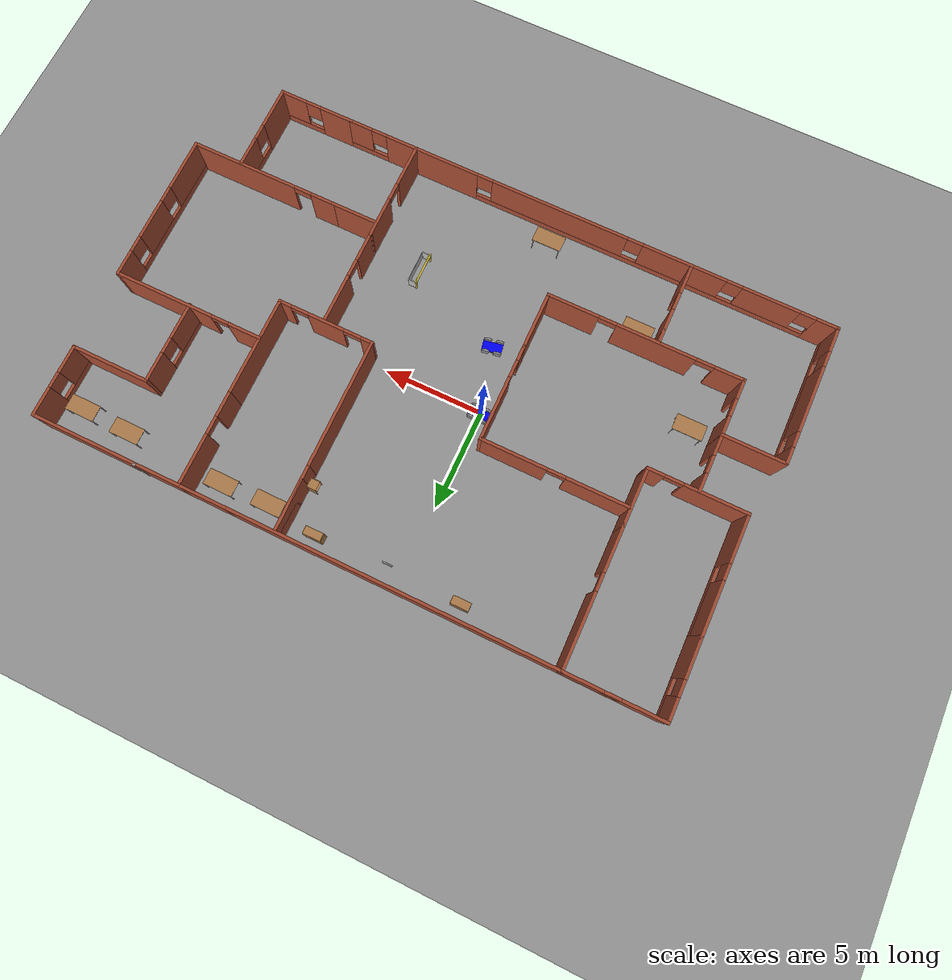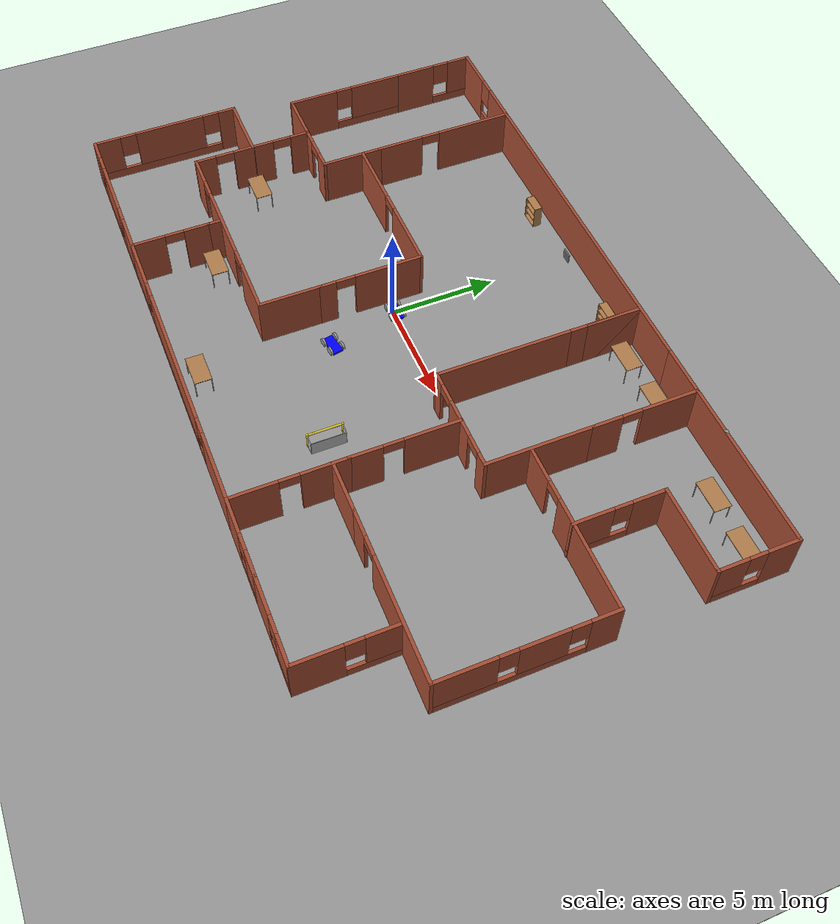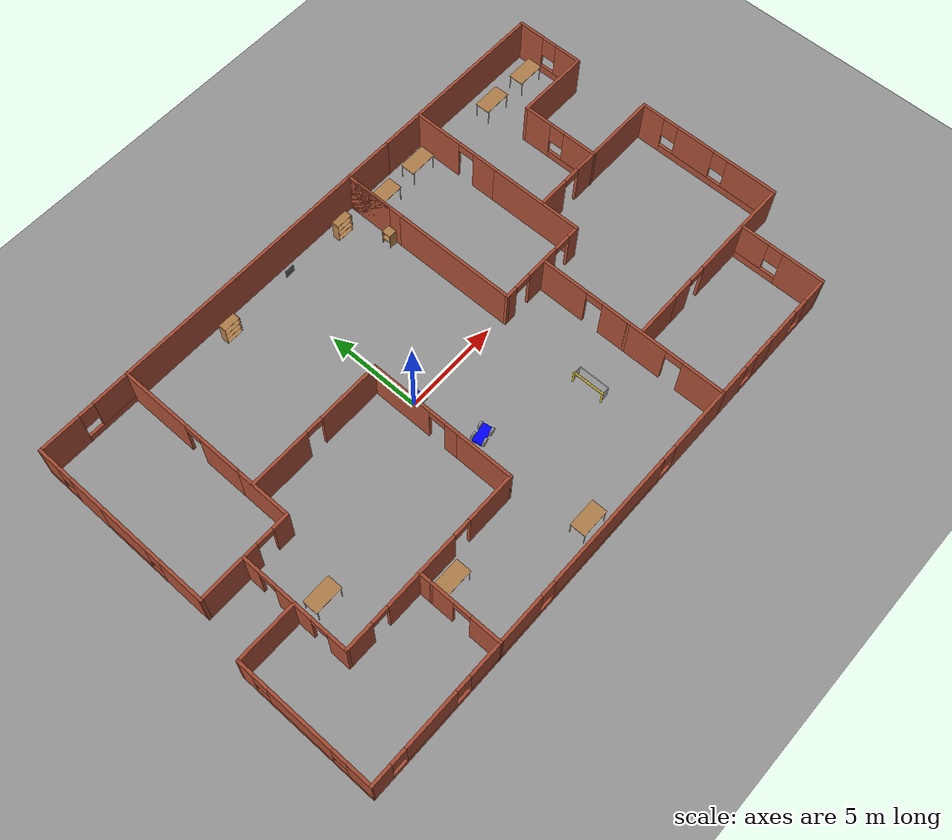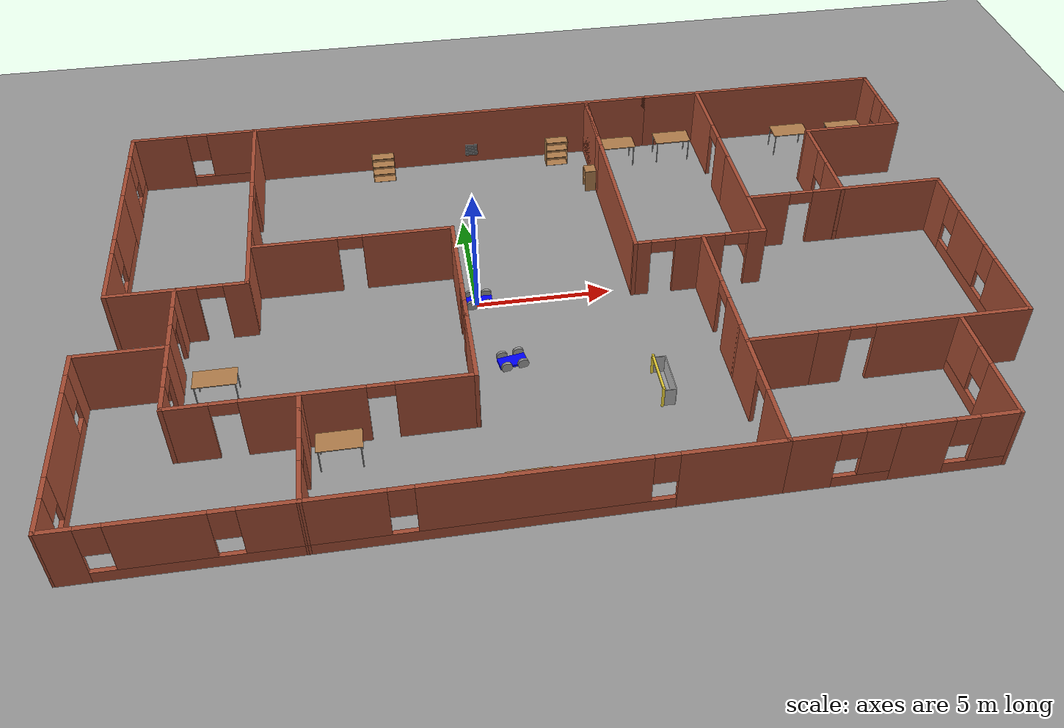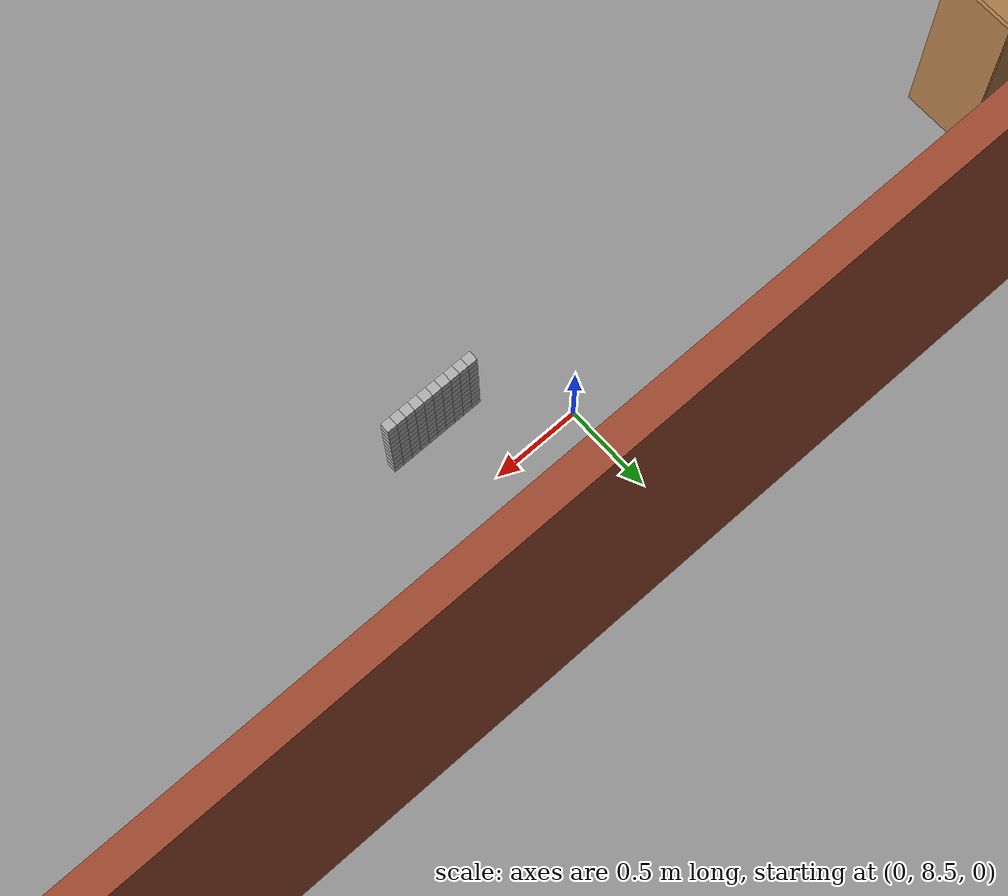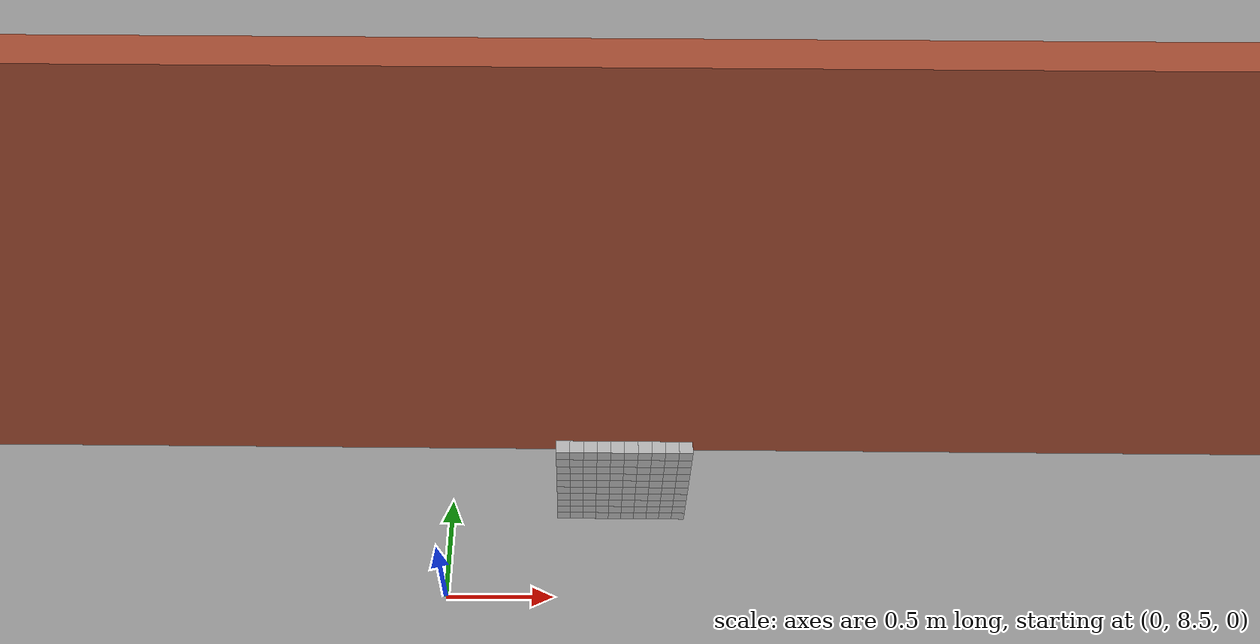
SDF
<sdf version="1.6">
 <world name="default">
  <plugin name="welcome" filename="libwelcome.so"/>
  <light name="sun" type="directional">
   <pose>0 0 10 0 -0 0</pose>
   <diffuse>0.8 0.8 0.8 1</diffuse>
   <specular>0.2 0.2 0.2 1</specular>
   <attenuation>
    <range>1000</range>
    <constant>0.9</constant>
    <linear>0.01</linear>
    <quadratic>0.001</quadratic>
   </attenuation>
   <direction>-0.5 0.1 -0.9</direction>
  </light>
  <model name="ground_plane">
   <static>1</static>
   <link name="link">
    <collision name="collision">
     <geometry><plane><normal>0 0 1</normal><size>100 100</size></plane></geometry>
     <surface>
      <contact><collide_bitmask>65535</collide_bitmask></contact>
      <friction><ode><mu>100</mu><mu2>50</mu2></ode></friction>
     </surface>
    </collision>
    <visual name="visual">
     <cast_shadows>0</cast_shadows>
     <geometry><plane><normal>0 0 1</normal><size>100 100</size></plane></geometry>
     <material>
      <script><uri>file://media/materials/scripts/gazebo.material</uri><name>Gazebo/Grey</name></script>
     </material>
    </visual>
   </link>
  </model>
  <gravity>0 0 -9.8</gravity>
  <magnetic_field>6e-06 2.3e-05 -4.2e-05</magnetic_field>
  <atmosphere type="adiabatic"/>
  <physics name="default_physics" default="0" type="ode">
   <max_step_size>0.001</max_step_size>
   <real_time_factor>1</real_time_factor>
   <real_time_update_rate>1000</real_time_update_rate>
  </physics>
  <scene><ambient>0.4 0.4 0.4 1</ambient><background>0.7 0.7 0.7 1</background><shadows>1</shadows></scene>
  <spherical_coordinates>
   <surface_model>EARTH_WGS84</surface_model>
   <latitude_deg>0</latitude_deg>
   <longitude_deg>0</longitude_deg>
   <elevation>0</elevation>
   <heading_deg>0</heading_deg>
  </spherical_coordinates>
  <model name="office">
   <pose>2.35048 -0.469027 0 0 -0 0</pose>
   <link name="Wall_0">
    <pose>-12.8016 9.8293 0 0 -0 1.2e-05</pose>
    <visual name="Wall_0_Visual_0">
     <pose>-1.40419 0 1.25 0 -0 0</pose>
     <geometry><box><size>2.19162 0.15 2.5</size></box></geometry>
     <material>
      <script><uri>file://media/materials/scripts/gazebo.material</uri><name>Gazebo/Bricks</name></script>
      <ambient>1 1 1 1</ambient>
     </material>
     <meta><layer>0</layer></meta>
    </visual>
    <collision name="Wall_0_Collision_0">
     <geometry><box><size>2.19162 0.15 2.5</size></box></geometry>
     <pose>-1.40419 0 1.25 0 -0 0</pose>
    </collision>
    <visual name="Wall_0_Visual_1">
     <pose>1.09581 0 0.25 0 -0 0</pose>
     <geometry><box><size>2.80838 0.15 0.5</size></box></geometry>
     <material>
      <script><uri>file://media/materials/scripts/gazebo.material</uri><name>Gazebo/Bricks</name></script>
      <ambient>1 1 1 1</ambient>
     </material>
     <meta><layer>0</layer></meta>
    </visual>
    <collision name="Wall_0_Collision_1">
     <geometry><box><size>2.80838 0.15 0.5</size></box></geometry>
     <pose>1.09581 0 0.25 0 -0 0</pose>
    </collision>
    <visual name="Wall_0_Visual_2">
     <pose>1.49581 0 1.5 0 -0 0</pose>
     <geometry><box><size>2.00839 0.15 2</size></box></geometry>
     <material>
      <script><uri>file://media/materials/scripts/gazebo.material</uri><name>Gazebo/Bricks</name></script>
      <ambient>1 1 1 1</ambient>
     </material>
     <meta><layer>0</layer></meta>
    </visual>
    <collision name="Wall_0_Collision_2">
     <geometry><box><size>2.00839 0.15 2</size></box></geometry>
     <pose>1.49581 0 1.5 0 -0 0</pose>
    </collision>
    <visual name="Wall_0_Visual_3">
     <pose>0.091615 0 1.9 0 -0 0</pose>
     <geometry><box><size>0.8 0.15 1.2</size></box></geometry>
     <material>
      <script><uri>file://media/materials/scripts/gazebo.material</uri><name>Gazebo/Bricks</name></script>
      <ambient>1 1 1 1</ambient>
     </material>
     <meta><layer>0</layer></meta>
    </visual>
    <collision name="Wall_0_Collision_3">
     <geometry><box><size>0.8 0.15 1.2</size></box></geometry>
     <pose>0.091615 0 1.9 0 -0 0</pose>
    </collision>
   </link>
   <link name="Wall_1">
    <pose>-10.3767 6.40433 0 0 0 -1.5708</pose>
    <visual name="Wall_1_Visual_0">
     <pose>-1.61827 0 1.25 0 -0 0</pose>
     <geometry><box><size>3.76346 0.15 2.5</size></box></geometry>
     <material>
      <script><uri>file://media/materials/scripts/gazebo.material</uri><name>Gazebo/Bricks</name></script>
      <ambient>0 0 1 1</ambient>
     </material>
     <meta><layer>0</layer></meta>
    </visual>
    <collision name="Wall_1_Collision_0">
     <geometry><box><size>3.76346 0.15 2.5</size></box></geometry>
     <pose>-1.61827 0 1.25 0 -0 0</pose>
    </collision>
    <visual name="Wall_1_Visual_1">
     <pose>2.33173 0 1.25 0 -0 0</pose>
     <geometry><box><size>2.33654 0.15 2.5</size></box></geometry>
     <material>
      <script><uri>file://media/materials/scripts/gazebo.material</uri><name>Gazebo/Bricks</name></script>
      <ambient>0 0 1 1</ambient>
     </material>
     <meta><layer>0</layer></meta>
    </visual>
    <collision name="Wall_1_Collision_1">
     <geometry><box><size>2.33654 0.15 2.5</size></box></geometry>
     <pose>2.33173 0 1.25 0 -0 0</pose>
    </collision>
    <visual name="Wall_1_Visual_2">
     <pose>0.713457 0 2.25 0 -0 0</pose>
     <geometry><box><size>0.9 0.15 0.5</size></box></geometry>
     <material>
      <script><uri>file://media/materials/scripts/gazebo.material</uri><name>Gazebo/Bricks</name></script>
      <ambient>0 0 1 1</ambient>
     </material>
     <meta><layer>0</layer></meta>
    </visual>
    <collision name="Wall_1_Collision_2">
     <geometry><box><size>0.9 0.15 0.5</size></box></geometry>
     <pose>0.713457 0 2.25 0 -0 0</pose>
    </collision>
   </link>
   <link name="Wall_10">
    <collision name="Wall_10_Collision">
     <geometry><box><size>3 0.15 2.5</size></box></geometry>
     <pose>0 0 1.25 0 -0 0</pose>
    </collision>
    <visual name="Wall_10_Visual">
     <pose>0 0 1.25 0 -0 0</pose>
     <geometry><box><size>3 0.15 2.5</size></box></geometry>
     <material>
      <script><uri>file://media/materials/scripts/gazebo.material</uri><name>Gazebo/Bricks</name></script>
      <ambient>0 0 1 1</ambient>
     </material>
     <meta><layer>0</layer></meta>
    </visual>
    <pose>-3.00328 -4.16052 0 0 -0 1.5708</pose>
   </link>
   <link name="Wall_11">
    <pose>-3.00328 -0.310524 0 0 -0 1.5708</pose>
    <visual name="Wall_11_Visual_0">
     <pose>-2.09105 0 1.25 0 -0 0</pose>
     <geometry><box><size>0.817909 0.15 2.5</size></box></geometry>
     <material>
      <script><uri>file://media/materials/scripts/gazebo.material</uri><name>Gazebo/Bricks</name></script>
      <ambient>0 0 1 1</ambient>
     </material>
     <meta><layer>0</layer></meta>
    </visual>
    <collision name="Wall_11_Collision_0">
     <geometry><box><size>0.817909 0.15 2.5</size></box></geometry>
     <pose>-2.09105 0 1.25 0 -0 0</pose>
    </collision>
    <visual name="Wall_11_Visual_1">
     <pose>0.858954 0 1.25 0 -0 0</pose>
     <geometry><box><size>3.28209 0.15 2.5</size></box></geometry>
     <material>
      <script><uri>file://media/materials/scripts/gazebo.material</uri><name>Gazebo/Bricks</name></script>
      <ambient>0 0 1 1</ambient>
     </material>
     <meta><layer>0</layer></meta>
    </visual>
    <collision name="Wall_11_Collision_1">
     <geometry><box><size>3.28209 0.15 2.5</size></box></geometry>
     <pose>0.858954 0 1.25 0 -0 0</pose>
    </collision>
    <visual name="Wall_11_Visual_2">
     <pose>-1.23209 0 2.25 0 -0 0</pose>
     <geometry><box><size>0.9 0.15 0.5</size></box></geometry>
     <material>
      <script><uri>file://media/materials/scripts/gazebo.material</uri><name>Gazebo/Bricks</name></script>
      <ambient>0 0 1 1</ambient>
     </material>
     <meta><layer>0</layer></meta>
    </visual>
    <collision name="Wall_11_Collision_2">
     <geometry><box><size>0.9 0.15 0.5</size></box></geometry>
     <pose>-1.23209 0 2.25 0 -0 0</pose>
    </collision>
   </link>
   <link name="Wall_12">
    <pose>-6.67828 2.11448 0 0 -0 3.14159</pose>
    <visual name="Wall_12_Visual_0">
     <pose>-2.05802 0 1.25 0 -0 0</pose>
     <geometry><box><size>3.38397 0.15 2.5</size></box></geometry>
     <material>
      <script><uri>file://media/materials/scripts/gazebo.material</uri><name>Gazebo/Bricks</name></script>
      <ambient>0 0 1 1</ambient>
     </material>
     <meta><layer>0</layer></meta>
    </visual>
    <collision name="Wall_12_Collision_0">
     <geometry><box><size>3.38397 0.15 2.5</size></box></geometry>
     <pose>-2.05802 0 1.25 0 -0 0</pose>
    </collision>
    <visual name="Wall_12_Visual_1">
     <pose>2.14199 0 1.25 0 -0 0</pose>
     <geometry><box><size>3.21603 0.15 2.5</size></box></geometry>
     <material>
      <script><uri>file://media/materials/scripts/gazebo.material</uri><name>Gazebo/Bricks</name></script>
      <ambient>0 0 1 1</ambient>
     </material>
     <meta><layer>0</layer></meta>
    </visual>
    <collision name="Wall_12_Collision_1">
     <geometry><box><size>3.21603 0.15 2.5</size></box></geometry>
     <pose>2.14199 0 1.25 0 -0 0</pose>
    </collision>
    <visual name="Wall_12_Visual_2">
     <pose>0.083969 0 2.25 0 -0 0</pose>
     <geometry><box><size>0.9 0.15 0.5</size></box></geometry>
     <material>
      <script><uri>file://media/materials/scripts/gazebo.material</uri><name>Gazebo/Bricks</name></script>
      <ambient>0 0 1 1</ambient>
     </material>
     <meta><layer>0</layer></meta>
    </visual>
    <collision name="Wall_12_Collision_2">
     <geometry><box><size>0.9 0.15 0.5</size></box></geometry>
     <pose>0.083969 0 2.25 0 -0 0</pose>
    </collision>
   </link>
   <link name="Wall_14">
    <collision name="Wall_14_Collision">
     <geometry><box><size>16.5 0.15 2.5</size></box></geometry>
     <pose>0 0 1.25 0 -0 0</pose>
    </collision>
    <visual name="Wall_14_Visual">
     <pose>0 0 1.25 0 -0 0</pose>
     <geometry><box><size>16.5 0.15 2.5</size></box></geometry>
     <material>
      <script><uri>file://media/materials/scripts/gazebo.material</uri><name>Gazebo/Bricks</name></script>
      <ambient>1 1 1 1</ambient>
     </material>
     <meta><layer>0</layer></meta>
    </visual>
    <pose>-2.20168 9.82933 0 0 -0 0</pose>
   </link>
   <link name="Wall_15">
    <collision name="Wall_15_Collision">
     <geometry><box><size>2.5 0.15 2.5</size></box></geometry>
     <pose>0 0 1.25 0 -0 0</pose>
    </collision>
    <visual name="Wall_15_Visual">
     <pose>0 0 1.25 0 -0 0</pose>
     <geometry><box><size>2.5 0.15 2.5</size></box></geometry>
     <material>
      <script><uri>file://media/materials/scripts/gazebo.material</uri><name>Gazebo/Bricks</name></script>
      <ambient>1 1 1 1</ambient>
     </material>
     <meta><layer>0</layer></meta>
    </visual>
    <pose>7.14832 9.82933 0 0 -0 0</pose>
   </link>
   <link name="Wall_150">
    <collision name="Wall_150_Collision">
     <geometry><box><size>7.75 0.15 2.5</size></box></geometry>
     <pose>0 0 1.25 0 -0 0</pose>
    </collision>
    <visual name="Wall_150_Visual">
     <pose>0 0 1.25 0 -0 0</pose>
     <geometry><box><size>7.75 0.15 2.5</size></box></geometry>
     <material>
      <script><uri>file://media/materials/scripts/gazebo.material</uri><name>Gazebo/Bricks</name></script>
      <ambient>1 1 1 1</ambient>
     </material>
     <meta><layer>0</layer></meta>
    </visual>
    <pose>12.1233 9.82933 0 0 -0 0</pose>
   </link>
   <link name="Wall_151">
    <pose>15.9233 8.02933 0 0 0 -1.5708</pose>
    <visual name="Wall_151_Visual_0">
     <pose>-1.12763 0 1.25 0 -0 0</pose>
     <geometry><box><size>1.49474 0.15 2.5</size></box></geometry>
     <material>
      <script><uri>file://media/materials/scripts/gazebo.material</uri><name>Gazebo/Bricks</name></script>
      <ambient>1 1 1 1</ambient>
     </material>
     <meta><layer>0</layer></meta>
    </visual>
    <collision name="Wall_151_Collision_0">
     <geometry><box><size>1.49474 0.15 2.5</size></box></geometry>
     <pose>-1.12763 0 1.25 0 -0 0</pose>
    </collision>
    <visual name="Wall_151_Visual_1">
     <pose>0.747372 0 0.25 0 -0 0</pose>
     <geometry><box><size>2.25526 0.15 0.5</size></box></geometry>
     <material>
      <script><uri>file://media/materials/scripts/gazebo.material</uri><name>Gazebo/Bricks</name></script>
      <ambient>1 1 1 1</ambient>
     </material>
     <meta><layer>0</layer></meta>
    </visual>
    <collision name="Wall_151_Collision_1">
     <geometry><box><size>2.25526 0.15 0.5</size></box></geometry>
     <pose>0.747372 0 0.25 0 -0 0</pose>
    </collision>
    <visual name="Wall_151_Visual_2">
     <pose>1.14737 0 1.5 0 -0 0</pose>
     <geometry><box><size>1.45526 0.15 2</size></box></geometry>
     <material>
      <script><uri>file://media/materials/scripts/gazebo.material</uri><name>Gazebo/Bricks</name></script>
      <ambient>1 1 1 1</ambient>
     </material>
     <meta><layer>0</layer></meta>
    </visual>
    <collision name="Wall_151_Collision_2">
     <geometry><box><size>1.45526 0.15 2</size></box></geometry>
     <pose>1.14737 0 1.5 0 -0 0</pose>
    </collision>
    <visual name="Wall_151_Visual_3">
     <pose>0.019743 0 1.9 0 -0 0</pose>
     <geometry><box><size>0.8 0.15 1.2</size></box></geometry>
     <material>
      <script><uri>file://media/materials/scripts/gazebo.material</uri><name>Gazebo/Bricks</name></script>
      <ambient>1 1 1 1</ambient>
     </material>
     <meta><layer>0</layer></meta>
    </visual>
    <collision name="Wall_151_Collision_3">
     <geometry><box><size>0.8 0.15 1.2</size></box></geometry>
     <pose>0.019743 0 1.9 0 -0 0</pose>
    </collision>
   </link>
   <link name="Wall_152">
    <collision name="Wall_152_Collision">
     <geometry><box><size>4 0.15 2.5</size></box></geometry>
     <pose>0 0 1.25 0 -0 0</pose>
    </collision>
    <visual name="Wall_152_Visual">
     <pose>0 0 1.25 0 -0 0</pose>
     <geometry><box><size>4 0.15 2.5</size></box></geometry>
     <material>
      <script><uri>file://media/materials/scripts/gazebo.material</uri><name>Gazebo/Bricks</name></script>
      <ambient>1 1 1 1</ambient>
     </material>
     <meta><layer>0</layer></meta>
    </visual>
    <pose>13.9983 6.22933 0 0 -0 3.14159</pose>
   </link>
   <link name="Wall_156">
    <pose>12.0733 4.17933 0 0 0 -1.5708</pose>
    <visual name="Wall_156_Visual_0">
     <pose>-1.33794 0 1.25 0 -0 0</pose>
     <geometry><box><size>1.57411 0.15 2.5</size></box></geometry>
     <material>
      <script><uri>file://media/materials/scripts/gazebo.material</uri><name>Gazebo/Bricks</name></script>
      <ambient>1 1 1 1</ambient>
     </material>
     <meta><layer>0</layer></meta>
    </visual>
    <collision name="Wall_156_Collision_0">
     <geometry><box><size>1.57411 0.15 2.5</size></box></geometry>
     <pose>-1.33794 0 1.25 0 -0 0</pose>
    </collision>
    <visual name="Wall_156_Visual_1">
     <pose>0.787055 0 0.25 0 -0 0</pose>
     <geometry><box><size>2.67589 0.15 0.5</size></box></geometry>
     <material>
      <script><uri>file://media/materials/scripts/gazebo.material</uri><name>Gazebo/Bricks</name></script>
      <ambient>1 1 1 1</ambient>
     </material>
     <meta><layer>0</layer></meta>
    </visual>
    <collision name="Wall_156_Collision_1">
     <geometry><box><size>2.67589 0.15 0.5</size></box></geometry>
     <pose>0.787055 0 0.25 0 -0 0</pose>
    </collision>
    <visual name="Wall_156_Visual_2">
     <pose>1.18705 0 1.5 0 -0 0</pose>
     <geometry><box><size>1.87589 0.15 2</size></box></geometry>
     <material>
      <script><uri>file://media/materials/scripts/gazebo.material</uri><name>Gazebo/Bricks</name></script>
      <ambient>1 1 1 1</ambient>
     </material>
     <meta><layer>0</layer></meta>
    </visual>
    <collision name="Wall_156_Collision_2">
     <geometry><box><size>1.87589 0.15 2</size></box></geometry>
     <pose>1.18705 0 1.5 0 -0 0</pose>
    </collision>
    <visual name="Wall_156_Visual_3">
     <pose>-0.150889 0 1.9 0 -0 0</pose>
     <geometry><box><size>0.8 0.15 1.2</size></box></geometry>
     <material>
      <script><uri>file://media/materials/scripts/gazebo.material</uri><name>Gazebo/Bricks</name></script>
      <ambient>1 1 1 1</ambient>
     </material>
     <meta><layer>0</layer></meta>
    </visual>
    <collision name="Wall_156_Collision_3">
     <geometry><box><size>0.8 0.15 1.2</size></box></geometry>
     <pose>-0.150889 0 1.9 0 -0 0</pose>
    </collision>
   </link>
   <link name="Wall_16">
    <pose>8.32342 7.4043 0 0 0 -1.57075</pose>
    <visual name="Wall_16_Visual_0">
     <pose>-1.16357 0 1.25 0 -0 0</pose>
     <geometry><box><size>2.67286 0.15 2.5</size></box></geometry>
     <material>
      <script><uri>file://media/materials/scripts/gazebo.material</uri><name>Gazebo/Bricks</name></script>
      <ambient>0 0 1 1</ambient>
     </material>
     <meta><layer>0</layer></meta>
    </visual>
    <collision name="Wall_16_Collision_0">
     <geometry><box><size>2.67286 0.15 2.5</size></box></geometry>
     <pose>-1.16357 0 1.25 0 -0 0</pose>
    </collision>
    <visual name="Wall_16_Visual_1">
     <pose>1.78643 0 1.25 0 -0 0</pose>
     <geometry><box><size>1.42714 0.15 2.5</size></box></geometry>
     <material>
      <script><uri>file://media/materials/scripts/gazebo.material</uri><name>Gazebo/Bricks</name></script>
      <ambient>0 0 1 1</ambient>
     </material>
     <meta><layer>0</layer></meta>
    </visual>
    <collision name="Wall_16_Collision_1">
     <geometry><box><size>1.42714 0.15 2.5</size></box></geometry>
     <pose>1.78643 0 1.25 0 -0 0</pose>
    </collision>
    <visual name="Wall_16_Visual_2">
     <pose>0.622857 0 2.25 0 -0 0</pose>
     <geometry><box><size>0.9 0.15 0.5</size></box></geometry>
     <material>
      <script><uri>file://media/materials/scripts/gazebo.material</uri><name>Gazebo/Bricks</name></script>
      <ambient>0 0 1 1</ambient>
     </material>
     <meta><layer>0</layer></meta>
    </visual>
    <collision name="Wall_16_Collision_2">
     <geometry><box><size>0.9 0.15 0.5</size></box></geometry>
     <pose>0.622857 0 2.25 0 -0 0</pose>
    </collision>
   </link>
   <link name="Wall_17">
    <collision name="Wall_17_Collision">
     <geometry><box><size>5 0.15 2.5</size></box></geometry>
     <pose>0 0 1.25 0 -0 0</pose>
    </collision>
    <visual name="Wall_17_Visual">
     <pose>0 0 1.25 0 -0 0</pose>
     <geometry><box><size>5 0.15 2.5</size></box></geometry>
     <material>
      <script><uri>file://media/materials/scripts/gazebo.material</uri><name>Gazebo/Bricks</name></script>
      <ambient>0 0 1 1</ambient>
     </material>
     <meta><layer>0</layer></meta>
    </visual>
    <pose>8.32352 2.55427 0 0 0 -1.5708</pose>
   </link>
   <link name="Wall_18">
    <pose>5.89852 0.129271 0 0 -0 3.14159</pose>
    <visual name="Wall_18_Visual_0">
     <pose>-2.16272 0 1.25 0 -0 0</pose>
     <geometry><box><size>0.674563 0.15 2.5</size></box></geometry>
     <material>
      <script><uri>file://media/materials/scripts/gazebo.material</uri><name>Gazebo/Bricks</name></script>
      <ambient>0 0 1 1</ambient>
     </material>
     <meta><layer>0</layer></meta>
    </visual>
    <collision name="Wall_18_Collision_0">
     <geometry><box><size>0.674563 0.15 2.5</size></box></geometry>
     <pose>-2.16272 0 1.25 0 -0 0</pose>
    </collision>
    <visual name="Wall_18_Visual_1">
     <pose>0.007773 0 1.25 0 -0 0</pose>
     <geometry><box><size>1.86642 0.15 2.5</size></box></geometry>
     <material>
      <script><uri>file://media/materials/scripts/gazebo.material</uri><name>Gazebo/Bricks</name></script>
      <ambient>0 0 1 1</ambient>
     </material>
     <meta><layer>0</layer></meta>
    </visual>
    <collision name="Wall_18_Collision_1">
     <geometry><box><size>1.86642 0.15 2.5</size></box></geometry>
     <pose>0.007773 0 1.25 0 -0 0</pose>
    </collision>
    <visual name="Wall_18_Visual_2">
     <pose>2.17049 0 1.25 0 -0 0</pose>
     <geometry><box><size>0.659016 0.15 2.5</size></box></geometry>
     <material>
      <script><uri>file://media/materials/scripts/gazebo.material</uri><name>Gazebo/Bricks</name></script>
      <ambient>0 0 1 1</ambient>
     </material>
     <meta><layer>0</layer></meta>
    </visual>
    <collision name="Wall_18_Collision_2">
     <geometry><box><size>0.659016 0.15 2.5</size></box></geometry>
     <pose>2.17049 0 1.25 0 -0 0</pose>
    </collision>
    <visual name="Wall_18_Visual_3">
     <pose>-1.37544 0 2.25 0 -0 0</pose>
     <geometry><box><size>0.9 0.15 0.5</size></box></geometry>
     <material>
      <script><uri>file://media/materials/scripts/gazebo.material</uri><name>Gazebo/Bricks</name></script>
      <ambient>0 0 1 1</ambient>
     </material>
     <meta><layer>0</layer></meta>
    </visual>
    <collision name="Wall_18_Collision_3">
     <geometry><box><size>0.9 0.15 0.5</size></box></geometry>
     <pose>-1.37544 0 2.25 0 -0 0</pose>
    </collision>
    <visual name="Wall_18_Visual_4">
     <pose>1.39098 0 2.25 0 -0 0</pose>
     <geometry><box><size>0.9 0.15 0.5</size></box></geometry>
     <material>
      <script><uri>file://media/materials/scripts/gazebo.material</uri><name>Gazebo/Bricks</name></script>
      <ambient>0 0 1 1</ambient>
     </material>
     <meta><layer>0</layer></meta>
    </visual>
    <collision name="Wall_18_Collision_4">
     <geometry><box><size>0.9 0.15 0.5</size></box></geometry>
     <pose>1.39098 0 2.25 0 -0 0</pose>
    </collision>
   </link>
   <link name="Wall_19">
    <collision name="Wall_19_Collision">
     <geometry><box><size>6.5 0.15 2.5</size></box></geometry>
     <pose>0 0 1.25 0 -0 0</pose>
    </collision>
    <visual name="Wall_19_Visual">
     <pose>0 0 1.25 0 -0 0</pose>
     <geometry><box><size>6.5 0.15 2.5</size></box></geometry>
     <material>
      <script><uri>file://media/materials/scripts/gazebo.material</uri><name>Gazebo/Bricks</name></script>
      <ambient>0 0 1 1</ambient>
     </material>
     <meta><layer>0</layer></meta>
    </visual>
    <pose>3.47352 3.30427 0 0 -0 1.5708</pose>
   </link>
   <link name="Wall_2">
    <collision name="Wall_2_Collision">
     <geometry><box><size>3 0.15 2.5</size></box></geometry>
     <pose>0 0 1.25 0 -0 0</pose>
    </collision>
    <visual name="Wall_2_Visual">
     <pose>0 0 1.25 0 -0 0</pose>
     <geometry><box><size>3 0.15 2.5</size></box></geometry>
     <material>
      <script><uri>file://media/materials/scripts/gazebo.material</uri><name>Gazebo/Bricks</name></script>
      <ambient>0 0 1 1</ambient>
     </material>
     <meta><layer>0</layer></meta>
    </visual>
    <pose>-10.3766 1.5543 0 0 0 -1.57073</pose>
   </link>
   <link name="Wall_20">
    <pose>3.47342 8.1543 0 0 -0 1.57086</pose>
    <visual name="Wall_20_Visual_0">
     <pose>0 0 1.25 0 -0 0</pose>
     <geometry><box><size>3.5 0.15 2.5</size></box></geometry>
     <material>
      <script><uri>file://media/materials/scripts/gazebo.material</uri><name>Gazebo/Bricks</name></script>
      <ambient>0 0 1 1</ambient>
     </material>
     <meta><layer>0</layer></meta>
    </visual>
    <collision name="Wall_20_Collision_0">
     <geometry><box><size>3.5 0.15 2.5</size></box></geometry>
     <pose>0 0 1.25 0 -0 0</pose>
    </collision>
    <visual name="Wall_20_Visual_1">
     <pose>0.400263 0 1.25 0 -0 0</pose>
     <geometry><box><size>2.69948 0.15 2.5</size></box></geometry>
     <material>
      <script><uri>file://media/materials/scripts/gazebo.material</uri><name>Gazebo/Bricks</name></script>
      <ambient>0 0 1 1</ambient>
     </material>
     <meta><layer>0</layer></meta>
    </visual>
    <collision name="Wall_20_Collision_1">
     <geometry><box><size>2.69948 0.15 2.5</size></box></geometry>
     <pose>0.400263 0 1.25 0 -0 0</pose>
    </collision>
   </link>
   <link name="Wall_22">
    <pose>5.99314 -2.33064 0 0 0 -1.5708</pose>
    <visual name="Wall_22_Visual_0">
     <pose>-1.21642 0 1.25 0 -0 0</pose>
     <geometry><box><size>2.56715 0.15 2.5</size></box></geometry>
     <material>
      <script><uri>file://media/materials/scripts/gazebo.material</uri><name>Gazebo/Bricks</name></script>
      <ambient>1 1 1 1</ambient>
     </material>
     <meta><layer>0</layer></meta>
    </visual>
    <collision name="Wall_22_Collision_0">
     <geometry><box><size>2.56715 0.15 2.5</size></box></geometry>
     <pose>-1.21642 0 1.25 0 -0 0</pose>
    </collision>
    <visual name="Wall_22_Visual_1">
     <pose>1.73358 0 1.25 0 -0 0</pose>
     <geometry><box><size>1.53285 0.15 2.5</size></box></geometry>
     <material>
      <script><uri>file://media/materials/scripts/gazebo.material</uri><name>Gazebo/Bricks</name></script>
      <ambient>1 1 1 1</ambient>
     </material>
     <meta><layer>0</layer></meta>
    </visual>
    <collision name="Wall_22_Collision_1">
     <geometry><box><size>1.53285 0.15 2.5</size></box></geometry>
     <pose>1.73358 0 1.25 0 -0 0</pose>
    </collision>
    <visual name="Wall_22_Visual_2">
     <pose>0.517152 0 2.25 0 -0 0</pose>
     <geometry><box><size>0.9 0.15 0.5</size></box></geometry>
     <material>
      <script><uri>file://media/materials/scripts/gazebo.material</uri><name>Gazebo/Bricks</name></script>
      <ambient>1 1 1 1</ambient>
     </material>
     <meta><layer>0</layer></meta>
    </visual>
    <collision name="Wall_22_Collision_2">
     <geometry><box><size>0.9 0.15 0.5</size></box></geometry>
     <pose>0.517152 0 2.25 0 -0 0</pose>
    </collision>
   </link>
   <link name="Wall_23">
    <pose>5.99333 -7.30568 0 0 0 -1.57072</pose>
    <visual name="Wall_23_Visual_0">
     <pose>-1.55338 0 1.25 0 -0 0</pose>
     <geometry><box><size>2.14324 0.15 2.5</size></box></geometry>
     <material>
      <script><uri>file://media/materials/scripts/gazebo.material</uri><name>Gazebo/Bricks</name></script>
      <ambient>1 1 1 1</ambient>
     </material>
     <meta><layer>0</layer></meta>
    </visual>
    <collision name="Wall_23_Collision_0">
     <geometry><box><size>2.14324 0.15 2.5</size></box></geometry>
     <pose>-1.55338 0 1.25 0 -0 0</pose>
    </collision>
    <visual name="Wall_23_Visual_1">
     <pose>1.52162 0 1.25 0 -0 0</pose>
     <geometry><box><size>2.20676 0.15 2.5</size></box></geometry>
     <material>
      <script><uri>file://media/materials/scripts/gazebo.material</uri><name>Gazebo/Bricks</name></script>
      <ambient>1 1 1 1</ambient>
     </material>
     <meta><layer>0</layer></meta>
    </visual>
    <collision name="Wall_23_Collision_1">
     <geometry><box><size>2.20676 0.15 2.5</size></box></geometry>
     <pose>1.52162 0 1.25 0 -0 0</pose>
    </collision>
    <visual name="Wall_23_Visual_2">
     <pose>-0.031758 0 2.25 0 -0 0</pose>
     <geometry><box><size>0.9 0.15 0.5</size></box></geometry>
     <material>
      <script><uri>file://media/materials/scripts/gazebo.material</uri><name>Gazebo/Bricks</name></script>
      <ambient>1 1 1 1</ambient>
     </material>
     <meta><layer>0</layer></meta>
    </visual>
    <collision name="Wall_23_Collision_2">
     <geometry><box><size>0.9 0.15 0.5</size></box></geometry>
     <pose>-0.031758 0 2.25 0 -0 0</pose>
    </collision>
   </link>
   <link name="Wall_24">
    <pose>-1.30648 -9.85573 0 0 -0 3.14159</pose>
    <visual name="Wall_24_Visual_0">
     <pose>-5.65269 0 1.25 0 -0 0</pose>
     <geometry><box><size>3.44462 0.15 2.5</size></box></geometry>
     <material>
      <script><uri>file://media/materials/scripts/gazebo.material</uri><name>Gazebo/Bricks</name></script>
      <ambient>1 1 1 1</ambient>
     </material>
     <meta><layer>0</layer></meta>
    </visual>
    <collision name="Wall_24_Collision_0">
     <geometry><box><size>3.44462 0.15 2.5</size></box></geometry>
     <pose>-5.65269 0 1.25 0 -0 0</pose>
    </collision>
    <visual name="Wall_24_Visual_1">
     <pose>1.72231 0 0.25 0 -0 0</pose>
     <geometry><box><size>11.3054 0.15 0.5</size></box></geometry>
     <material>
      <script><uri>file://media/materials/scripts/gazebo.material</uri><name>Gazebo/Bricks</name></script>
      <ambient>1 1 1 1</ambient>
     </material>
     <meta><layer>0</layer></meta>
    </visual>
    <collision name="Wall_24_Collision_1">
     <geometry><box><size>11.3054 0.15 0.5</size></box></geometry>
     <pose>1.72231 0 0.25 0 -0 0</pose>
    </collision>
    <visual name="Wall_24_Visual_2">
     <pose>0.432018 0 1.5 0 -0 0</pose>
     <geometry><box><size>7.12479 0.15 2</size></box></geometry>
     <material>
      <script><uri>file://media/materials/scripts/gazebo.material</uri><name>Gazebo/Bricks</name></script>
      <ambient>1 1 1 1</ambient>
     </material>
     <meta><layer>0</layer></meta>
    </visual>
    <collision name="Wall_24_Collision_2">
     <geometry><box><size>7.12479 0.15 2</size></box></geometry>
     <pose>0.432018 0 1.5 0 -0 0</pose>
    </collision>
    <visual name="Wall_24_Visual_3">
     <pose>6.08471 0 1.5 0 -0 0</pose>
     <geometry><box><size>2.58059 0.15 2</size></box></geometry>
     <material>
      <script><uri>file://media/materials/scripts/gazebo.material</uri><name>Gazebo/Bricks</name></script>
      <ambient>1 1 1 1</ambient>
     </material>
     <meta><layer>0</layer></meta>
    </visual>
    <collision name="Wall_24_Collision_3">
     <geometry><box><size>2.58059 0.15 2</size></box></geometry>
     <pose>6.08471 0 1.5 0 -0 0</pose>
    </collision>
    <visual name="Wall_24_Visual_4">
     <pose>-3.53038 0 1.9 0 -0 0</pose>
     <geometry><box><size>0.8 0.15 1.2</size></box></geometry>
     <material>
      <script><uri>file://media/materials/scripts/gazebo.material</uri><name>Gazebo/Bricks</name></script>
      <ambient>1 1 1 1</ambient>
     </material>
     <meta><layer>0</layer></meta>
    </visual>
    <collision name="Wall_24_Collision_4">
     <geometry><box><size>0.8 0.15 1.2</size></box></geometry>
     <pose>-3.53038 0 1.9 0 -0 0</pose>
    </collision>
    <visual name="Wall_24_Visual_5">
     <pose>4.39441 0 1.9 0 -0 0</pose>
     <geometry><box><size>0.8 0.15 1.2</size></box></geometry>
     <material>
      <script><uri>file://media/materials/scripts/gazebo.material</uri><name>Gazebo/Bricks</name></script>
      <ambient>1 1 1 1</ambient>
     </material>
     <meta><layer>0</layer></meta>
    </visual>
    <collision name="Wall_24_Collision_5">
     <geometry><box><size>0.8 0.15 1.2</size></box></geometry>
     <pose>4.39441 0 1.9 0 -0 0</pose>
    </collision>
   </link>
   <link name="Wall_25">
    <pose>-8.60667 -8.05568 0 0 -0 1.5709</pose>
    <visual name="Wall_25_Visual_0">
     <pose>-1.07228 0 1.25 0 -0 0</pose>
     <geometry><box><size>1.60545 0.15 2.5</size></box></geometry>
     <material>
      <script><uri>file://media/materials/scripts/gazebo.material</uri><name>Gazebo/Bricks</name></script>
      <ambient>1 1 1 1</ambient>
     </material>
     <meta><layer>0</layer></meta>
    </visual>
    <collision name="Wall_25_Collision_0">
     <geometry><box><size>1.60545 0.15 2.5</size></box></geometry>
     <pose>-1.07228 0 1.25 0 -0 0</pose>
    </collision>
    <visual name="Wall_25_Visual_1">
     <pose>1.25273 0 1.25 0 -0 0</pose>
     <geometry><box><size>1.24455 0.15 2.5</size></box></geometry>
     <material>
      <script><uri>file://media/materials/scripts/gazebo.material</uri><name>Gazebo/Bricks</name></script>
      <ambient>1 1 1 1</ambient>
     </material>
     <meta><layer>0</layer></meta>
    </visual>
    <collision name="Wall_25_Collision_1">
     <geometry><box><size>1.24455 0.15 2.5</size></box></geometry>
     <pose>1.25273 0 1.25 0 -0 0</pose>
    </collision>
    <visual name="Wall_25_Visual_2">
     <pose>0.18045 0 2.25 0 -0 0</pose>
     <geometry><box><size>0.9 0.15 0.5</size></box></geometry>
     <material>
      <script><uri>file://media/materials/scripts/gazebo.material</uri><name>Gazebo/Bricks</name></script>
      <ambient>1 1 1 1</ambient>
     </material>
     <meta><layer>0</layer></meta>
    </visual>
    <collision name="Wall_25_Collision_2">
     <geometry><box><size>0.9 0.15 0.5</size></box></geometry>
     <pose>0.18045 0 2.25 0 -0 0</pose>
    </collision>
   </link>
   <link name="Wall_26">
    <collision name="Wall_26_Collision">
     <geometry><box><size>0.75 0.15 2.5</size></box></geometry>
     <pose>0 0 1.25 0 -0 0</pose>
    </collision>
    <visual name="Wall_26_Visual">
     <pose>0 0 1.25 0 -0 0</pose>
     <geometry><box><size>0.75 0.15 2.5</size></box></geometry>
     <material>
      <script><uri>file://media/materials/scripts/gazebo.material</uri><name>Gazebo/Bricks</name></script>
      <ambient>1 1 1 1</ambient>
     </material>
     <meta><layer>0</layer></meta>
    </visual>
    <pose>-8.60686 -5.95564 0 0 -0 1.5708</pose>
   </link>
   <link name="Wall_28">
    <collision name="Wall_28_Collision">
     <geometry><box><size>3.25 0.15 2.5</size></box></geometry>
     <pose>0 0 1.25 0 -0 0</pose>
    </collision>
    <visual name="Wall_28_Visual">
     <pose>0 0 1.25 0 -0 0</pose>
     <geometry><box><size>3.25 0.15 2.5</size></box></geometry>
     <material>
      <script><uri>file://media/materials/scripts/gazebo.material</uri><name>Gazebo/Bricks</name></script>
      <ambient>1 1 1 1</ambient>
     </material>
     <meta><layer>0</layer></meta>
    </visual>
    <pose>-14.4035 -2.73573 0 0 -0 3.14159</pose>
   </link>
   <link name="Wall_29">
    <pose>-15.9535 -6.28573 0 0 0 -1.5708</pose>
    <visual name="Wall_29_Visual_0">
     <pose>-3.17286 0 1.25 0 -0 0</pose>
     <geometry><box><size>0.904269 0.15 2.5</size></box></geometry>
     <material>
      <script><uri>file://media/materials/scripts/gazebo.material</uri><name>Gazebo/Bricks</name></script>
      <ambient>1 1 1 1</ambient>
     </material>
     <meta><layer>0</layer></meta>
    </visual>
    <collision name="Wall_29_Collision_0">
     <geometry><box><size>0.904269 0.15 2.5</size></box></geometry>
     <pose>-3.17286 0 1.25 0 -0 0</pose>
    </collision>
    <visual name="Wall_29_Visual_1">
     <pose>0.452135 0 0.25 0 -0 0</pose>
     <geometry><box><size>6.34573 0.15 0.5</size></box></geometry>
     <material>
      <script><uri>file://media/materials/scripts/gazebo.material</uri><name>Gazebo/Bricks</name></script>
      <ambient>1 1 1 1</ambient>
     </material>
     <meta><layer>0</layer></meta>
    </visual>
    <collision name="Wall_29_Collision_1">
     <geometry><box><size>6.34573 0.15 0.5</size></box></geometry>
     <pose>0.452135 0 0.25 0 -0 0</pose>
    </collision>
    <visual name="Wall_29_Visual_2">
     <pose>-0.206015 0 1.5 0 -0 0</pose>
     <geometry><box><size>3.42943 0.15 2</size></box></geometry>
     <material>
      <script><uri>file://media/materials/scripts/gazebo.material</uri><name>Gazebo/Bricks</name></script>
      <ambient>1 1 1 1</ambient>
     </material>
     <meta><layer>0</layer></meta>
    </visual>
    <collision name="Wall_29_Collision_2">
     <geometry><box><size>3.42943 0.15 2</size></box></geometry>
     <pose>-0.206015 0 1.5 0 -0 0</pose>
    </collision>
    <visual name="Wall_29_Visual_3">
     <pose>2.96685 0 1.5 0 -0 0</pose>
     <geometry><box><size>1.3163 0.15 2</size></box></geometry>
     <material>
      <script><uri>file://media/materials/scripts/gazebo.material</uri><name>Gazebo/Bricks</name></script>
      <ambient>1 1 1 1</ambient>
     </material>
     <meta><layer>0</layer></meta>
    </visual>
    <collision name="Wall_29_Collision_3">
     <geometry><box><size>1.3163 0.15 2</size></box></geometry>
     <pose>2.96685 0 1.5 0 -0 0</pose>
    </collision>
    <visual name="Wall_29_Visual_4">
     <pose>-2.32073 0 1.9 0 -0 0</pose>
     <geometry><box><size>0.8 0.15 1.2</size></box></geometry>
     <material>
      <script><uri>file://media/materials/scripts/gazebo.material</uri><name>Gazebo/Bricks</name></script>
      <ambient>1 1 1 1</ambient>
     </material>
     <meta><layer>0</layer></meta>
    </visual>
    <collision name="Wall_29_Collision_4">
     <geometry><box><size>0.8 0.15 1.2</size></box></geometry>
     <pose>-2.32073 0 1.9 0 -0 0</pose>
    </collision>
    <visual name="Wall_29_Visual_5">
     <pose>1.9087 0 1.9 0 -0 0</pose>
     <geometry><box><size>0.8 0.15 1.2</size></box></geometry>
     <material>
      <script><uri>file://media/materials/scripts/gazebo.material</uri><name>Gazebo/Bricks</name></script>
      <ambient>1 1 1 1</ambient>
     </material>
     <meta><layer>0</layer></meta>
    </visual>
    <collision name="Wall_29_Collision_5">
     <geometry><box><size>0.8 0.15 1.2</size></box></geometry>
     <pose>1.9087 0 1.9 0 -0 0</pose>
    </collision>
   </link>
   <link name="Wall_3">
    <pose>-12.8015 0.129271 0 0 -0 3.14159</pose>
    <visual name="Wall_3_Visual_0">
     <pose>-2.04673 0 1.25 0 -0 0</pose>
     <geometry><box><size>0.906536 0.15 2.5</size></box></geometry>
     <material>
      <script><uri>file://media/materials/scripts/gazebo.material</uri><name>Gazebo/Bricks</name></script>
      <ambient>1 1 1 1</ambient>
     </material>
     <meta><layer>0</layer></meta>
    </visual>
    <collision name="Wall_3_Collision_0">
     <geometry><box><size>0.906536 0.15 2.5</size></box></geometry>
     <pose>-2.04673 0 1.25 0 -0 0</pose>
    </collision>
    <visual name="Wall_3_Visual_1">
     <pose>0.903268 0 1.25 0 -0 0</pose>
     <geometry><box><size>3.19346 0.15 2.5</size></box></geometry>
     <material>
      <script><uri>file://media/materials/scripts/gazebo.material</uri><name>Gazebo/Bricks</name></script>
      <ambient>1 1 1 1</ambient>
     </material>
     <meta><layer>0</layer></meta>
    </visual>
    <collision name="Wall_3_Collision_1">
     <geometry><box><size>3.19346 0.15 2.5</size></box></geometry>
     <pose>0.903268 0 1.25 0 -0 0</pose>
    </collision>
    <visual name="Wall_3_Visual_2">
     <pose>-1.14346 0 2.25 0 -0 0</pose>
     <geometry><box><size>0.9 0.15 0.5</size></box></geometry>
     <material>
      <script><uri>file://media/materials/scripts/gazebo.material</uri><name>Gazebo/Bricks</name></script>
      <ambient>1 1 1 1</ambient>
     </material>
     <meta><layer>0</layer></meta>
    </visual>
    <collision name="Wall_3_Collision_2">
     <geometry><box><size>0.9 0.15 0.5</size></box></geometry>
     <pose>-1.14346 0 2.25 0 -0 0</pose>
    </collision>
   </link>
   <link name="Wall_30">
    <pose>-12.28 -9.84573 0 0 0 -0.002722</pose>
    <visual name="Wall_30_Visual_0">
     <pose>-3.1768 0 1.25 0 -0 0</pose>
     <geometry><box><size>1.14285 0.15 2.5</size></box></geometry>
     <material>
      <script><uri>file://media/materials/scripts/gazebo.material</uri><name>Gazebo/Bricks</name></script>
      <ambient>1 1 1 1</ambient>
     </material>
     <meta><layer>0</layer></meta>
    </visual>
    <collision name="Wall_30_Collision_0">
     <geometry><box><size>1.14285 0.15 2.5</size></box></geometry>
     <pose>-3.1768 0 1.25 0 -0 0</pose>
    </collision>
    <visual name="Wall_30_Visual_1">
     <pose>0.571426 0 0.25 0 -0 0</pose>
     <geometry><box><size>6.35359 0.15 0.5</size></box></geometry>
     <material>
      <script><uri>file://media/materials/scripts/gazebo.material</uri><name>Gazebo/Bricks</name></script>
      <ambient>1 1 1 1</ambient>
     </material>
     <meta><layer>0</layer></meta>
    </visual>
    <collision name="Wall_30_Collision_1">
     <geometry><box><size>6.35359 0.15 0.5</size></box></geometry>
     <pose>0.571426 0 0.25 0 -0 0</pose>
    </collision>
    <visual name="Wall_30_Visual_2">
     <pose>-0.356663 0 1.5 0 -0 0</pose>
     <geometry><box><size>2.89741 0.15 2</size></box></geometry>
     <material>
      <script><uri>file://media/materials/scripts/gazebo.material</uri><name>Gazebo/Bricks</name></script>
      <ambient>1 1 1 1</ambient>
     </material>
     <meta><layer>0</layer></meta>
    </visual>
    <collision name="Wall_30_Collision_2">
     <geometry><box><size>2.89741 0.15 2</size></box></geometry>
     <pose>-0.356663 0 1.5 0 -0 0</pose>
    </collision>
    <visual name="Wall_30_Visual_3">
     <pose>2.82013 0 1.5 0 -0 0</pose>
     <geometry><box><size>1.85618 0.15 2</size></box></geometry>
     <material>
      <script><uri>file://media/materials/scripts/gazebo.material</uri><name>Gazebo/Bricks</name></script>
      <ambient>1 1 1 1</ambient>
     </material>
     <meta><layer>0</layer></meta>
    </visual>
    <collision name="Wall_30_Collision_3">
     <geometry><box><size>1.85618 0.15 2</size></box></geometry>
     <pose>2.82013 0 1.5 0 -0 0</pose>
    </collision>
    <visual name="Wall_30_Visual_4">
     <pose>-2.20537 0 1.9 0 -0 0</pose>
     <geometry><box><size>0.8 0.15 1.2</size></box></geometry>
     <material>
      <script><uri>file://media/materials/scripts/gazebo.material</uri><name>Gazebo/Bricks</name></script>
      <ambient>1 1 1 1</ambient>
     </material>
     <meta><layer>0</layer></meta>
    </visual>
    <collision name="Wall_30_Collision_4">
     <geometry><box><size>0.8 0.15 1.2</size></box></geometry>
     <pose>-2.20537 0 1.9 0 -0 0</pose>
    </collision>
    <visual name="Wall_30_Visual_5">
     <pose>1.49204 0 1.9 0 -0 0</pose>
     <geometry><box><size>0.8 0.15 1.2</size></box></geometry>
     <material>
      <script><uri>file://media/materials/scripts/gazebo.material</uri><name>Gazebo/Bricks</name></script>
      <ambient>1 1 1 1</ambient>
     </material>
     <meta><layer>0</layer></meta>
    </visual>
    <collision name="Wall_30_Collision_5">
     <geometry><box><size>0.8 0.15 1.2</size></box></geometry>
     <pose>1.49204 0 1.9 0 -0 0</pose>
    </collision>
   </link>
   <link name="Wall_38">
    <collision name="Wall_38_Collision">
     <geometry><box><size>0.16 0.15 2.5</size></box></geometry>
     <pose>0 0 1.25 0 -0 0</pose>
    </collision>
    <visual name="Wall_38_Visual">
     <pose>0 0 1.25 0 -0 0</pose>
     <geometry><box><size>0.16 0.15 2.5</size></box></geometry>
     <material>
      <script><uri>file://media/materials/scripts/gazebo.material</uri><name>Gazebo/Grey</name></script>
      <ambient>0 0 0 0</ambient>
     </material>
     <meta><layer>0</layer></meta>
    </visual>
    <pose>10.5783 9.85593 0 0 -0 0</pose>
   </link>
   <link name="Wall_39">
    <pose>12.1535 2.1646 0 0 -0 0</pose>
    <visual name="Wall_39_Visual_0">
     <pose>-3.02338 0 1.25 0 -0 0</pose>
     <geometry><box><size>1.70324 0.15 2.5</size></box></geometry>
     <material>
      <script><uri>file://media/materials/scripts/gazebo.material</uri><name>Gazebo/Bricks</name></script>
      <ambient>1 1 1 1</ambient>
     </material>
     <meta><layer>0</layer></meta>
    </visual>
    <collision name="Wall_39_Collision_0">
     <geometry><box><size>1.70324 0.15 2.5</size></box></geometry>
     <pose>-3.02338 0 1.25 0 -0 0</pose>
    </collision>
    <visual name="Wall_39_Visual_1">
     <pose>1.30162 0 1.25 0 -0 0</pose>
     <geometry><box><size>5.14676 0.15 2.5</size></box></geometry>
     <material>
      <script><uri>file://media/materials/scripts/gazebo.material</uri><name>Gazebo/Bricks</name></script>
      <ambient>1 1 1 1</ambient>
     </material>
     <meta><layer>0</layer></meta>
    </visual>
    <collision name="Wall_39_Collision_1">
     <geometry><box><size>5.14676 0.15 2.5</size></box></geometry>
     <pose>1.30162 0 1.25 0 -0 0</pose>
    </collision>
    <visual name="Wall_39_Visual_2">
     <pose>-1.72176 0 2.25 0 -0 0</pose>
     <geometry><box><size>0.9 0.15 0.5</size></box></geometry>
     <material>
      <script><uri>file://media/materials/scripts/gazebo.material</uri><name>Gazebo/Bricks</name></script>
      <ambient>1 1 1 1</ambient>
     </material>
     <meta><layer>0</layer></meta>
    </visual>
    <collision name="Wall_39_Collision_2">
     <geometry><box><size>0.9 0.15 0.5</size></box></geometry>
     <pose>-1.72176 0 2.25 0 -0 0</pose>
    </collision>
   </link>
   <link name="Wall_4">
    <pose>-15.2265 3.05427 0 0 -0 1.5708</pose>
    <visual name="Wall_4_Visual_0">
     <pose>-1.76494 0 1.25 0 -0 0</pose>
     <geometry><box><size>2.47012 0.15 2.5</size></box></geometry>
     <material>
      <script><uri>file://media/materials/scripts/gazebo.material</uri><name>Gazebo/Bricks</name></script>
      <ambient>1 1 1 1</ambient>
     </material>
     <meta><layer>0</layer></meta>
    </visual>
    <collision name="Wall_4_Collision_0">
     <geometry><box><size>2.47012 0.15 2.5</size></box></geometry>
     <pose>-1.76494 0 1.25 0 -0 0</pose>
    </collision>
    <visual name="Wall_4_Visual_1">
     <pose>1.23506 0 0.25 0 -0 0</pose>
     <geometry><box><size>3.52988 0.15 0.5</size></box></geometry>
     <material>
      <script><uri>file://media/materials/scripts/gazebo.material</uri><name>Gazebo/Bricks</name></script>
      <ambient>1 1 1 1</ambient>
     </material>
     <meta><layer>0</layer></meta>
    </visual>
    <collision name="Wall_4_Collision_1">
     <geometry><box><size>3.52988 0.15 0.5</size></box></geometry>
     <pose>1.23506 0 0.25 0 -0 0</pose>
    </collision>
    <visual name="Wall_4_Visual_2">
     <pose>1.63506 0 1.5 0 -0 0</pose>
     <geometry><box><size>2.72988 0.15 2</size></box></geometry>
     <material>
      <script><uri>file://media/materials/scripts/gazebo.material</uri><name>Gazebo/Bricks</name></script>
      <ambient>1 1 1 1</ambient>
     </material>
     <meta><layer>0</layer></meta>
    </visual>
    <collision name="Wall_4_Collision_2">
     <geometry><box><size>2.72988 0.15 2</size></box></geometry>
     <pose>1.63506 0 1.5 0 -0 0</pose>
    </collision>
    <visual name="Wall_4_Visual_3">
     <pose>-0.129878 0 1.9 0 -0 0</pose>
     <geometry><box><size>0.8 0.15 1.2</size></box></geometry>
     <material>
      <script><uri>file://media/materials/scripts/gazebo.material</uri><name>Gazebo/Bricks</name></script>
      <ambient>1 1 1 1</ambient>
     </material>
     <meta><layer>0</layer></meta>
    </visual>
    <collision name="Wall_4_Collision_3">
     <geometry><box><size>0.8 0.15 1.2</size></box></geometry>
     <pose>-0.129878 0 1.9 0 -0 0</pose>
    </collision>
   </link>
   <link name="Wall_40">
    <pose>15.9535 -1.6354 0 0 0 -1.5708</pose>
    <visual name="Wall_40_Visual_0">
     <pose>-3.20987 0 1.25 0 -0 0</pose>
     <geometry><box><size>1.33026 0.15 2.5</size></box></geometry>
     <material>
      <script><uri>file://media/materials/scripts/gazebo.material</uri><name>Gazebo/Bricks</name></script>
      <ambient>1 1 1 1</ambient>
     </material>
     <meta><layer>0</layer></meta>
    </visual>
    <collision name="Wall_40_Collision_0">
     <geometry><box><size>1.33026 0.15 2.5</size></box></geometry>
     <pose>-3.20987 0 1.25 0 -0 0</pose>
    </collision>
    <visual name="Wall_40_Visual_1">
     <pose>0.665129 0 0.25 0 -0 0</pose>
     <geometry><box><size>6.41974 0.15 0.5</size></box></geometry>
     <material>
      <script><uri>file://media/materials/scripts/gazebo.material</uri><name>Gazebo/Bricks</name></script>
      <ambient>1 1 1 1</ambient>
     </material>
     <meta><layer>0</layer></meta>
    </visual>
    <collision name="Wall_40_Collision_1">
     <geometry><box><size>6.41974 0.15 0.5</size></box></geometry>
     <pose>0.665129 0 0.25 0 -0 0</pose>
    </collision>
    <visual name="Wall_40_Visual_2">
     <pose>-0.694223 0 1.5 0 -0 0</pose>
     <geometry><box><size>2.10104 0.15 2</size></box></geometry>
     <material>
      <script><uri>file://media/materials/scripts/gazebo.material</uri><name>Gazebo/Bricks</name></script>
      <ambient>1 1 1 1</ambient>
     </material>
     <meta><layer>0</layer></meta>
    </visual>
    <collision name="Wall_40_Collision_2">
     <geometry><box><size>2.10104 0.15 2</size></box></geometry>
     <pose>-0.694223 0 1.5 0 -0 0</pose>
    </collision>
    <visual name="Wall_40_Visual_3">
     <pose>2.51565 0 1.5 0 -0 0</pose>
     <geometry><box><size>2.7187 0.15 2</size></box></geometry>
     <material>
      <script><uri>file://media/materials/scripts/gazebo.material</uri><name>Gazebo/Bricks</name></script>
      <ambient>1 1 1 1</ambient>
     </material>
     <meta><layer>0</layer></meta>
    </visual>
    <collision name="Wall_40_Collision_3">
     <geometry><box><size>2.7187 0.15 2</size></box></geometry>
     <pose>2.51565 0 1.5 0 -0 0</pose>
    </collision>
    <visual name="Wall_40_Visual_4">
     <pose>-2.14474 0 1.9 0 -0 0</pose>
     <geometry><box><size>0.8 0.15 1.2</size></box></geometry>
     <material>
      <script><uri>file://media/materials/scripts/gazebo.material</uri><name>Gazebo/Bricks</name></script>
      <ambient>1 1 1 1</ambient>
     </material>
     <meta><layer>0</layer></meta>
    </visual>
    <collision name="Wall_40_Collision_4">
     <geometry><box><size>0.8 0.15 1.2</size></box></geometry>
     <pose>-2.14474 0 1.9 0 -0 0</pose>
    </collision>
    <visual name="Wall_40_Visual_5">
     <pose>0.756297 0 1.9 0 -0 0</pose>
     <geometry><box><size>0.8 0.15 1.2</size></box></geometry>
     <material>
      <script><uri>file://media/materials/scripts/gazebo.material</uri><name>Gazebo/Bricks</name></script>
      <ambient>1 1 1 1</ambient>
     </material>
     <meta><layer>0</layer></meta>
    </visual>
    <collision name="Wall_40_Collision_5">
     <geometry><box><size>0.8 0.15 1.2</size></box></geometry>
     <pose>0.756297 0 1.9 0 -0 0</pose>
    </collision>
   </link>
   <link name="Wall_41">
    <pose>12.1535 -5.4354 0 0 -0 3.14159</pose>
    <visual name="Wall_41_Visual_0">
     <pose>-1.08935 0 1.25 0 -0 0</pose>
     <geometry><box><size>5.5713 0.15 2.5</size></box></geometry>
     <material>
      <script><uri>file://media/materials/scripts/gazebo.material</uri><name>Gazebo/Bricks</name></script>
      <ambient>1 1 1 1</ambient>
     </material>
     <meta><layer>0</layer></meta>
    </visual>
    <collision name="Wall_41_Collision_0">
     <geometry><box><size>5.5713 0.15 2.5</size></box></geometry>
     <pose>-1.08935 0 1.25 0 -0 0</pose>
    </collision>
    <visual name="Wall_41_Visual_1">
     <pose>3.23565 0 1.25 0 -0 0</pose>
     <geometry><box><size>1.2787 0.15 2.5</size></box></geometry>
     <material>
      <script><uri>file://media/materials/scripts/gazebo.material</uri><name>Gazebo/Bricks</name></script>
      <ambient>1 1 1 1</ambient>
     </material>
     <meta><layer>0</layer></meta>
    </visual>
    <collision name="Wall_41_Collision_1">
     <geometry><box><size>1.2787 0.15 2.5</size></box></geometry>
     <pose>3.23565 0 1.25 0 -0 0</pose>
    </collision>
    <visual name="Wall_41_Visual_2">
     <pose>2.1463 0 2.25 0 -0 0</pose>
     <geometry><box><size>0.9 0.15 0.5</size></box></geometry>
     <material>
      <script><uri>file://media/materials/scripts/gazebo.material</uri><name>Gazebo/Bricks</name></script>
      <ambient>1 1 1 1</ambient>
     </material>
     <meta><layer>0</layer></meta>
    </visual>
    <collision name="Wall_41_Collision_2">
     <geometry><box><size>0.9 0.15 0.5</size></box></geometry>
     <pose>2.1463 0 2.25 0 -0 0</pose>
    </collision>
   </link>
   <link name="Wall_42">
    <collision name="Wall_42_Collision">
     <geometry><box><size>2.5 0.15 2.5</size></box></geometry>
     <pose>0 0 1.25 0 -0 0</pose>
    </collision>
    <visual name="Wall_42_Visual">
     <pose>0 0 1.25 0 -0 0</pose>
     <geometry><box><size>2.5 0.15 2.5</size></box></geometry>
     <material>
      <script><uri>file://media/materials/scripts/gazebo.material</uri><name>Gazebo/Bricks</name></script>
      <ambient>1 1 1 1</ambient>
     </material>
     <meta><layer>0</layer></meta>
    </visual>
    <pose>7.17848 -5.4354 0 0 -0 3.14159</pose>
   </link>
   <link name="Wall_44">
    <pose>7.79333 -9.85568 0 0 -0 2.5e-05</pose>
    <visual name="Wall_44_Visual_0">
     <pose>-1.02118 0 1.25 0 -0 0</pose>
     <geometry><box><size>1.70765 0.15 2.5</size></box></geometry>
     <material>
      <script><uri>file://media/materials/scripts/gazebo.material</uri><name>Gazebo/Bricks</name></script>
      <ambient>1 1 1 1</ambient>
     </material>
     <meta><layer>0</layer></meta>
    </visual>
    <collision name="Wall_44_Collision_0">
     <geometry><box><size>1.70765 0.15 2.5</size></box></geometry>
     <pose>-1.02118 0 1.25 0 -0 0</pose>
    </collision>
    <visual name="Wall_44_Visual_1">
     <pose>0.853823 0 0.25 0 -0 0</pose>
     <geometry><box><size>2.04235 0.15 0.5</size></box></geometry>
     <material>
      <script><uri>file://media/materials/scripts/gazebo.material</uri><name>Gazebo/Bricks</name></script>
      <ambient>1 1 1 1</ambient>
     </material>
     <meta><layer>0</layer></meta>
    </visual>
    <collision name="Wall_44_Collision_1">
     <geometry><box><size>2.04235 0.15 0.5</size></box></geometry>
     <pose>0.853823 0 0.25 0 -0 0</pose>
    </collision>
    <visual name="Wall_44_Visual_2">
     <pose>1.25382 0 1.5 0 -0 0</pose>
     <geometry><box><size>1.24235 0.15 2</size></box></geometry>
     <material>
      <script><uri>file://media/materials/scripts/gazebo.material</uri><name>Gazebo/Bricks</name></script>
      <ambient>1 1 1 1</ambient>
     </material>
     <meta><layer>0</layer></meta>
    </visual>
    <collision name="Wall_44_Collision_2">
     <geometry><box><size>1.24235 0.15 2</size></box></geometry>
     <pose>1.25382 0 1.5 0 -0 0</pose>
    </collision>
    <visual name="Wall_44_Visual_3">
     <pose>0.232647 0 1.9 0 -0 0</pose>
     <geometry><box><size>0.8 0.15 1.2</size></box></geometry>
     <material>
      <script><uri>file://media/materials/scripts/gazebo.material</uri><name>Gazebo/Bricks</name></script>
      <ambient>1 1 1 1</ambient>
     </material>
     <meta><layer>0</layer></meta>
    </visual>
    <collision name="Wall_44_Collision_3">
     <geometry><box><size>0.8 0.15 1.2</size></box></geometry>
     <pose>0.232647 0 1.9 0 -0 0</pose>
    </collision>
   </link>
   <link name="Wall_45">
    <pose>11.5181 -9.85564 0 0 -0 0</pose>
    <visual name="Wall_45_Visual_0">
     <pose>-1.1064 0 1.25 0 -0 0</pose>
     <geometry><box><size>1.78721 0.15 2.5</size></box></geometry>
     <material>
      <script><uri>file://media/materials/scripts/gazebo.material</uri><name>Gazebo/Bricks</name></script>
      <ambient>1 1 1 1</ambient>
     </material>
     <meta><layer>0</layer></meta>
    </visual>
    <collision name="Wall_45_Collision_0">
     <geometry><box><size>1.78721 0.15 2.5</size></box></geometry>
     <pose>-1.1064 0 1.25 0 -0 0</pose>
    </collision>
    <visual name="Wall_45_Visual_1">
     <pose>0.893603 0 0.25 0 -0 0</pose>
     <geometry><box><size>2.21279 0.15 0.5</size></box></geometry>
     <material>
      <script><uri>file://media/materials/scripts/gazebo.material</uri><name>Gazebo/Bricks</name></script>
      <ambient>1 1 1 1</ambient>
     </material>
     <meta><layer>0</layer></meta>
    </visual>
    <collision name="Wall_45_Collision_1">
     <geometry><box><size>2.21279 0.15 0.5</size></box></geometry>
     <pose>0.893603 0 0.25 0 -0 0</pose>
    </collision>
    <visual name="Wall_45_Visual_2">
     <pose>1.2936 0 1.5 0 -0 0</pose>
     <geometry><box><size>1.41279 0.15 2</size></box></geometry>
     <material>
      <script><uri>file://media/materials/scripts/gazebo.material</uri><name>Gazebo/Bricks</name></script>
      <ambient>1 1 1 1</ambient>
     </material>
     <meta><layer>0</layer></meta>
    </visual>
    <collision name="Wall_45_Collision_2">
     <geometry><box><size>1.41279 0.15 2</size></box></geometry>
     <pose>1.2936 0 1.5 0 -0 0</pose>
    </collision>
    <visual name="Wall_45_Visual_3">
     <pose>0.187206 0 1.9 0 -0 0</pose>
     <geometry><box><size>0.8 0.15 1.2</size></box></geometry>
     <material>
      <script><uri>file://media/materials/scripts/gazebo.material</uri><name>Gazebo/Bricks</name></script>
      <ambient>1 1 1 1</ambient>
     </material>
     <meta><layer>0</layer></meta>
    </visual>
    <collision name="Wall_45_Collision_3">
     <geometry><box><size>0.8 0.15 1.2</size></box></geometry>
     <pose>0.187206 0 1.9 0 -0 0</pose>
    </collision>
   </link>
   <link name="Wall_46">
    <pose>13.4431 -7.68064 0 0 -0 1.5708</pose>
    <visual name="Wall_46_Visual_0">
     <pose>-1.15703 0 1.25 0 -0 0</pose>
     <geometry><box><size>2.18594 0.15 2.5</size></box></geometry>
     <material>
      <script><uri>file://media/materials/scripts/gazebo.material</uri><name>Gazebo/Bricks</name></script>
      <ambient>1 1 1 1</ambient>
     </material>
     <meta><layer>0</layer></meta>
    </visual>
    <collision name="Wall_46_Collision_0">
     <geometry><box><size>2.18594 0.15 2.5</size></box></geometry>
     <pose>-1.15703 0 1.25 0 -0 0</pose>
    </collision>
    <visual name="Wall_46_Visual_1">
     <pose>1.09297 0 0.25 0 -0 0</pose>
     <geometry><box><size>2.31406 0.15 0.5</size></box></geometry>
     <material>
      <script><uri>file://media/materials/scripts/gazebo.material</uri><name>Gazebo/Bricks</name></script>
      <ambient>1 1 1 1</ambient>
     </material>
     <meta><layer>0</layer></meta>
    </visual>
    <collision name="Wall_46_Collision_1">
     <geometry><box><size>2.31406 0.15 0.5</size></box></geometry>
     <pose>1.09297 0 0.25 0 -0 0</pose>
    </collision>
    <visual name="Wall_46_Visual_2">
     <pose>1.49297 0 1.5 0 -0 0</pose>
     <geometry><box><size>1.51406 0.15 2</size></box></geometry>
     <material>
      <script><uri>file://media/materials/scripts/gazebo.material</uri><name>Gazebo/Bricks</name></script>
      <ambient>1 1 1 1</ambient>
     </material>
     <meta><layer>0</layer></meta>
    </visual>
    <collision name="Wall_46_Collision_2">
     <geometry><box><size>1.51406 0.15 2</size></box></geometry>
     <pose>1.49297 0 1.5 0 -0 0</pose>
    </collision>
    <visual name="Wall_46_Visual_3">
     <pose>0.335944 0 1.9 0 -0 0</pose>
     <geometry><box><size>0.8 0.15 1.2</size></box></geometry>
     <material>
      <script><uri>file://media/materials/scripts/gazebo.material</uri><name>Gazebo/Bricks</name></script>
      <ambient>1 1 1 1</ambient>
     </material>
     <meta><layer>0</layer></meta>
    </visual>
    <collision name="Wall_46_Collision_3">
     <geometry><box><size>0.8 0.15 1.2</size></box></geometry>
     <pose>0.335944 0 1.9 0 -0 0</pose>
    </collision>
   </link>
   <link name="Wall_5">
    <pose>-15.2265 7.90427 0 0 -0 1.5708</pose>
    <visual name="Wall_5_Visual_0">
     <pose>-1.00332 0 1.25 0 -0 0</pose>
     <geometry><box><size>1.99336 0.15 2.5</size></box></geometry>
     <material>
      <script><uri>file://media/materials/scripts/gazebo.material</uri><name>Gazebo/Bricks</name></script>
      <ambient>1 1 1 1</ambient>
     </material>
     <meta><layer>0</layer></meta>
    </visual>
    <collision name="Wall_5_Collision_0">
     <geometry><box><size>1.99336 0.15 2.5</size></box></geometry>
     <pose>-1.00332 0 1.25 0 -0 0</pose>
    </collision>
    <visual name="Wall_5_Visual_1">
     <pose>0.996681 0 0.25 0 -0 0</pose>
     <geometry><box><size>2.00664 0.15 0.5</size></box></geometry>
     <material>
      <script><uri>file://media/materials/scripts/gazebo.material</uri><name>Gazebo/Bricks</name></script>
      <ambient>1 1 1 1</ambient>
     </material>
     <meta><layer>0</layer></meta>
    </visual>
    <collision name="Wall_5_Collision_1">
     <geometry><box><size>2.00664 0.15 0.5</size></box></geometry>
     <pose>0.996681 0 0.25 0 -0 0</pose>
    </collision>
    <visual name="Wall_5_Visual_2">
     <pose>1.39668 0 1.5 0 -0 0</pose>
     <geometry><box><size>1.20664 0.15 2</size></box></geometry>
     <material>
      <script><uri>file://media/materials/scripts/gazebo.material</uri><name>Gazebo/Bricks</name></script>
      <ambient>1 1 1 1</ambient>
     </material>
     <meta><layer>0</layer></meta>
    </visual>
    <collision name="Wall_5_Collision_2">
     <geometry><box><size>1.20664 0.15 2</size></box></geometry>
     <pose>1.39668 0 1.5 0 -0 0</pose>
    </collision>
    <visual name="Wall_5_Visual_3">
     <pose>0.393363 0 1.9 0 -0 0</pose>
     <geometry><box><size>0.8 0.15 1.2</size></box></geometry>
     <material>
      <script><uri>file://media/materials/scripts/gazebo.material</uri><name>Gazebo/Bricks</name></script>
      <ambient>1 1 1 1</ambient>
     </material>
     <meta><layer>0</layer></meta>
    </visual>
    <collision name="Wall_5_Collision_3">
     <geometry><box><size>0.8 0.15 1.2</size></box></geometry>
     <pose>0.393363 0 1.9 0 -0 0</pose>
    </collision>
   </link>
   <link name="Wall_7">
    <pose>-12.8535 -1.31073 0 0 0 -1.5708</pose>
    <visual name="Wall_7_Visual_0">
     <pose>-1.01235 0 1.25 0 -0 0</pose>
     <geometry><box><size>0.975305 0.15 2.5</size></box></geometry>
     <material>
      <script><uri>file://media/materials/scripts/gazebo.material</uri><name>Gazebo/Bricks</name></script>
      <ambient>1 1 1 1</ambient>
     </material>
     <meta><layer>0</layer></meta>
    </visual>
    <collision name="Wall_7_Collision_0">
     <geometry><box><size>0.975305 0.15 2.5</size></box></geometry>
     <pose>-1.01235 0 1.25 0 -0 0</pose>
    </collision>
    <visual name="Wall_7_Visual_1">
     <pose>0.937652 0 1.25 0 -0 0</pose>
     <geometry><box><size>1.1247 0.15 2.5</size></box></geometry>
     <material>
      <script><uri>file://media/materials/scripts/gazebo.material</uri><name>Gazebo/Bricks</name></script>
      <ambient>1 1 1 1</ambient>
     </material>
     <meta><layer>0</layer></meta>
    </visual>
    <collision name="Wall_7_Collision_1">
     <geometry><box><size>1.1247 0.15 2.5</size></box></geometry>
     <pose>0.937652 0 1.25 0 -0 0</pose>
    </collision>
    <visual name="Wall_7_Visual_2">
     <pose>-0.074695 0 2.25 0 -0 0</pose>
     <geometry><box><size>0.9 0.15 0.5</size></box></geometry>
     <material>
      <script><uri>file://media/materials/scripts/gazebo.material</uri><name>Gazebo/Bricks</name></script>
      <ambient>1 1 1 1</ambient>
     </material>
     <meta><layer>0</layer></meta>
    </visual>
    <collision name="Wall_7_Collision_2">
     <geometry><box><size>0.9 0.15 0.5</size></box></geometry>
     <pose>-0.074695 0 2.25 0 -0 0</pose>
    </collision>
   </link>
   <link name="Wall_8">
    <pose>-12.8534 -4.16063 0 0 0 -1.57073</pose>
    <visual name="Wall_8_Visual_0">
     <pose>-0.979716 0 1.25 0 -0 0</pose>
     <geometry><box><size>1.04057 0.15 2.5</size></box></geometry>
     <material>
      <script><uri>file://media/materials/scripts/gazebo.material</uri><name>Gazebo/Bricks</name></script>
      <ambient>1 1 1 1</ambient>
     </material>
     <meta><layer>0</layer></meta>
    </visual>
    <collision name="Wall_8_Collision_0">
     <geometry><box><size>1.04057 0.15 2.5</size></box></geometry>
     <pose>-0.979716 0 1.25 0 -0 0</pose>
    </collision>
    <visual name="Wall_8_Visual_1">
     <pose>0.970284 0 1.25 0 -0 0</pose>
     <geometry><box><size>1.05943 0.15 2.5</size></box></geometry>
     <material>
      <script><uri>file://media/materials/scripts/gazebo.material</uri><name>Gazebo/Bricks</name></script>
      <ambient>1 1 1 1</ambient>
     </material>
     <meta><layer>0</layer></meta>
    </visual>
    <collision name="Wall_8_Collision_1">
     <geometry><box><size>1.05943 0.15 2.5</size></box></geometry>
     <pose>0.970284 0 1.25 0 -0 0</pose>
    </collision>
    <visual name="Wall_8_Visual_2">
     <pose>-0.009431 0 2.25 0 -0 0</pose>
     <geometry><box><size>0.9 0.15 0.5</size></box></geometry>
     <material>
      <script><uri>file://media/materials/scripts/gazebo.material</uri><name>Gazebo/Bricks</name></script>
      <ambient>1 1 1 1</ambient>
     </material>
     <meta><layer>0</layer></meta>
    </visual>
    <collision name="Wall_8_Collision_2">
     <geometry><box><size>0.9 0.15 0.5</size></box></geometry>
     <pose>-0.009431 0 2.25 0 -0 0</pose>
    </collision>
   </link>
   <link name="Wall_9">
    <pose>-7.92828 -5.58552 0 0 -0 0</pose>
    <visual name="Wall_9_Visual_0">
     <pose>-4.23455 0 1.25 0 -0 0</pose>
     <geometry><box><size>1.5309 0.15 2.5</size></box></geometry>
     <material>
      <script><uri>file://media/materials/scripts/gazebo.material</uri><name>Gazebo/Bricks</name></script>
      <ambient>1 1 1 1</ambient>
     </material>
     <meta><layer>0</layer></meta>
    </visual>
    <collision name="Wall_9_Collision_0">
     <geometry><box><size>1.5309 0.15 2.5</size></box></geometry>
     <pose>-4.23455 0 1.25 0 -0 0</pose>
    </collision>
    <visual name="Wall_9_Visual_1">
     <pose>-0.57275 0 1.25 0 -0 0</pose>
     <geometry><box><size>3.9927 0.15 2.5</size></box></geometry>
     <material>
      <script><uri>file://media/materials/scripts/gazebo.material</uri><name>Gazebo/Bricks</name></script>
      <ambient>1 1 1 1</ambient>
     </material>
     <meta><layer>0</layer></meta>
    </visual>
    <collision name="Wall_9_Collision_1">
     <geometry><box><size>3.9927 0.15 2.5</size></box></geometry>
     <pose>-0.57275 0 1.25 0 -0 0</pose>
    </collision>
    <visual name="Wall_9_Visual_2">
     <pose>3.6618 0 1.25 0 -0 0</pose>
     <geometry><box><size>2.6764 0.15 2.5</size></box></geometry>
     <material>
      <script><uri>file://media/materials/scripts/gazebo.material</uri><name>Gazebo/Bricks</name></script>
      <ambient>1 1 1 1</ambient>
     </material>
     <meta><layer>0</layer></meta>
    </visual>
    <collision name="Wall_9_Collision_2">
     <geometry><box><size>2.6764 0.15 2.5</size></box></geometry>
     <pose>3.6618 0 1.25 0 -0 0</pose>
    </collision>
    <visual name="Wall_9_Visual_3">
     <pose>-3.0191 0 2.25 0 -0 0</pose>
     <geometry><box><size>0.9 0.15 0.5</size></box></geometry>
     <material>
      <script><uri>file://media/materials/scripts/gazebo.material</uri><name>Gazebo/Bricks</name></script>
      <ambient>1 1 1 1</ambient>
     </material>
     <meta><layer>0</layer></meta>
    </visual>
    <collision name="Wall_9_Collision_3">
     <geometry><box><size>0.9 0.15 0.5</size></box></geometry>
     <pose>-3.0191 0 2.25 0 -0 0</pose>
    </collision>
    <visual name="Wall_9_Visual_4">
     <pose>1.8736 0 2.25 0 -0 0</pose>
     <geometry><box><size>0.9 0.15 0.5</size></box></geometry>
     <material>
      <script><uri>file://media/materials/scripts/gazebo.material</uri><name>Gazebo/Bricks</name></script>
      <ambient>1 1 1 1</ambient>
     </material>
     <meta><layer>0</layer></meta>
    </visual>
    <collision name="Wall_9_Collision_4">
     <geometry><box><size>0.9 0.15 0.5</size></box></geometry>
     <pose>1.8736 0 2.25 0 -0 0</pose>
    </collision>
   </link>
   <static>1</static>
  </model>
  <model name="4wdamr">
   <link name="link_0">
    <pose>0 0 -0.070646 0 -0 0</pose>
    <inertial>
     <mass>1</mass>
     <inertia>
      <ixx>0.166667</ixx>
      <ixy>0</ixy>
      <ixz>0</ixz>
      <iyy>0.166667</iyy>
      <iyz>0</iyz>
      <izz>0.166667</izz>
     </inertia>
    </inertial>
    <visual name="visual">
     <geometry><box><size>1 0.5 0.1</size></box></geometry>
     <material>
      <lighting>1</lighting>
      <script><uri>file://media/materials/scripts/gazebo.material</uri><name>Gazebo/Grey</name></script>
      <shader type="pixel"><normal_map>__default__</normal_map></shader>
      <ambient>0 0 1 1</ambient>
      <diffuse>0 0 1 1</diffuse>
      <specular>0 0 1 1</specular>
      <emissive>0 0 0 1</emissive>
     </material>
    </visual>
    <collision name="collision">
     <geometry><box><size>1 0.5 0.1</size></box></geometry>
     <surface>
      <friction>
       <ode><mu>1</mu><mu2>1</mu2><fdir1>0 0 0</fdir1><slip1>0</slip1><slip2>0</slip2></ode>
       <torsional>
        <coefficient>1</coefficient>
        <patch_radius>0</patch_radius>
        <surface_radius>0</surface_radius>
        <use_patch_radius>1</use_patch_radius>
        <ode><slip>0</slip></ode>
       </torsional>
      </friction>
      <bounce><restitution_coefficient>0</restitution_coefficient><threshold>1e+06</threshold></bounce>
      <contact>
       <collide_without_contact>0</collide_without_contact>
       <collide_without_contact_bitmask>1</collide_without_contact_bitmask>
       <collide_bitmask>1</collide_bitmask>
       <ode>
        <soft_cfm>0</soft_cfm>
        <soft_erp>0.2</soft_erp>
        <kp>1e+13</kp>
        <kd>1</kd>
        <max_vel>0.01</max_vel>
        <min_depth>0</min_depth>
       </ode>
       <bullet>
        <split_impulse>1</split_impulse>
        <split_impulse_penetration_threshold>-0.01</split_impulse_penetration_threshold>
        <soft_cfm>0</soft_cfm>
        <soft_erp>0.2</soft_erp>
        <kp>1e+13</kp>
        <kd>1</kd>
       </bullet>
      </contact>
     </surface>
    </collision>
   </link>
   <link name="link_1">
    <pose>-0.3 -0.300001 0.017662 1.5708 -0 0</pose>
    <inertial>
     <mass>1</mass>
     <inertia><ixx>0.145833</ixx><ixy>0</ixy><ixz>0</ixz><iyy>0.145833</iyy><iyz>0</iyz><izz>0.125</izz></inertia>
    </inertial>
    <visual name="visual">
     <geometry><cylinder><radius>0.2</radius><length>0.1</length></cylinder></geometry>
     <material>
      <lighting>1</lighting>
      <script><uri>file://media/materials/scripts/gazebo.material</uri><name>Gazebo/Grey</name></script>
      <shader type="pixel"><normal_map>__default__</normal_map></shader>
      <ambient>0 0 0 1</ambient>
      <diffuse>0 0 0 1</diffuse>
      <specular>0 0 0 1</specular>
      <emissive>0 0 0 1</emissive>
     </material>
    </visual>
    <collision name="collision">
     <geometry><cylinder><radius>0.2</radius><length>0.1</length></cylinder></geometry>
     <surface>
      <friction>
       <ode><mu>1</mu><mu2>1</mu2><fdir1>0 0 0</fdir1><slip1>0</slip1><slip2>0</slip2></ode>
       <torsional>
        <coefficient>1</coefficient>
        <patch_radius>0</patch_radius>
        <surface_radius>0</surface_radius>
        <use_patch_radius>1</use_patch_radius>
        <ode><slip>0</slip></ode>
       </torsional>
      </friction>
      <bounce><restitution_coefficient>0</restitution_coefficient><threshold>1e+06</threshold></bounce>
      <contact>
       <collide_without_contact>0</collide_without_contact>
       <collide_without_contact_bitmask>1</collide_without_contact_bitmask>
       <collide_bitmask>1</collide_bitmask>
       <ode>
        <soft_cfm>0</soft_cfm>
        <soft_erp>0.2</soft_erp>
        <kp>1e+13</kp>
        <kd>1</kd>
        <max_vel>0.01</max_vel>
        <min_depth>0</min_depth>
       </ode>
       <bullet>
        <split_impulse>1</split_impulse>
        <split_impulse_penetration_threshold>-0.01</split_impulse_penetration_threshold>
        <soft_cfm>0</soft_cfm>
        <soft_erp>0.2</soft_erp>
        <kp>1e+13</kp>
        <kd>1</kd>
       </bullet>
      </contact>
     </surface>
    </collision>
   </link>
   <link name="link_1_clone">
    <pose>0.3 -0.300001 0.017661 1.5708 -0 0</pose>
    <inertial>
     <mass>1</mass>
     <inertia><ixx>0.145833</ixx><ixy>0</ixy><ixz>0</ixz><iyy>0.145833</iyy><iyz>0</iyz><izz>0.125</izz></inertia>
    </inertial>
    <visual name="visual">
     <geometry><cylinder><radius>0.2</radius><length>0.1</length></cylinder></geometry>
     <material>
      <lighting>1</lighting>
      <script><uri>file://media/materials/scripts/gazebo.material</uri><name>Gazebo/Grey</name></script>
      <shader type="pixel"><normal_map>__default__</normal_map></shader>
      <ambient>0 0 0 1</ambient>
      <diffuse>0 0 0 1</diffuse>
      <specular>0 0 0 1</specular>
      <emissive>0 0 0 1</emissive>
     </material>
    </visual>
    <collision name="collision">
     <geometry><cylinder><radius>0.2</radius><length>0.1</length></cylinder></geometry>
     <surface>
      <friction>
       <ode><mu>1</mu><mu2>1</mu2><fdir1>0 0 0</fdir1><slip1>0</slip1><slip2>0</slip2></ode>
       <torsional>
        <coefficient>1</coefficient>
        <patch_radius>0</patch_radius>
        <surface_radius>0</surface_radius>
        <use_patch_radius>1</use_patch_radius>
        <ode><slip>0</slip></ode>
       </torsional>
      </friction>
      <bounce><restitution_coefficient>0</restitution_coefficient><threshold>1e+06</threshold></bounce>
      <contact>
       <collide_without_contact>0</collide_without_contact>
       <collide_without_contact_bitmask>1</collide_without_contact_bitmask>
       <collide_bitmask>1</collide_bitmask>
       <ode>
        <soft_cfm>0</soft_cfm>
        <soft_erp>0.2</soft_erp>
        <kp>1e+13</kp>
        <kd>1</kd>
        <max_vel>0.01</max_vel>
        <min_depth>0</min_depth>
       </ode>
       <bullet>
        <split_impulse>1</split_impulse>
        <split_impulse_penetration_threshold>-0.01</split_impulse_penetration_threshold>
        <soft_cfm>0</soft_cfm>
        <soft_erp>0.2</soft_erp>
        <kp>1e+13</kp>
        <kd>1</kd>
       </bullet>
      </contact>
     </surface>
    </collision>
   </link>
   <link name="link_1_clone_0">
    <pose>-0.3 0.300001 0.017661 1.5708 -0 0</pose>
    <inertial>
     <mass>1</mass>
     <inertia><ixx>0.145833</ixx><ixy>0</ixy><ixz>0</ixz><iyy>0.145833</iyy><iyz>0</iyz><izz>0.125</izz></inertia>
    </inertial>
    <visual name="visual">
     <geometry><cylinder><radius>0.2</radius><length>0.1</length></cylinder></geometry>
     <material>
      <lighting>1</lighting>
      <script><uri>file://media/materials/scripts/gazebo.material</uri><name>Gazebo/Grey</name></script>
      <shader type="pixel"><normal_map>__default__</normal_map></shader>
      <ambient>0 0 0 1</ambient>
      <diffuse>0 0 0 1</diffuse>
      <specular>0 0 0 1</specular>
      <emissive>0 0 0 1</emissive>
     </material>
    </visual>
    <collision name="collision">
     <geometry><cylinder><radius>0.2</radius><length>0.1</length></cylinder></geometry>
     <surface>
      <friction>
       <ode><mu>1</mu><mu2>1</mu2><fdir1>0 0 0</fdir1><slip1>0</slip1><slip2>0</slip2></ode>
       <torsional>
        <coefficient>1</coefficient>
        <patch_radius>0</patch_radius>
        <surface_radius>0</surface_radius>
        <use_patch_radius>1</use_patch_radius>
        <ode><slip>0</slip></ode>
       </torsional>
      </friction>
      <bounce><restitution_coefficient>0</restitution_coefficient><threshold>1e+06</threshold></bounce>
      <contact>
       <collide_without_contact>0</collide_without_contact>
       <collide_without_contact_bitmask>1</collide_without_contact_bitmask>
       <collide_bitmask>1</collide_bitmask>
       <ode>
        <soft_cfm>0</soft_cfm>
        <soft_erp>0.2</soft_erp>
        <kp>1e+13</kp>
        <kd>1</kd>
        <max_vel>0.01</max_vel>
        <min_depth>0</min_depth>
       </ode>
       <bullet>
        <split_impulse>1</split_impulse>
        <split_impulse_penetration_threshold>-0.01</split_impulse_penetration_threshold>
        <soft_cfm>0</soft_cfm>
        <soft_erp>0.2</soft_erp>
        <kp>1e+13</kp>
        <kd>1</kd>
       </bullet>
      </contact>
     </surface>
    </collision>
   </link>
   <link name="link_1_clone_1">
    <pose>0.3 0.300001 0.017661 1.5708 -0 0</pose>
    <inertial>
     <mass>1</mass>
     <inertia><ixx>0.145833</ixx><ixy>0</ixy><ixz>0</ixz><iyy>0.145833</iyy><iyz>0</iyz><izz>0.125</izz></inertia>
    </inertial>
    <visual name="visual">
     <geometry><cylinder><radius>0.2</radius><length>0.1</length></cylinder></geometry>
     <material>
      <lighting>1</lighting>
      <script><uri>file://media/materials/scripts/gazebo.material</uri><name>Gazebo/Grey</name></script>
      <shader type="pixel"><normal_map>__default__</normal_map></shader>
      <ambient>0 0 0 1</ambient>
      <diffuse>0 0 0 1</diffuse>
      <specular>0 0 0 1</specular>
      <emissive>0 0 0 1</emissive>
     </material>
    </visual>
    <collision name="collision">
     <geometry><cylinder><radius>0.2</radius><length>0.1</length></cylinder></geometry>
     <surface>
      <friction>
       <ode><mu>1</mu><mu2>1</mu2><fdir1>0 0 0</fdir1><slip1>0</slip1><slip2>0</slip2></ode>
       <torsional>
        <coefficient>1</coefficient>
        <patch_radius>0</patch_radius>
        <surface_radius>0</surface_radius>
        <use_patch_radius>1</use_patch_radius>
        <ode><slip>0</slip></ode>
       </torsional>
      </friction>
      <bounce><restitution_coefficient>0</restitution_coefficient><threshold>1e+06</threshold></bounce>
      <contact>
       <collide_without_contact>0</collide_without_contact>
       <collide_without_contact_bitmask>1</collide_without_contact_bitmask>
       <collide_bitmask>1</collide_bitmask>
       <ode>
        <soft_cfm>0</soft_cfm>
        <soft_erp>0.2</soft_erp>
        <kp>1e+13</kp>
        <kd>1</kd>
        <max_vel>0.01</max_vel>
        <min_depth>0</min_depth>
       </ode>
       <bullet>
        <split_impulse>1</split_impulse>
        <split_impulse_penetration_threshold>-0.01</split_impulse_penetration_threshold>
        <soft_cfm>0</soft_cfm>
        <soft_erp>0.2</soft_erp>
        <kp>1e+13</kp>
        <kd>1</kd>
       </bullet>
      </contact>
     </surface>
    </collision>
   </link>
   <joint name="link_0_JOINT_0" type="revolute">
    <parent>link_0</parent>
    <child>link_1</child>
    <axis>
     <xyz>0 0 1</xyz>
     <use_parent_model_frame>0</use_parent_model_frame>
     <limit>
      <lower>-1.79769e+308</lower>
      <upper>1.79769e+308</upper>
      <effort>-1</effort>
      <velocity>-1</velocity>
     </limit>
     <dynamics>
      <spring_reference>0</spring_reference>
      <spring_stiffness>0</spring_stiffness>
      <damping>0</damping>
     </dynamics>
    </axis>
    <physics>
     <ode><limit><cfm>0</cfm><erp>0.2</erp></limit><suspension><cfm>0</cfm><erp>0.2</erp></suspension></ode>
    </physics>
   </joint>
   <joint name="link_0_JOINT_1" type="revolute">
    <parent>link_0</parent>
    <child>link_1_clone_0</child>
    <axis>
     <xyz>0 0 1</xyz>
     <use_parent_model_frame>0</use_parent_model_frame>
     <limit>
      <lower>-1.79769e+308</lower>
      <upper>1.79769e+308</upper>
      <effort>-1</effort>
      <velocity>-1</velocity>
     </limit>
     <dynamics>
      <spring_reference>0</spring_reference>
      <spring_stiffness>0</spring_stiffness>
      <damping>0</damping>
     </dynamics>
    </axis>
    <physics>
     <ode><limit><cfm>0</cfm><erp>0.2</erp></limit><suspension><cfm>0</cfm><erp>0.2</erp></suspension></ode>
    </physics>
   </joint>
   <joint name="link_0_JOINT_2" type="revolute">
    <parent>link_0</parent>
    <child>link_1_clone</child>
    <axis>
     <xyz>0 0 1</xyz>
     <use_parent_model_frame>0</use_parent_model_frame>
     <limit>
      <lower>-1.79769e+308</lower>
      <upper>1.79769e+308</upper>
      <effort>-1</effort>
      <velocity>-1</velocity>
     </limit>
     <dynamics>
      <spring_reference>0</spring_reference>
      <spring_stiffness>0</spring_stiffness>
      <damping>0</damping>
     </dynamics>
    </axis>
    <physics>
     <ode><limit><cfm>0</cfm><erp>0.2</erp></limit><suspension><cfm>0</cfm><erp>0.2</erp></suspension></ode>
    </physics>
   </joint>
   <joint name="link_0_JOINT_3" type="revolute">
    <parent>link_0</parent>
    <child>link_1_clone_1</child>
    <axis>
     <xyz>0 0 1</xyz>
     <use_parent_model_frame>0</use_parent_model_frame>
     <limit>
      <lower>-1.79769e+308</lower>
      <upper>1.79769e+308</upper>
      <effort>-1</effort>
      <velocity>-1</velocity>
     </limit>
     <dynamics>
      <spring_reference>0</spring_reference>
      <spring_stiffness>0</spring_stiffness>
      <damping>0</damping>
     </dynamics>
    </axis>
    <physics>
     <ode><limit><cfm>0</cfm><erp>0.2</erp></limit><suspension><cfm>0</cfm><erp>0.2</erp></suspension></ode>
    </physics>
   </joint>
   <static>0</static>
   <pose>0.071685 0.064507 0.182338 3e-06 -0 -0.002696</pose>
  </model>
  <model name="4wdamr_0">
   <link name="link_0">
    <pose>0 0 -0.070646 0 -0 0</pose>
    <inertial>
     <mass>1</mass>
     <inertia>
      <ixx>0.166667</ixx>
      <ixy>0</ixy>
      <ixz>0</ixz>
      <iyy>0.166667</iyy>
      <iyz>0</iyz>
      <izz>0.166667</izz>
     </inertia>
    </inertial>
    <visual name="visual">
     <geometry><box><size>1 0.5 0.1</size></box></geometry>
     <material>
      <lighting>1</lighting>
      <script><uri>file://media/materials/scripts/gazebo.material</uri><name>Gazebo/Grey</name></script>
      <shader type="pixel"><normal_map>__default__</normal_map></shader>
      <ambient>0 0 1 1</ambient>
      <diffuse>0 0 1 1</diffuse>
      <specular>0 0 1 1</specular>
      <emissive>0 0 0 1</emissive>
     </material>
    </visual>
    <collision name="collision">
     <geometry><box><size>1 0.5 0.1</size></box></geometry>
     <surface>
      <friction>
       <ode><mu>1</mu><mu2>1</mu2><fdir1>0 0 0</fdir1><slip1>0</slip1><slip2>0</slip2></ode>
       <torsional>
        <coefficient>1</coefficient>
        <patch_radius>0</patch_radius>
        <surface_radius>0</surface_radius>
        <use_patch_radius>1</use_patch_radius>
        <ode><slip>0</slip></ode>
       </torsional>
      </friction>
      <bounce><restitution_coefficient>0</restitution_coefficient><threshold>1e+06</threshold></bounce>
      <contact>
       <collide_without_contact>0</collide_without_contact>
       <collide_without_contact_bitmask>1</collide_without_contact_bitmask>
       <collide_bitmask>1</collide_bitmask>
       <ode>
        <soft_cfm>0</soft_cfm>
        <soft_erp>0.2</soft_erp>
        <kp>1e+13</kp>
        <kd>1</kd>
        <max_vel>0.01</max_vel>
        <min_depth>0</min_depth>
       </ode>
       <bullet>
        <split_impulse>1</split_impulse>
        <split_impulse_penetration_threshold>-0.01</split_impulse_penetration_threshold>
        <soft_cfm>0</soft_cfm>
        <soft_erp>0.2</soft_erp>
        <kp>1e+13</kp>
        <kd>1</kd>
       </bullet>
      </contact>
     </surface>
    </collision>
   </link>
   <link name="link_1">
    <pose>-0.3 -0.300001 0.017662 1.5708 -0 0</pose>
    <inertial>
     <mass>1</mass>
     <inertia><ixx>0.145833</ixx><ixy>0</ixy><ixz>0</ixz><iyy>0.145833</iyy><iyz>0</iyz><izz>0.125</izz></inertia>
    </inertial>
    <visual name="visual">
     <geometry><cylinder><radius>0.2</radius><length>0.1</length></cylinder></geometry>
     <material>
      <lighting>1</lighting>
      <script><uri>file://media/materials/scripts/gazebo.material</uri><name>Gazebo/Grey</name></script>
      <shader type="pixel"><normal_map>__default__</normal_map></shader>
      <ambient>0 0 0 1</ambient>
      <diffuse>0 0 0 1</diffuse>
      <specular>0 0 0 1</specular>
      <emissive>0 0 0 1</emissive>
     </material>
    </visual>
    <collision name="collision">
     <geometry><cylinder><radius>0.2</radius><length>0.1</length></cylinder></geometry>
     <surface>
      <friction>
       <ode><mu>1</mu><mu2>1</mu2><fdir1>0 0 0</fdir1><slip1>0</slip1><slip2>0</slip2></ode>
       <torsional>
        <coefficient>1</coefficient>
        <patch_radius>0</patch_radius>
        <surface_radius>0</surface_radius>
        <use_patch_radius>1</use_patch_radius>
        <ode><slip>0</slip></ode>
       </torsional>
      </friction>
      <bounce><restitution_coefficient>0</restitution_coefficient><threshold>1e+06</threshold></bounce>
      <contact>
       <collide_without_contact>0</collide_without_contact>
       <collide_without_contact_bitmask>1</collide_without_contact_bitmask>
       <collide_bitmask>1</collide_bitmask>
       <ode>
        <soft_cfm>0</soft_cfm>
        <soft_erp>0.2</soft_erp>
        <kp>1e+13</kp>
        <kd>1</kd>
        <max_vel>0.01</max_vel>
        <min_depth>0</min_depth>
       </ode>
       <bullet>
        <split_impulse>1</split_impulse>
        <split_impulse_penetration_threshold>-0.01</split_impulse_penetration_threshold>
        <soft_cfm>0</soft_cfm>
        <soft_erp>0.2</soft_erp>
        <kp>1e+13</kp>
        <kd>1</kd>
       </bullet>
      </contact>
     </surface>
    </collision>
   </link>
   <link name="link_1_clone">
    <pose>0.3 -0.300001 0.017661 1.5708 -0 0</pose>
    <inertial>
     <mass>1</mass>
     <inertia><ixx>0.145833</ixx><ixy>0</ixy><ixz>0</ixz><iyy>0.145833</iyy><iyz>0</iyz><izz>0.125</izz></inertia>
    </inertial>
    <visual name="visual">
     <geometry><cylinder><radius>0.2</radius><length>0.1</length></cylinder></geometry>
     <material>
      <lighting>1</lighting>
      <script><uri>file://media/materials/scripts/gazebo.material</uri><name>Gazebo/Grey</name></script>
      <shader type="pixel"><normal_map>__default__</normal_map></shader>
      <ambient>0 0 0 1</ambient>
      <diffuse>0 0 0 1</diffuse>
      <specular>0 0 0 1</specular>
      <emissive>0 0 0 1</emissive>
     </material>
    </visual>
    <collision name="collision">
     <geometry><cylinder><radius>0.2</radius><length>0.1</length></cylinder></geometry>
     <surface>
      <friction>
       <ode><mu>1</mu><mu2>1</mu2><fdir1>0 0 0</fdir1><slip1>0</slip1><slip2>0</slip2></ode>
       <torsional>
        <coefficient>1</coefficient>
        <patch_radius>0</patch_radius>
        <surface_radius>0</surface_radius>
        <use_patch_radius>1</use_patch_radius>
        <ode><slip>0</slip></ode>
       </torsional>
      </friction>
      <bounce><restitution_coefficient>0</restitution_coefficient><threshold>1e+06</threshold></bounce>
      <contact>
       <collide_without_contact>0</collide_without_contact>
       <collide_without_contact_bitmask>1</collide_without_contact_bitmask>
       <collide_bitmask>1</collide_bitmask>
       <ode>
        <soft_cfm>0</soft_cfm>
        <soft_erp>0.2</soft_erp>
        <kp>1e+13</kp>
        <kd>1</kd>
        <max_vel>0.01</max_vel>
        <min_depth>0</min_depth>
       </ode>
       <bullet>
        <split_impulse>1</split_impulse>
        <split_impulse_penetration_threshold>-0.01</split_impulse_penetration_threshold>
        <soft_cfm>0</soft_cfm>
        <soft_erp>0.2</soft_erp>
        <kp>1e+13</kp>
        <kd>1</kd>
       </bullet>
      </contact>
     </surface>
    </collision>
   </link>
   <link name="link_1_clone_0">
    <pose>-0.3 0.300001 0.017661 1.5708 -0 0</pose>
    <inertial>
     <mass>1</mass>
     <inertia><ixx>0.145833</ixx><ixy>0</ixy><ixz>0</ixz><iyy>0.145833</iyy><iyz>0</iyz><izz>0.125</izz></inertia>
    </inertial>
    <visual name="visual">
     <geometry><cylinder><radius>0.2</radius><length>0.1</length></cylinder></geometry>
     <material>
      <lighting>1</lighting>
      <script><uri>file://media/materials/scripts/gazebo.material</uri><name>Gazebo/Grey</name></script>
      <shader type="pixel"><normal_map>__default__</normal_map></shader>
      <ambient>0 0 0 1</ambient>
      <diffuse>0 0 0 1</diffuse>
      <specular>0 0 0 1</specular>
      <emissive>0 0 0 1</emissive>
     </material>
    </visual>
    <collision name="collision">
     <geometry><cylinder><radius>0.2</radius><length>0.1</length></cylinder></geometry>
     <surface>
      <friction>
       <ode><mu>1</mu><mu2>1</mu2><fdir1>0 0 0</fdir1><slip1>0</slip1><slip2>0</slip2></ode>
       <torsional>
        <coefficient>1</coefficient>
        <patch_radius>0</patch_radius>
        <surface_radius>0</surface_radius>
        <use_patch_radius>1</use_patch_radius>
        <ode><slip>0</slip></ode>
       </torsional>
      </friction>
      <bounce><restitution_coefficient>0</restitution_coefficient><threshold>1e+06</threshold></bounce>
      <contact>
       <collide_without_contact>0</collide_without_contact>
       <collide_without_contact_bitmask>1</collide_without_contact_bitmask>
       <collide_bitmask>1</collide_bitmask>
       <ode>
        <soft_cfm>0</soft_cfm>
        <soft_erp>0.2</soft_erp>
        <kp>1e+13</kp>
        <kd>1</kd>
        <max_vel>0.01</max_vel>
        <min_depth>0</min_depth>
       </ode>
       <bullet>
        <split_impulse>1</split_impulse>
        <split_impulse_penetration_threshold>-0.01</split_impulse_penetration_threshold>
        <soft_cfm>0</soft_cfm>
        <soft_erp>0.2</soft_erp>
        <kp>1e+13</kp>
        <kd>1</kd>
       </bullet>
      </contact>
     </surface>
    </collision>
   </link>
   <link name="link_1_clone_1">
    <pose>0.3 0.300001 0.017661 1.5708 -0 0</pose>
    <inertial>
     <mass>1</mass>
     <inertia><ixx>0.145833</ixx><ixy>0</ixy><ixz>0</ixz><iyy>0.145833</iyy><iyz>0</iyz><izz>0.125</izz></inertia>
    </inertial>
    <visual name="visual">
     <geometry><cylinder><radius>0.2</radius><length>0.1</length></cylinder></geometry>
     <material>
      <lighting>1</lighting>
      <script><uri>file://media/materials/scripts/gazebo.material</uri><name>Gazebo/Grey</name></script>
      <shader type="pixel"><normal_map>__default__</normal_map></shader>
      <ambient>0 0 0 1</ambient>
      <diffuse>0 0 0 1</diffuse>
      <specular>0 0 0 1</specular>
      <emissive>0 0 0 1</emissive>
     </material>
    </visual>
    <collision name="collision">
     <geometry><cylinder><radius>0.2</radius><length>0.1</length></cylinder></geometry>
     <surface>
      <friction>
       <ode><mu>1</mu><mu2>1</mu2><fdir1>0 0 0</fdir1><slip1>0</slip1><slip2>0</slip2></ode>
       <torsional>
        <coefficient>1</coefficient>
        <patch_radius>0</patch_radius>
        <surface_radius>0</surface_radius>
        <use_patch_radius>1</use_patch_radius>
        <ode><slip>0</slip></ode>
       </torsional>
      </friction>
      <bounce><restitution_coefficient>0</restitution_coefficient><threshold>1e+06</threshold></bounce>
      <contact>
       <collide_without_contact>0</collide_without_contact>
       <collide_without_contact_bitmask>1</collide_without_contact_bitmask>
       <collide_bitmask>1</collide_bitmask>
       <ode>
        <soft_cfm>0</soft_cfm>
        <soft_erp>0.2</soft_erp>
        <kp>1e+13</kp>
        <kd>1</kd>
        <max_vel>0.01</max_vel>
        <min_depth>0</min_depth>
       </ode>
       <bullet>
        <split_impulse>1</split_impulse>
        <split_impulse_penetration_threshold>-0.01</split_impulse_penetration_threshold>
        <soft_cfm>0</soft_cfm>
        <soft_erp>0.2</soft_erp>
        <kp>1e+13</kp>
        <kd>1</kd>
       </bullet>
      </contact>
     </surface>
    </collision>
   </link>
   <joint name="link_0_JOINT_0" type="revolute">
    <parent>link_0</parent>
    <child>link_1</child>
    <axis>
     <xyz>0 0 1</xyz>
     <use_parent_model_frame>0</use_parent_model_frame>
     <limit>
      <lower>-1.79769e+308</lower>
      <upper>1.79769e+308</upper>
      <effort>-1</effort>
      <velocity>-1</velocity>
     </limit>
     <dynamics>
      <spring_reference>0</spring_reference>
      <spring_stiffness>0</spring_stiffness>
      <damping>0</damping>
     </dynamics>
    </axis>
    <physics>
     <ode><limit><cfm>0</cfm><erp>0.2</erp></limit><suspension><cfm>0</cfm><erp>0.2</erp></suspension></ode>
    </physics>
   </joint>
   <joint name="link_0_JOINT_1" type="revolute">
    <parent>link_0</parent>
    <child>link_1_clone_0</child>
    <axis>
     <xyz>0 0 1</xyz>
     <use_parent_model_frame>0</use_parent_model_frame>
     <limit>
      <lower>-1.79769e+308</lower>
      <upper>1.79769e+308</upper>
      <effort>-1</effort>
      <velocity>-1</velocity>
     </limit>
     <dynamics>
      <spring_reference>0</spring_reference>
      <spring_stiffness>0</spring_stiffness>
      <damping>0</damping>
     </dynamics>
    </axis>
    <physics>
     <ode><limit><cfm>0</cfm><erp>0.2</erp></limit><suspension><cfm>0</cfm><erp>0.2</erp></suspension></ode>
    </physics>
   </joint>
   <joint name="link_0_JOINT_2" type="revolute">
    <parent>link_0</parent>
    <child>link_1_clone</child>
    <axis>
     <xyz>0 0 1</xyz>
     <use_parent_model_frame>0</use_parent_model_frame>
     <limit>
      <lower>-1.79769e+308</lower>
      <upper>1.79769e+308</upper>
      <effort>-1</effort>
      <velocity>-1</velocity>
     </limit>
     <dynamics>
      <spring_reference>0</spring_reference>
      <spring_stiffness>0</spring_stiffness>
      <damping>0</damping>
     </dynamics>
    </axis>
    <physics>
     <ode><limit><cfm>0</cfm><erp>0.2</erp></limit><suspension><cfm>0</cfm><erp>0.2</erp></suspension></ode>
    </physics>
   </joint>
   <joint name="link_0_JOINT_3" type="revolute">
    <parent>link_0</parent>
    <child>link_1_clone_1</child>
    <axis>
     <xyz>0 0 1</xyz>
     <use_parent_model_frame>0</use_parent_model_frame>
     <limit>
      <lower>-1.79769e+308</lower>
      <upper>1.79769e+308</upper>
      <effort>-1</effort>
      <velocity>-1</velocity>
     </limit>
     <dynamics>
      <spring_reference>0</spring_reference>
      <spring_stiffness>0</spring_stiffness>
      <damping>0</damping>
     </dynamics>
    </axis>
    <physics>
     <ode><limit><cfm>0</cfm><erp>0.2</erp></limit><suspension><cfm>0</cfm><erp>0.2</erp></suspension></ode>
    </physics>
   </joint>
   <static>0</static>
   <pose>0.864183 -3.27595 0.182339 1e-06 -1e-06 0.178314</pose>
  </model>
  <model name="bookshelf">
   <static>1</static>
   <link name="link">
    <inertial><mass>1</mass></inertial>
    <collision name="back">
     <pose>0 0.005 0.6 0 -0 0</pose>
     <geometry><box><size>0.9 0.01 1.2</size></box></geometry>
    </collision>
    <visual name="visual1">
     <pose>0 0.005 0.6 0 -0 0</pose>
     <geometry><box><size>0.9 0.01 1.2</size></box></geometry>
     <material>
      <script><uri>file://media/materials/scripts/gazebo.material</uri><name>Gazebo/Wood</name></script>
     </material>
    </visual>
    <collision name="left_side">
     <pose>0.45 -0.195 0.6 0 -0 0</pose>
     <geometry><box><size>0.02 0.4 1.2</size></box></geometry>
    </collision>
    <visual name="visual2">
     <pose>0.45 -0.195 0.6 0 -0 0</pose>
     <geometry><box><size>0.02 0.4 1.2</size></box></geometry>
     <material>
      <script><uri>file://media/materials/scripts/gazebo.material</uri><name>Gazebo/Wood</name></script>
     </material>
    </visual>
    <collision name="right_side">
     <pose>-0.45 -0.195 0.6 0 -0 0</pose>
     <geometry><box><size>0.02 0.4 1.2</size></box></geometry>
    </collision>
    <visual name="visual3">
     <pose>-0.45 -0.195 0.6 0 -0 0</pose>
     <geometry><box><size>0.02 0.4 1.2</size></box></geometry>
     <material>
      <script><uri>file://media/materials/scripts/gazebo.material</uri><name>Gazebo/Wood</name></script>
     </material>
    </visual>
    <collision name="bottom">
     <pose>0 -0.195 0.03 0 -0 0</pose>
     <geometry><box><size>0.88 0.4 0.06</size></box></geometry>
    </collision>
    <visual name="visual4">
     <pose>0 -0.195 0.03 0 -0 0</pose>
     <geometry><box><size>0.88 0.4 0.06</size></box></geometry>
     <material>
      <script><uri>file://media/materials/scripts/gazebo.material</uri><name>Gazebo/Wood</name></script>
     </material>
    </visual>
    <collision name="top">
     <pose>0 -0.195 1.19 0 -0 0</pose>
     <geometry><box><size>0.88 0.4 0.02</size></box></geometry>
    </collision>
    <visual name="visual5">
     <pose>0 -0.195 1.19 0 -0 0</pose>
     <geometry><box><size>0.88 0.4 0.02</size></box></geometry>
     <material>
      <script><uri>file://media/materials/scripts/gazebo.material</uri><name>Gazebo/Wood</name></script>
     </material>
    </visual>
    <collision name="low_shelf">
     <pose>0 -0.195 0.43 0 -0 0</pose>
     <geometry><box><size>0.88 0.4 0.02</size></box></geometry>
    </collision>
    <visual name="visual6">
     <pose>0 -0.195 0.43 0 -0 0</pose>
     <geometry><box><size>0.88 0.4 0.02</size></box></geometry>
     <material>
      <script><uri>file://media/materials/scripts/gazebo.material</uri><name>Gazebo/Wood</name></script>
     </material>
    </visual>
    <collision name="high_shelf">
     <pose>0 -0.195 0.8 0 -0 0</pose>
     <geometry><box><size>0.88 0.4 0.02</size></box></geometry>
    </collision>
    <visual name="visual7">
     <pose>0 -0.195 0.8 0 -0 0</pose>
     <geometry><box><size>0.88 0.4 0.02</size></box></geometry>
     <material>
      <script><uri>file://media/materials/scripts/gazebo.material</uri><name>Gazebo/Wood</name></script>
     </material>
    </visual>
   </link>
   <pose>4.45188 8.8263 0 0 -0 0</pose>
  </model>
  <model name="bookshelf_0">
   <static>1</static>
   <link name="link">
    <inertial><mass>1</mass></inertial>
    <collision name="back">
     <pose>0 0.005 0.6 0 -0 0</pose>
     <geometry><box><size>0.9 0.01 1.2</size></box></geometry>
    </collision>
    <visual name="visual1">
     <pose>0 0.005 0.6 0 -0 0</pose>
     <geometry><box><size>0.9 0.01 1.2</size></box></geometry>
     <material>
      <script><uri>file://media/materials/scripts/gazebo.material</uri><name>Gazebo/Wood</name></script>
     </material>
    </visual>
    <collision name="left_side">
     <pose>0.45 -0.195 0.6 0 -0 0</pose>
     <geometry><box><size>0.02 0.4 1.2</size></box></geometry>
    </collision>
    <visual name="visual2">
     <pose>0.45 -0.195 0.6 0 -0 0</pose>
     <geometry><box><size>0.02 0.4 1.2</size></box></geometry>
     <material>
      <script><uri>file://media/materials/scripts/gazebo.material</uri><name>Gazebo/Wood</name></script>
     </material>
    </visual>
    <collision name="right_side">
     <pose>-0.45 -0.195 0.6 0 -0 0</pose>
     <geometry><box><size>0.02 0.4 1.2</size></box></geometry>
    </collision>
    <visual name="visual3">
     <pose>-0.45 -0.195 0.6 0 -0 0</pose>
     <geometry><box><size>0.02 0.4 1.2</size></box></geometry>
     <material>
      <script><uri>file://media/materials/scripts/gazebo.material</uri><name>Gazebo/Wood</name></script>
     </material>
    </visual>
    <collision name="bottom">
     <pose>0 -0.195 0.03 0 -0 0</pose>
     <geometry><box><size>0.88 0.4 0.06</size></box></geometry>
    </collision>
    <visual name="visual4">
     <pose>0 -0.195 0.03 0 -0 0</pose>
     <geometry><box><size>0.88 0.4 0.06</size></box></geometry>
     <material>
      <script><uri>file://media/materials/scripts/gazebo.material</uri><name>Gazebo/Wood</name></script>
     </material>
    </visual>
    <collision name="top">
     <pose>0 -0.195 1.19 0 -0 0</pose>
     <geometry><box><size>0.88 0.4 0.02</size></box></geometry>
    </collision>
    <visual name="visual5">
     <pose>0 -0.195 1.19 0 -0 0</pose>
     <geometry><box><size>0.88 0.4 0.02</size></box></geometry>
     <material>
      <script><uri>file://media/materials/scripts/gazebo.material</uri><name>Gazebo/Wood</name></script>
     </material>
    </visual>
    <collision name="low_shelf">
     <pose>0 -0.195 0.43 0 -0 0</pose>
     <geometry><box><size>0.88 0.4 0.02</size></box></geometry>
    </collision>
    <visual name="visual6">
     <pose>0 -0.195 0.43 0 -0 0</pose>
     <geometry><box><size>0.88 0.4 0.02</size></box></geometry>
     <material>
      <script><uri>file://media/materials/scripts/gazebo.material</uri><name>Gazebo/Wood</name></script>
     </material>
    </visual>
    <collision name="high_shelf">
     <pose>0 -0.195 0.8 0 -0 0</pose>
     <geometry><box><size>0.88 0.4 0.02</size></box></geometry>
    </collision>
    <visual name="visual7">
     <pose>0 -0.195 0.8 0 -0 0</pose>
     <geometry><box><size>0.88 0.4 0.02</size></box></geometry>
     <material>
      <script><uri>file://media/materials/scripts/gazebo.material</uri><name>Gazebo/Wood</name></script>
     </material>
    </visual>
   </link>
   <pose>-2.92904 8.76243 0 0 -0 0</pose>
  </model>
  <model name="cabinet">
   <static>1</static>
   <link name="cabinet_bottom_plate">
    <inertial>
     <pose>0 0 -1 0 -0 0</pose>
     <inertia><ixx>2.05</ixx><ixy>0</ixy><ixz>0</ixz><iyy>2.05</iyy><iyz>0</iyz><izz>2.05</izz></inertia>
     <mass>25</mass>
    </inertial>
    <collision name="cabinet_bottom_plate_geom">
     <pose>0 0 0.01 0 -0 0</pose>
     <geometry><box><size>0.45 0.45 0.02</size></box></geometry>
    </collision>
    <visual name="cabinet_bottom_plate_geom_visual">
     <pose>0 0 0.01 0 -0 0</pose>
     <geometry><box><size>0.45 0.45 0.02</size></box></geometry>
     <material>
      <script><uri>file://media/materials/scripts/gazebo.material</uri><name>Gazebo/Wood</name></script>
     </material>
    </visual>
    <collision name="cabinet_bottom_plate_geom_cabinet_back_plate">
     <pose>0.235 0 0.51 0 -0 0</pose>
     <geometry><box><size>0.02 0.45 1.02</size></box></geometry>
    </collision>
    <visual name="cabinet_bottom_plate_geom_cabinet_back_plate_visual">
     <pose>0.235 0 0.51 0 -0 0</pose>
     <geometry><box><size>0.02 0.45 1.02</size></box></geometry>
     <material>
      <script><uri>file://media/materials/scripts/gazebo.material</uri><name>Gazebo/Wood</name></script>
     </material>
    </visual>
    <collision name="cabinet_bottom_plate_geom_cabinet_left_plate">
     <pose>0 0.235 0.51 0 -0 0</pose>
     <geometry><box><size>0.45 0.02 1.02</size></box></geometry>
    </collision>
    <visual name="cabinet_bottom_plate_geom_cabinet_left_plate_visual">
     <pose>0 0.235 0.51 0 -0 0</pose>
     <geometry><box><size>0.45 0.02 1.02</size></box></geometry>
     <material>
      <script><uri>file://media/materials/scripts/gazebo.material</uri><name>Gazebo/Wood</name></script>
     </material>
    </visual>
    <collision name="cabinet_bottom_plate_geom_cabinet_middle_plate">
     <pose>0 0 0.51 0 -0 0</pose>
     <geometry><box><size>0.45 0.45 0.02</size></box></geometry>
    </collision>
    <visual name="cabinet_bottom_plate_geom_cabinet_middle_plate_visual">
     <pose>0 0 0.51 0 -0 0</pose>
     <geometry><box><size>0.45 0.45 0.02</size></box></geometry>
     <material>
      <script><uri>file://media/materials/scripts/gazebo.material</uri><name>Gazebo/Wood</name></script>
     </material>
    </visual>
    <collision name="cabinet_bottom_plate_geom_cabinet_right_plate">
     <pose>0 -0.235 0.51 0 -0 0</pose>
     <geometry><box><size>0.45 0.02 1.02</size></box></geometry>
    </collision>
    <visual name="cabinet_bottom_plate_geom_cabinet_right_plate_visual">
     <pose>0 -0.235 0.51 0 -0 0</pose>
     <geometry><box><size>0.45 0.02 1.02</size></box></geometry>
     <material>
      <script><uri>file://media/materials/scripts/gazebo.material</uri><name>Gazebo/Wood</name></script>
     </material>
    </visual>
    <collision name="cabinet_bottom_plate_geom_cabinet_top_plate">
     <pose>0 0 1.01 0 -0 0</pose>
     <geometry><box><size>0.45 0.45 0.02</size></box></geometry>
    </collision>
    <visual name="cabinet_bottom_plate_geom_cabinet_top_plate_visual">
     <pose>0 0 1.01 0 -0 0</pose>
     <geometry><box><size>0.45 0.45 0.02</size></box></geometry>
     <material>
      <script><uri>file://media/materials/scripts/gazebo.material</uri><name>Gazebo/Wood</name></script>
     </material>
    </visual>
   </link>
   <pose>5.5098 6.59656 0 0 -0 0</pose>
  </model>
  <model name="ground_plane_0">
   <static>1</static>
   <link name="link">
    <collision name="collision">
     <geometry><plane><normal>0 0 1</normal><size>100 100</size></plane></geometry>
     <surface><friction><ode><mu>100</mu><mu2>50</mu2></ode></friction></surface>
    </collision>
    <visual name="visual">
     <cast_shadows>0</cast_shadows>
     <geometry><plane><normal>0 0 1</normal><size>100 100</size></plane></geometry>
     <material>
      <script><uri>file://media/materials/scripts/gazebo.material</uri><name>Gazebo/Grey</name></script>
     </material>
    </visual>
   </link>
   <pose>2.14378 -11.178 0 0 -0 0</pose>
  </model>
  <model name="breakable_test">
   <pose>0.56339 8.42245 0.996693 0 -0 0</pose>
   <link name="link_0_0">
    <inertial>
     <mass>0.3375</mass>
     <inertia>
      <ixx>0.000140625</ixx>
      <iyy>0.000140625</iyy>
      <izz>0.000140625</izz>
      <ixy>0</ixy>
      <ixz>0</ixz>
      <iyz>0</iyz>
     </inertia>
    </inertial>
    <collision name="collision"><geometry><box><size>0.05 0.05 0.05</size></box></geometry></collision>
    <visual name="visual"><geometry><box><size>0.05 0.05 0.05</size></box></geometry></visual>
   </link>
   <joint name="joint_0_0" type="revolute">
    <parent>world</parent>
    <child>link_0_0</child>
    <axis>
     <xyz>0 0 1</xyz>
     <limit><lower>0</lower><upper>0</upper></limit>
     <use_parent_model_frame>1</use_parent_model_frame>
     <dynamics><spring_reference>0</spring_reference><spring_stiffness>0</spring_stiffness></dynamics>
    </axis>
    <physics><ode><erp>1</erp><cfm>1</cfm><limit><cfm>0</cfm><erp>0.2</erp></limit></ode></physics>
    <sensor name="force_torque" type="force_torque">
     <always_on>1</always_on>
     <update_rate>1000</update_rate>
     <plugin name="breakable_0_0" filename="libBreakableJointPlugin.so">
      <breaking_force_N>50</breaking_force_N>
     </plugin>
    </sensor>
   </joint>
   <link name="link_0_1">
    <pose>0 0 0.05 0 -0 0</pose>
    <inertial>
     <mass>0.3375</mass>
     <inertia>
      <ixx>0.000140625</ixx>
      <iyy>0.000140625</iyy>
      <izz>0.000140625</izz>
      <ixy>0</ixy>
      <ixz>0</ixz>
      <iyz>0</iyz>
     </inertia>
    </inertial>
    <collision name="collision"><geometry><box><size>0.05 0.05 0.05</size></box></geometry></collision>
    <visual name="visual"><geometry><box><size>0.05 0.05 0.05</size></box></geometry></visual>
   </link>
   <joint name="joint_0_1" type="revolute">
    <parent>world</parent>
    <child>link_0_1</child>
    <axis>
     <xyz>0 0 1</xyz>
     <limit><lower>0</lower><upper>0</upper></limit>
     <use_parent_model_frame>1</use_parent_model_frame>
     <dynamics><spring_reference>0</spring_reference><spring_stiffness>0</spring_stiffness></dynamics>
    </axis>
    <physics><ode><erp>1</erp><cfm>1</cfm><limit><cfm>0</cfm><erp>0.2</erp></limit></ode></physics>
    <sensor name="force_torque" type="force_torque">
     <always_on>1</always_on>
     <update_rate>1000</update_rate>
     <plugin name="breakable_0_1" filename="libBreakableJointPlugin.so">
      <breaking_force_N>50</breaking_force_N>
     </plugin>
    </sensor>
   </joint>
   <link name="link_0_2">
    <pose>0 0 0.1 0 -0 0</pose>
    <inertial>
     <mass>0.3375</mass>
     <inertia>
      <ixx>0.000140625</ixx>
      <iyy>0.000140625</iyy>
      <izz>0.000140625</izz>
      <ixy>0</ixy>
      <ixz>0</ixz>
      <iyz>0</iyz>
     </inertia>
    </inertial>
    <collision name="collision"><geometry><box><size>0.05 0.05 0.05</size></box></geometry></collision>
    <visual name="visual"><geometry><box><size>0.05 0.05 0.05</size></box></geometry></visual>
   </link>
   <joint name="joint_0_2" type="revolute">
    <parent>world</parent>
    <child>link_0_2</child>
    <axis>
     <xyz>0 0 1</xyz>
     <limit><lower>0</lower><upper>0</upper></limit>
     <use_parent_model_frame>1</use_parent_model_frame>
     <dynamics><spring_reference>0</spring_reference><spring_stiffness>0</spring_stiffness></dynamics>
    </axis>
    <physics><ode><erp>1</erp><cfm>1</cfm><limit><cfm>0</cfm><erp>0.2</erp></limit></ode></physics>
    <sensor name="force_torque" type="force_torque">
     <always_on>1</always_on>
     <update_rate>1000</update_rate>
     <plugin name="breakable_0_2" filename="libBreakableJointPlugin.so">
      <breaking_force_N>50</breaking_force_N>
     </plugin>
    </sensor>
   </joint>
   <link name="link_0_3">
    <pose>0 0 0.15 0 -0 0</pose>
    <inertial>
     <mass>0.3375</mass>
     <inertia>
      <ixx>0.000140625</ixx>
      <iyy>0.000140625</iyy>
      <izz>0.000140625</izz>
      <ixy>0</ixy>
      <ixz>0</ixz>
      <iyz>0</iyz>
     </inertia>
    </inertial>
    <collision name="collision"><geometry><box><size>0.05 0.05 0.05</size></box></geometry></collision>
    <visual name="visual"><geometry><box><size>0.05 0.05 0.05</size></box></geometry></visual>
   </link>
   <joint name="joint_0_3" type="revolute">
    <parent>world</parent>
    <child>link_0_3</child>
    <axis>
     <xyz>0 0 1</xyz>
     <limit><lower>0</lower><upper>0</upper></limit>
     <use_parent_model_frame>1</use_parent_model_frame>
     <dynamics><spring_reference>0</spring_reference><spring_stiffness>0</spring_stiffness></dynamics>
    </axis>
    <physics><ode><erp>1</erp><cfm>1</cfm><limit><cfm>0</cfm><erp>0.2</erp></limit></ode></physics>
    <sensor name="force_torque" type="force_torque">
     <always_on>1</always_on>
     <update_rate>1000</update_rate>
     <plugin name="breakable_0_3" filename="libBreakableJointPlugin.so">
      <breaking_force_N>50</breaking_force_N>
     </plugin>
    </sensor>
   </joint>
   <link name="link_0_4">
    <pose>0 0 0.2 0 -0 0</pose>
    <inertial>
     <mass>0.3375</mass>
     <inertia>
      <ixx>0.000140625</ixx>
      <iyy>0.000140625</iyy>
      <izz>0.000140625</izz>
      <ixy>0</ixy>
      <ixz>0</ixz>
      <iyz>0</iyz>
     </inertia>
    </inertial>
    <collision name="collision"><geometry><box><size>0.05 0.05 0.05</size></box></geometry></collision>
    <visual name="visual"><geometry><box><size>0.05 0.05 0.05</size></box></geometry></visual>
   </link>
   <joint name="joint_0_4" type="revolute">
    <parent>world</parent>
    <child>link_0_4</child>
    <axis>
     <xyz>0 0 1</xyz>
     <limit><lower>0</lower><upper>0</upper></limit>
     <use_parent_model_frame>1</use_parent_model_frame>
     <dynamics><spring_reference>0</spring_reference><spring_stiffness>0</spring_stiffness></dynamics>
    </axis>
    <physics><ode><erp>1</erp><cfm>1</cfm><limit><cfm>0</cfm><erp>0.2</erp></limit></ode></physics>
    <sensor name="force_torque" type="force_torque">
     <always_on>1</always_on>
     <update_rate>1000</update_rate>
     <plugin name="breakable_0_4" filename="libBreakableJointPlugin.so">
      <breaking_force_N>50</breaking_force_N>
     </plugin>
    </sensor>
   </joint>
   <link name="link_0_5">
    <pose>0 0 0.25 0 -0 0</pose>
    <inertial>
     <mass>0.3375</mass>
     <inertia>
      <ixx>0.000140625</ixx>
      <iyy>0.000140625</iyy>
      <izz>0.000140625</izz>
      <ixy>0</ixy>
      <ixz>0</ixz>
      <iyz>0</iyz>
     </inertia>
    </inertial>
    <collision name="collision"><geometry><box><size>0.05 0.05 0.05</size></box></geometry></collision>
    <visual name="visual"><geometry><box><size>0.05 0.05 0.05</size></box></geometry></visual>
   </link>
   <joint name="joint_0_5" type="revolute">
    <parent>world</parent>
    <child>link_0_5</child>
    <axis>
     <xyz>0 0 1</xyz>
     <limit><lower>0</lower><upper>0</upper></limit>
     <use_parent_model_frame>1</use_parent_model_frame>
     <dynamics><spring_reference>0</spring_reference><spring_stiffness>0</spring_stiffness></dynamics>
    </axis>
    <physics><ode><erp>1</erp><cfm>1</cfm><limit><cfm>0</cfm><erp>0.2</erp></limit></ode></physics>
    <sensor name="force_torque" type="force_torque">
     <always_on>1</always_on>
     <update_rate>1000</update_rate>
     <plugin name="breakable_0_5" filename="libBreakableJointPlugin.so">
      <breaking_force_N>50</breaking_force_N>
     </plugin>
    </sensor>
   </joint>
   <link name="link_0_6">
    <pose>0 0 0.3 0 -0 0</pose>
    <inertial>
     <mass>0.3375</mass>
     <inertia>
      <ixx>0.000140625</ixx>
      <iyy>0.000140625</iyy>
      <izz>0.000140625</izz>
      <ixy>0</ixy>
      <ixz>0</ixz>
      <iyz>0</iyz>
     </inertia>
    </inertial>
    <collision name="collision"><geometry><box><size>0.05 0.05 0.05</size></box></geometry></collision>
    <visual name="visual"><geometry><box><size>0.05 0.05 0.05</size></box></geometry></visual>
   </link>
   <joint name="joint_0_6" type="revolute">
    <parent>world</parent>
    <child>link_0_6</child>
    <axis>
     <xyz>0 0 1</xyz>
     <limit><lower>0</lower><upper>0</upper></limit>
     <use_parent_model_frame>1</use_parent_model_frame>
     <dynamics><spring_reference>0</spring_reference><spring_stiffness>0</spring_stiffness></dynamics>
    </axis>
    <physics><ode><erp>1</erp><cfm>1</cfm><limit><cfm>0</cfm><erp>0.2</erp></limit></ode></physics>
    <sensor name="force_torque" type="force_torque">
     <always_on>1</always_on>
     <update_rate>1000</update_rate>
     <plugin name="breakable_0_6" filename="libBreakableJointPlugin.so">
      <breaking_force_N>50</breaking_force_N>
     </plugin>
    </sensor>
   </joint>
   <link name="link_0_7">
    <pose>0 0 0.35 0 -0 0</pose>
    <inertial>
     <mass>0.3375</mass>
     <inertia>
      <ixx>0.000140625</ixx>
      <iyy>0.000140625</iyy>
      <izz>0.000140625</izz>
      <ixy>0</ixy>
      <ixz>0</ixz>
      <iyz>0</iyz>
     </inertia>
    </inertial>
    <collision name="collision"><geometry><box><size>0.05 0.05 0.05</size></box></geometry></collision>
    <visual name="visual"><geometry><box><size>0.05 0.05 0.05</size></box></geometry></visual>
   </link>
   <joint name="joint_0_7" type="revolute">
    <parent>world</parent>
    <child>link_0_7</child>
    <axis>
     <xyz>0 0 1</xyz>
     <limit><lower>0</lower><upper>0</upper></limit>
     <use_parent_model_frame>1</use_parent_model_frame>
     <dynamics><spring_reference>0</spring_reference><spring_stiffness>0</spring_stiffness></dynamics>
    </axis>
    <physics><ode><erp>1</erp><cfm>1</cfm><limit><cfm>0</cfm><erp>0.2</erp></limit></ode></physics>
    <sensor name="force_torque" type="force_torque">
     <always_on>1</always_on>
     <update_rate>1000</update_rate>
     <plugin name="breakable_0_7" filename="libBreakableJointPlugin.so">
      <breaking_force_N>50</breaking_force_N>
     </plugin>
    </sensor>
   </joint>
   <link name="link_0_8">
    <pose>0 0 0.4 0 -0 0</pose>
    <inertial>
     <mass>0.3375</mass>
     <inertia>
      <ixx>0.000140625</ixx>
      <iyy>0.000140625</iyy>
      <izz>0.000140625</izz>
      <ixy>0</ixy>
      <ixz>0</ixz>
      <iyz>0</iyz>
     </inertia>
    </inertial>
    <collision name="collision"><geometry><box><size>0.05 0.05 0.05</size></box></geometry></collision>
    <visual name="visual"><geometry><box><size>0.05 0.05 0.05</size></box></geometry></visual>
   </link>
   <joint name="joint_0_8" type="revolute">
    <parent>world</parent>
    <child>link_0_8</child>
    <axis>
     <xyz>0 0 1</xyz>
     <limit><lower>0</lower><upper>0</upper></limit>
     <use_parent_model_frame>1</use_parent_model_frame>
     <dynamics><spring_reference>0</spring_reference><spring_stiffness>0</spring_stiffness></dynamics>
    </axis>
    <physics><ode><erp>1</erp><cfm>1</cfm><limit><cfm>0</cfm><erp>0.2</erp></limit></ode></physics>
    <sensor name="force_torque" type="force_torque">
     <always_on>1</always_on>
     <update_rate>1000</update_rate>
     <plugin name="breakable_0_8" filename="libBreakableJointPlugin.so">
      <breaking_force_N>50</breaking_force_N>
     </plugin>
    </sensor>
   </joint>
   <link name="link_0_9">
    <pose>0 0 0.45 0 -0 0</pose>
    <inertial>
     <mass>0.3375</mass>
     <inertia>
      <ixx>0.000140625</ixx>
      <iyy>0.000140625</iyy>
      <izz>0.000140625</izz>
      <ixy>0</ixy>
      <ixz>0</ixz>
      <iyz>0</iyz>
     </inertia>
    </inertial>
    <collision name="collision"><geometry><box><size>0.05 0.05 0.05</size></box></geometry></collision>
    <visual name="visual"><geometry><box><size>0.05 0.05 0.05</size></box></geometry></visual>
   </link>
   <joint name="joint_0_9" type="revolute">
    <parent>world</parent>
    <child>link_0_9</child>
    <axis>
     <xyz>0 0 1</xyz>
     <limit><lower>0</lower><upper>0</upper></limit>
     <use_parent_model_frame>1</use_parent_model_frame>
     <dynamics><spring_reference>0</spring_reference><spring_stiffness>0</spring_stiffness></dynamics>
    </axis>
    <physics><ode><erp>1</erp><cfm>1</cfm><limit><cfm>0</cfm><erp>0.2</erp></limit></ode></physics>
    <sensor name="force_torque" type="force_torque">
     <always_on>1</always_on>
     <update_rate>1000</update_rate>
     <plugin name="breakable_0_9" filename="libBreakableJointPlugin.so">
      <breaking_force_N>50</breaking_force_N>
     </plugin>
    </sensor>
   </joint>
   <link name="link_1_0">
    <pose>0.05 0 0 0 -0 0</pose>
    <inertial>
     <mass>0.3375</mass>
     <inertia>
      <ixx>0.000140625</ixx>
      <iyy>0.000140625</iyy>
      <izz>0.000140625</izz>
      <ixy>0</ixy>
      <ixz>0</ixz>
      <iyz>0</iyz>
     </inertia>
    </inertial>
    <collision name="collision"><geometry><box><size>0.05 0.05 0.05</size></box></geometry></collision>
    <visual name="visual"><geometry><box><size>0.05 0.05 0.05</size></box></geometry></visual>
   </link>
   <joint name="joint_1_0" type="revolute">
    <parent>world</parent>
    <child>link_1_0</child>
    <axis>
     <xyz>0 0 1</xyz>
     <limit><lower>0</lower><upper>0</upper></limit>
     <use_parent_model_frame>1</use_parent_model_frame>
     <dynamics><spring_reference>0</spring_reference><spring_stiffness>0</spring_stiffness></dynamics>
    </axis>
    <physics><ode><erp>1</erp><cfm>1</cfm><limit><cfm>0</cfm><erp>0.2</erp></limit></ode></physics>
    <sensor name="force_torque" type="force_torque">
     <always_on>1</always_on>
     <update_rate>1000</update_rate>
     <plugin name="breakable_1_0" filename="libBreakableJointPlugin.so">
      <breaking_force_N>50</breaking_force_N>
     </plugin>
    </sensor>
   </joint>
   <link name="link_1_1">
    <pose>0.05 0 0.05 0 -0 0</pose>
    <inertial>
     <mass>0.3375</mass>
     <inertia>
      <ixx>0.000140625</ixx>
      <iyy>0.000140625</iyy>
      <izz>0.000140625</izz>
      <ixy>0</ixy>
      <ixz>0</ixz>
      <iyz>0</iyz>
     </inertia>
    </inertial>
    <collision name="collision"><geometry><box><size>0.05 0.05 0.05</size></box></geometry></collision>
    <visual name="visual"><geometry><box><size>0.05 0.05 0.05</size></box></geometry></visual>
   </link>
   <joint name="joint_1_1" type="revolute">
    <parent>world</parent>
    <child>link_1_1</child>
    <axis>
     <xyz>0 0 1</xyz>
     <limit><lower>0</lower><upper>0</upper></limit>
     <use_parent_model_frame>1</use_parent_model_frame>
     <dynamics><spring_reference>0</spring_reference><spring_stiffness>0</spring_stiffness></dynamics>
    </axis>
    <physics><ode><erp>1</erp><cfm>1</cfm><limit><cfm>0</cfm><erp>0.2</erp></limit></ode></physics>
    <sensor name="force_torque" type="force_torque">
     <always_on>1</always_on>
     <update_rate>1000</update_rate>
     <plugin name="breakable_1_1" filename="libBreakableJointPlugin.so">
      <breaking_force_N>50</breaking_force_N>
     </plugin>
    </sensor>
   </joint>
   <link name="link_1_2">
    <pose>0.05 0 0.1 0 -0 0</pose>
    <inertial>
     <mass>0.3375</mass>
     <inertia>
      <ixx>0.000140625</ixx>
      <iyy>0.000140625</iyy>
      <izz>0.000140625</izz>
      <ixy>0</ixy>
      <ixz>0</ixz>
      <iyz>0</iyz>
     </inertia>
    </inertial>
    <collision name="collision"><geometry><box><size>0.05 0.05 0.05</size></box></geometry></collision>
    <visual name="visual"><geometry><box><size>0.05 0.05 0.05</size></box></geometry></visual>
   </link>
   <joint name="joint_1_2" type="revolute">
    <parent>world</parent>
    <child>link_1_2</child>
    <axis>
     <xyz>0 0 1</xyz>
     <limit><lower>0</lower><upper>0</upper></limit>
     <use_parent_model_frame>1</use_parent_model_frame>
     <dynamics><spring_reference>0</spring_reference><spring_stiffness>0</spring_stiffness></dynamics>
    </axis>
    <physics><ode><erp>1</erp><cfm>1</cfm><limit><cfm>0</cfm><erp>0.2</erp></limit></ode></physics>
    <sensor name="force_torque" type="force_torque">
     <always_on>1</always_on>
     <update_rate>1000</update_rate>
     <plugin name="breakable_1_2" filename="libBreakableJointPlugin.so">
      <breaking_force_N>50</breaking_force_N>
     </plugin>
    </sensor>
   </joint>
   <link name="link_1_3">
    <pose>0.05 0 0.15 0 -0 0</pose>
    <inertial>
     <mass>0.3375</mass>
     <inertia>
      <ixx>0.000140625</ixx>
      <iyy>0.000140625</iyy>
      <izz>0.000140625</izz>
      <ixy>0</ixy>
      <ixz>0</ixz>
      <iyz>0</iyz>
     </inertia>
    </inertial>
    <collision name="collision"><geometry><box><size>0.05 0.05 0.05</size></box></geometry></collision>
    <visual name="visual"><geometry><box><size>0.05 0.05 0.05</size></box></geometry></visual>
   </link>
   <joint name="joint_1_3" type="revolute">
    <parent>world</parent>
    <child>link_1_3</child>
    <axis>
     <xyz>0 0 1</xyz>
     <limit><lower>0</lower><upper>0</upper></limit>
     <use_parent_model_frame>1</use_parent_model_frame>
     <dynamics><spring_reference>0</spring_reference><spring_stiffness>0</spring_stiffness></dynamics>
    </axis>
    <physics><ode><erp>1</erp><cfm>1</cfm><limit><cfm>0</cfm><erp>0.2</erp></limit></ode></physics>
    <sensor name="force_torque" type="force_torque">
     <always_on>1</always_on>
     <update_rate>1000</update_rate>
     <plugin name="breakable_1_3" filename="libBreakableJointPlugin.so">
      <breaking_force_N>50</breaking_force_N>
     </plugin>
    </sensor>
   </joint>
   <link name="link_1_4">
    <pose>0.05 0 0.2 0 -0 0</pose>
    <inertial>
     <mass>0.3375</mass>
     <inertia>
      <ixx>0.000140625</ixx>
      <iyy>0.000140625</iyy>
      <izz>0.000140625</izz>
      <ixy>0</ixy>
      <ixz>0</ixz>
      <iyz>0</iyz>
     </inertia>
    </inertial>
    <collision name="collision"><geometry><box><size>0.05 0.05 0.05</size></box></geometry></collision>
    <visual name="visual"><geometry><box><size>0.05 0.05 0.05</size></box></geometry></visual>
   </link>
   <joint name="joint_1_4" type="revolute">
    <parent>world</parent>
    <child>link_1_4</child>
    <axis>
     <xyz>0 0 1</xyz>
     <limit><lower>0</lower><upper>0</upper></limit>
     <use_parent_model_frame>1</use_parent_model_frame>
     <dynamics><spring_reference>0</spring_reference><spring_stiffness>0</spring_stiffness></dynamics>
    </axis>
    <physics><ode><erp>1</erp><cfm>1</cfm><limit><cfm>0</cfm><erp>0.2</erp></limit></ode></physics>
    <sensor name="force_torque" type="force_torque">
     <always_on>1</always_on>
     <update_rate>1000</update_rate>
     <plugin name="breakable_1_4" filename="libBreakableJointPlugin.so">
      <breaking_force_N>50</breaking_force_N>
     </plugin>
    </sensor>
   </joint>
   <link name="link_1_5">
    <pose>0.05 0 0.25 0 -0 0</pose>
    <inertial>
     <mass>0.3375</mass>
     <inertia>
      <ixx>0.000140625</ixx>
      <iyy>0.000140625</iyy>
      <izz>0.000140625</izz>
      <ixy>0</ixy>
      <ixz>0</ixz>
      <iyz>0</iyz>
     </inertia>
    </inertial>
    <collision name="collision"><geometry><box><size>0.05 0.05 0.05</size></box></geometry></collision>
    <visual name="visual"><geometry><box><size>0.05 0.05 0.05</size></box></geometry></visual>
   </link>
   <joint name="joint_1_5" type="revolute">
    <parent>world</parent>
    <child>link_1_5</child>
    <axis>
     <xyz>0 0 1</xyz>
     <limit><lower>0</lower><upper>0</upper></limit>
     <use_parent_model_frame>1</use_parent_model_frame>
     <dynamics><spring_reference>0</spring_reference><spring_stiffness>0</spring_stiffness></dynamics>
    </axis>
    <physics><ode><erp>1</erp><cfm>1</cfm><limit><cfm>0</cfm><erp>0.2</erp></limit></ode></physics>
    <sensor name="force_torque" type="force_torque">
     <always_on>1</always_on>
     <update_rate>1000</update_rate>
     <plugin name="breakable_1_5" filename="libBreakableJointPlugin.so">
      <breaking_force_N>50</breaking_force_N>
     </plugin>
    </sensor>
   </joint>
   <link name="link_1_6">
    <pose>0.05 0 0.3 0 -0 0</pose>
    <inertial>
     <mass>0.3375</mass>
     <inertia>
      <ixx>0.000140625</ixx>
      <iyy>0.000140625</iyy>
      <izz>0.000140625</izz>
      <ixy>0</ixy>
      <ixz>0</ixz>
      <iyz>0</iyz>
     </inertia>
    </inertial>
    <collision name="collision"><geometry><box><size>0.05 0.05 0.05</size></box></geometry></collision>
    <visual name="visual"><geometry><box><size>0.05 0.05 0.05</size></box></geometry></visual>
   </link>
   <joint name="joint_1_6" type="revolute">
    <parent>world</parent>
    <child>link_1_6</child>
    <axis>
     <xyz>0 0 1</xyz>
     <limit><lower>0</lower><upper>0</upper></limit>
     <use_parent_model_frame>1</use_parent_model_frame>
     <dynamics><spring_reference>0</spring_reference><spring_stiffness>0</spring_stiffness></dynamics>
    </axis>
    <physics><ode><erp>1</erp><cfm>1</cfm><limit><cfm>0</cfm><erp>0.2</erp></limit></ode></physics>
    <sensor name="force_torque" type="force_torque">
     <always_on>1</always_on>
     <update_rate>1000</update_rate>
     <plugin name="breakable_1_6" filename="libBreakableJointPlugin.so">
      <breaking_force_N>50</breaking_force_N>
     </plugin>
    </sensor>
   </joint>
   <link name="link_1_7">
    <pose>0.05 0 0.35 0 -0 0</pose>
    <inertial>
     <mass>0.3375</mass>
     <inertia>
      <ixx>0.000140625</ixx>
      <iyy>0.000140625</iyy>
      <izz>0.000140625</izz>
      <ixy>0</ixy>
      <ixz>0</ixz>
      <iyz>0</iyz>
     </inertia>
    </inertial>
    <collision name="collision"><geometry><box><size>0.05 0.05 0.05</size></box></geometry></collision>
    <visual name="visual"><geometry><box><size>0.05 0.05 0.05</size></box></geometry></visual>
   </link>
   <joint name="joint_1_7" type="revolute">
    <parent>world</parent>
    <child>link_1_7</child>
    <axis>
     <xyz>0 0 1</xyz>
     <limit><lower>0</lower><upper>0</upper></limit>
     <use_parent_model_frame>1</use_parent_model_frame>
     <dynamics><spring_reference>0</spring_reference><spring_stiffness>0</spring_stiffness></dynamics>
    </axis>
    <physics><ode><erp>1</erp><cfm>1</cfm><limit><cfm>0</cfm><erp>0.2</erp></limit></ode></physics>
    <sensor name="force_torque" type="force_torque">
     <always_on>1</always_on>
     <update_rate>1000</update_rate>
     <plugin name="breakable_1_7" filename="libBreakableJointPlugin.so">
      <breaking_force_N>50</breaking_force_N>
     </plugin>
    </sensor>
   </joint>
   <link name="link_1_8">
    <pose>0.05 0 0.4 0 -0 0</pose>
    <inertial>
     <mass>0.3375</mass>
     <inertia>
      <ixx>0.000140625</ixx>
      <iyy>0.000140625</iyy>
      <izz>0.000140625</izz>
      <ixy>0</ixy>
      <ixz>0</ixz>
      <iyz>0</iyz>
     </inertia>
    </inertial>
    <collision name="collision"><geometry><box><size>0.05 0.05 0.05</size></box></geometry></collision>
    <visual name="visual"><geometry><box><size>0.05 0.05 0.05</size></box></geometry></visual>
   </link>
   <joint name="joint_1_8" type="revolute">
    <parent>world</parent>
    <child>link_1_8</child>
    <axis>
     <xyz>0 0 1</xyz>
     <limit><lower>0</lower><upper>0</upper></limit>
     <use_parent_model_frame>1</use_parent_model_frame>
     <dynamics><spring_reference>0</spring_reference><spring_stiffness>0</spring_stiffness></dynamics>
    </axis>
    <physics><ode><erp>1</erp><cfm>1</cfm><limit><cfm>0</cfm><erp>0.2</erp></limit></ode></physics>
    <sensor name="force_torque" type="force_torque">
     <always_on>1</always_on>
     <update_rate>1000</update_rate>
     <plugin name="breakable_1_8" filename="libBreakableJointPlugin.so">
      <breaking_force_N>50</breaking_force_N>
     </plugin>
    </sensor>
   </joint>
   <link name="link_1_9">
    <pose>0.05 0 0.45 0 -0 0</pose>
    <inertial>
     <mass>0.3375</mass>
     <inertia>
      <ixx>0.000140625</ixx>
      <iyy>0.000140625</iyy>
      <izz>0.000140625</izz>
      <ixy>0</ixy>
      <ixz>0</ixz>
      <iyz>0</iyz>
     </inertia>
    </inertial>
    <collision name="collision"><geometry><box><size>0.05 0.05 0.05</size></box></geometry></collision>
    <visual name="visual"><geometry><box><size>0.05 0.05 0.05</size></box></geometry></visual>
   </link>
   <joint name="joint_1_9" type="revolute">
    <parent>world</parent>
    <child>link_1_9</child>
    <axis>
     <xyz>0 0 1</xyz>
     <limit><lower>0</lower><upper>0</upper></limit>
     <use_parent_model_frame>1</use_parent_model_frame>
     <dynamics><spring_reference>0</spring_reference><spring_stiffness>0</spring_stiffness></dynamics>
    </axis>
    <physics><ode><erp>1</erp><cfm>1</cfm><limit><cfm>0</cfm><erp>0.2</erp></limit></ode></physics>
    <sensor name="force_torque" type="force_torque">
     <always_on>1</always_on>
     <update_rate>1000</update_rate>
     <plugin name="breakable_1_9" filename="libBreakableJointPlugin.so">
      <breaking_force_N>50</breaking_force_N>
     </plugin>
    </sensor>
   </joint>
   <link name="link_2_0">
    <pose>0.1 0 0 0 -0 0</pose>
    <inertial>
     <mass>0.3375</mass>
     <inertia>
      <ixx>0.000140625</ixx>
      <iyy>0.000140625</iyy>
      <izz>0.000140625</izz>
      <ixy>0</ixy>
      <ixz>0</ixz>
      <iyz>0</iyz>
     </inertia>
    </inertial>
    <collision name="collision"><geometry><box><size>0.05 0.05 0.05</size></box></geometry></collision>
    <visual name="visual"><geometry><box><size>0.05 0.05 0.05</size></box></geometry></visual>
   </link>
   <joint name="joint_2_0" type="revolute">
    <parent>world</parent>
    <child>link_2_0</child>
    <axis>
     <xyz>0 0 1</xyz>
     <limit><lower>0</lower><upper>0</upper></limit>
     <use_parent_model_frame>1</use_parent_model_frame>
     <dynamics><spring_reference>0</spring_reference><spring_stiffness>0</spring_stiffness></dynamics>
    </axis>
    <physics><ode><erp>1</erp><cfm>1</cfm><limit><cfm>0</cfm><erp>0.2</erp></limit></ode></physics>
    <sensor name="force_torque" type="force_torque">
     <always_on>1</always_on>
     <update_rate>1000</update_rate>
     <plugin name="breakable_2_0" filename="libBreakableJointPlugin.so">
      <breaking_force_N>50</breaking_force_N>
     </plugin>
    </sensor>
   </joint>
   <link name="link_2_1">
    <pose>0.1 0 0.05 0 -0 0</pose>
    <inertial>
     <mass>0.3375</mass>
     <inertia>
      <ixx>0.000140625</ixx>
      <iyy>0.000140625</iyy>
      <izz>0.000140625</izz>
      <ixy>0</ixy>
      <ixz>0</ixz>
      <iyz>0</iyz>
     </inertia>
    </inertial>
    <collision name="collision"><geometry><box><size>0.05 0.05 0.05</size></box></geometry></collision>
    <visual name="visual"><geometry><box><size>0.05 0.05 0.05</size></box></geometry></visual>
   </link>
   <joint name="joint_2_1" type="revolute">
    <parent>world</parent>
    <child>link_2_1</child>
    <axis>
     <xyz>0 0 1</xyz>
     <limit><lower>0</lower><upper>0</upper></limit>
     <use_parent_model_frame>1</use_parent_model_frame>
     <dynamics><spring_reference>0</spring_reference><spring_stiffness>0</spring_stiffness></dynamics>
    </axis>
    <physics><ode><erp>1</erp><cfm>1</cfm><limit><cfm>0</cfm><erp>0.2</erp></limit></ode></physics>
    <sensor name="force_torque" type="force_torque">
     <always_on>1</always_on>
     <update_rate>1000</update_rate>
     <plugin name="breakable_2_1" filename="libBreakableJointPlugin.so">
      <breaking_force_N>50</breaking_force_N>
     </plugin>
    </sensor>
   </joint>
   <link name="link_2_2">
    <pose>0.1 0 0.1 0 -0 0</pose>
    <inertial>
     <mass>0.3375</mass>
     <inertia>
      <ixx>0.000140625</ixx>
      <iyy>0.000140625</iyy>
      <izz>0.000140625</izz>
      <ixy>0</ixy>
      <ixz>0</ixz>
      <iyz>0</iyz>
     </inertia>
    </inertial>
    <collision name="collision"><geometry><box><size>0.05 0.05 0.05</size></box></geometry></collision>
    <visual name="visual"><geometry><box><size>0.05 0.05 0.05</size></box></geometry></visual>
   </link>
   <joint name="joint_2_2" type="revolute">
    <parent>world</parent>
    <child>link_2_2</child>
    <axis>
     <xyz>0 0 1</xyz>
     <limit><lower>0</lower><upper>0</upper></limit>
     <use_parent_model_frame>1</use_parent_model_frame>
     <dynamics><spring_reference>0</spring_reference><spring_stiffness>0</spring_stiffness></dynamics>
    </axis>
    <physics><ode><erp>1</erp><cfm>1</cfm><limit><cfm>0</cfm><erp>0.2</erp></limit></ode></physics>
    <sensor name="force_torque" type="force_torque">
     <always_on>1</always_on>
     <update_rate>1000</update_rate>
     <plugin name="breakable_2_2" filename="libBreakableJointPlugin.so">
      <breaking_force_N>50</breaking_force_N>
     </plugin>
    </sensor>
   </joint>
   <link name="link_2_3">
    <pose>0.1 0 0.15 0 -0 0</pose>
    <inertial>
     <mass>0.3375</mass>
     <inertia>
      <ixx>0.000140625</ixx>
      <iyy>0.000140625</iyy>
      <izz>0.000140625</izz>
      <ixy>0</ixy>
      <ixz>0</ixz>
      <iyz>0</iyz>
     </inertia>
    </inertial>
    <collision name="collision"><geometry><box><size>0.05 0.05 0.05</size></box></geometry></collision>
    <visual name="visual"><geometry><box><size>0.05 0.05 0.05</size></box></geometry></visual>
   </link>
   <joint name="joint_2_3" type="revolute">
    <parent>world</parent>
    <child>link_2_3</child>
    <axis>
     <xyz>0 0 1</xyz>
     <limit><lower>0</lower><upper>0</upper></limit>
     <use_parent_model_frame>1</use_parent_model_frame>
     <dynamics><spring_reference>0</spring_reference><spring_stiffness>0</spring_stiffness></dynamics>
    </axis>
    <physics><ode><erp>1</erp><cfm>1</cfm><limit><cfm>0</cfm><erp>0.2</erp></limit></ode></physics>
    <sensor name="force_torque" type="force_torque">
     <always_on>1</always_on>
     <update_rate>1000</update_rate>
     <plugin name="breakable_2_3" filename="libBreakableJointPlugin.so">
      <breaking_force_N>50</breaking_force_N>
     </plugin>
    </sensor>
   </joint>
   <link name="link_2_4">
    <pose>0.1 0 0.2 0 -0 0</pose>
    <inertial>
     <mass>0.3375</mass>
     <inertia>
      <ixx>0.000140625</ixx>
      <iyy>0.000140625</iyy>
      <izz>0.000140625</izz>
      <ixy>0</ixy>
      <ixz>0</ixz>
      <iyz>0</iyz>
     </inertia>
    </inertial>
    <collision name="collision"><geometry><box><size>0.05 0.05 0.05</size></box></geometry></collision>
    <visual name="visual"><geometry><box><size>0.05 0.05 0.05</size></box></geometry></visual>
   </link>
   <joint name="joint_2_4" type="revolute">
    <parent>world</parent>
    <child>link_2_4</child>
    <axis>
     <xyz>0 0 1</xyz>
     <limit><lower>0</lower><upper>0</upper></limit>
     <use_parent_model_frame>1</use_parent_model_frame>
     <dynamics><spring_reference>0</spring_reference><spring_stiffness>0</spring_stiffness></dynamics>
    </axis>
    <physics><ode><erp>1</erp><cfm>1</cfm><limit><cfm>0</cfm><erp>0.2</erp></limit></ode></physics>
    <sensor name="force_torque" type="force_torque">
     <always_on>1</always_on>
     <update_rate>1000</update_rate>
     <plugin name="breakable_2_4" filename="libBreakableJointPlugin.so">
      <breaking_force_N>50</breaking_force_N>
     </plugin>
    </sensor>
   </joint>
   <link name="link_2_5">
    <pose>0.1 0 0.25 0 -0 0</pose>
    <inertial>
     <mass>0.3375</mass>
     <inertia>
      <ixx>0.000140625</ixx>
      <iyy>0.000140625</iyy>
      <izz>0.000140625</izz>
      <ixy>0</ixy>
      <ixz>0</ixz>
      <iyz>0</iyz>
     </inertia>
    </inertial>
    <collision name="collision"><geometry><box><size>0.05 0.05 0.05</size></box></geometry></collision>
    <visual name="visual"><geometry><box><size>0.05 0.05 0.05</size></box></geometry></visual>
   </link>
   <joint name="joint_2_5" type="revolute">
    <parent>world</parent>
    <child>link_2_5</child>
    <axis>
     <xyz>0 0 1</xyz>
     <limit><lower>0</lower><upper>0</upper></limit>
     <use_parent_model_frame>1</use_parent_model_frame>
     <dynamics><spring_reference>0</spring_reference><spring_stiffness>0</spring_stiffness></dynamics>
    </axis>
    <physics><ode><erp>1</erp><cfm>1</cfm><limit><cfm>0</cfm><erp>0.2</erp></limit></ode></physics>
    <sensor name="force_torque" type="force_torque">
     <always_on>1</always_on>
     <update_rate>1000</update_rate>
     <plugin name="breakable_2_5" filename="libBreakableJointPlugin.so">
      <breaking_force_N>50</breaking_force_N>
     </plugin>
    </sensor>
   </joint>
   <link name="link_2_6">
    <pose>0.1 0 0.3 0 -0 0</pose>
    <inertial>
     <mass>0.3375</mass>
     <inertia>
      <ixx>0.000140625</ixx>
      <iyy>0.000140625</iyy>
      <izz>0.000140625</izz>
      <ixy>0</ixy>
      <ixz>0</ixz>
      <iyz>0</iyz>
     </inertia>
    </inertial>
    <collision name="collision"><geometry><box><size>0.05 0.05 0.05</size></box></geometry></collision>
    <visual name="visual"><geometry><box><size>0.05 0.05 0.05</size></box></geometry></visual>
   </link>
   <joint name="joint_2_6" type="revolute">
    <parent>world</parent>
    <child>link_2_6</child>
    <axis>
     <xyz>0 0 1</xyz>
     <limit><lower>0</lower><upper>0</upper></limit>
     <use_parent_model_frame>1</use_parent_model_frame>
     <dynamics><spring_reference>0</spring_reference><spring_stiffness>0</spring_stiffness></dynamics>
    </axis>
    <physics><ode><erp>1</erp><cfm>1</cfm><limit><cfm>0</cfm><erp>0.2</erp></limit></ode></physics>
    <sensor name="force_torque" type="force_torque">
     <always_on>1</always_on>
     <update_rate>1000</update_rate>
     <plugin name="breakable_2_6" filename="libBreakableJointPlugin.so">
      <breaking_force_N>50</breaking_force_N>
     </plugin>
    </sensor>
   </joint>
   <link name="link_2_7">
    <pose>0.1 0 0.35 0 -0 0</pose>
    <inertial>
     <mass>0.3375</mass>
     <inertia>
      <ixx>0.000140625</ixx>
      <iyy>0.000140625</iyy>
      <izz>0.000140625</izz>
      <ixy>0</ixy>
      <ixz>0</ixz>
      <iyz>0</iyz>
     </inertia>
    </inertial>
    <collision name="collision"><geometry><box><size>0.05 0.05 0.05</size></box></geometry></collision>
    <visual name="visual"><geometry><box><size>0.05 0.05 0.05</size></box></geometry></visual>
   </link>
   <joint name="joint_2_7" type="revolute">
    <parent>world</parent>
    <child>link_2_7</child>
    <axis>
     <xyz>0 0 1</xyz>
     <limit><lower>0</lower><upper>0</upper></limit>
     <use_parent_model_frame>1</use_parent_model_frame>
     <dynamics><spring_reference>0</spring_reference><spring_stiffness>0</spring_stiffness></dynamics>
    </axis>
    <physics><ode><erp>1</erp><cfm>1</cfm><limit><cfm>0</cfm><erp>0.2</erp></limit></ode></physics>
    <sensor name="force_torque" type="force_torque">
     <always_on>1</always_on>
     <update_rate>1000</update_rate>
     <plugin name="breakable_2_7" filename="libBreakableJointPlugin.so">
      <breaking_force_N>50</breaking_force_N>
     </plugin>
    </sensor>
   </joint>
   <link name="link_2_8">
    <pose>0.1 0 0.4 0 -0 0</pose>
    <inertial>
     <mass>0.3375</mass>
     <inertia>
      <ixx>0.000140625</ixx>
      <iyy>0.000140625</iyy>
      <izz>0.000140625</izz>
      <ixy>0</ixy>
      <ixz>0</ixz>
      <iyz>0</iyz>
     </inertia>
    </inertial>
    <collision name="collision"><geometry><box><size>0.05 0.05 0.05</size></box></geometry></collision>
    <visual name="visual"><geometry><box><size>0.05 0.05 0.05</size></box></geometry></visual>
   </link>
   <joint name="joint_2_8" type="revolute">
    <parent>world</parent>
    <child>link_2_8</child>
    <axis>
     <xyz>0 0 1</xyz>
     <limit><lower>0</lower><upper>0</upper></limit>
     <use_parent_model_frame>1</use_parent_model_frame>
     <dynamics><spring_reference>0</spring_reference><spring_stiffness>0</spring_stiffness></dynamics>
    </axis>
    <physics><ode><erp>1</erp><cfm>1</cfm><limit><cfm>0</cfm><erp>0.2</erp></limit></ode></physics>
    <sensor name="force_torque" type="force_torque">
     <always_on>1</always_on>
     <update_rate>1000</update_rate>
     <plugin name="breakable_2_8" filename="libBreakableJointPlugin.so">
      <breaking_force_N>50</breaking_force_N>
     </plugin>
    </sensor>
   </joint>
   <link name="link_2_9">
    <pose>0.1 0 0.45 0 -0 0</pose>
    <inertial>
     <mass>0.3375</mass>
     <inertia>
      <ixx>0.000140625</ixx>
      <iyy>0.000140625</iyy>
      <izz>0.000140625</izz>
      <ixy>0</ixy>
      <ixz>0</ixz>
      <iyz>0</iyz>
     </inertia>
    </inertial>
    <collision name="collision"><geometry><box><size>0.05 0.05 0.05</size></box></geometry></collision>
    <visual name="visual"><geometry><box><size>0.05 0.05 0.05</size></box></geometry></visual>
   </link>
   <joint name="joint_2_9" type="revolute">
    <parent>world</parent>
    <child>link_2_9</child>
    <axis>
     <xyz>0 0 1</xyz>
     <limit><lower>0</lower><upper>0</upper></limit>
     <use_parent_model_frame>1</use_parent_model_frame>
     <dynamics><spring_reference>0</spring_reference><spring_stiffness>0</spring_stiffness></dynamics>
    </axis>
    <physics><ode><erp>1</erp><cfm>1</cfm><limit><cfm>0</cfm><erp>0.2</erp></limit></ode></physics>
    <sensor name="force_torque" type="force_torque">
     <always_on>1</always_on>
     <update_rate>1000</update_rate>
     <plugin name="breakable_2_9" filename="libBreakableJointPlugin.so">
      <breaking_force_N>50</breaking_force_N>
     </plugin>
    </sensor>
   </joint>
   <link name="link_3_0">
    <pose>0.15 0 0 0 -0 0</pose>
    <inertial>
     <mass>0.3375</mass>
     <inertia>
      <ixx>0.000140625</ixx>
      <iyy>0.000140625</iyy>
      <izz>0.000140625</izz>
      <ixy>0</ixy>
      <ixz>0</ixz>
      <iyz>0</iyz>
     </inertia>
    </inertial>
    <collision name="collision"><geometry><box><size>0.05 0.05 0.05</size></box></geometry></collision>
    <visual name="visual"><geometry><box><size>0.05 0.05 0.05</size></box></geometry></visual>
   </link>
   <joint name="joint_3_0" type="revolute">
    <parent>world</parent>
    <child>link_3_0</child>
    <axis>
     <xyz>0 0 1</xyz>
     <limit><lower>0</lower><upper>0</upper></limit>
     <use_parent_model_frame>1</use_parent_model_frame>
     <dynamics><spring_reference>0</spring_reference><spring_stiffness>0</spring_stiffness></dynamics>
    </axis>
    <physics><ode><erp>1</erp><cfm>1</cfm><limit><cfm>0</cfm><erp>0.2</erp></limit></ode></physics>
    <sensor name="force_torque" type="force_torque">
     <always_on>1</always_on>
     <update_rate>1000</update_rate>
     <plugin name="breakable_3_0" filename="libBreakableJointPlugin.so">
      <breaking_force_N>50</breaking_force_N>
     </plugin>
    </sensor>
   </joint>
   <link name="link_3_1">
    <pose>0.15 0 0.05 0 -0 0</pose>
    <inertial>
     <mass>0.3375</mass>
     <inertia>
      <ixx>0.000140625</ixx>
      <iyy>0.000140625</iyy>
      <izz>0.000140625</izz>
      <ixy>0</ixy>
      <ixz>0</ixz>
      <iyz>0</iyz>
     </inertia>
    </inertial>
    <collision name="collision"><geometry><box><size>0.05 0.05 0.05</size></box></geometry></collision>
    <visual name="visual"><geometry><box><size>0.05 0.05 0.05</size></box></geometry></visual>
   </link>
   <joint name="joint_3_1" type="revolute">
    <parent>world</parent>
    <child>link_3_1</child>
    <axis>
     <xyz>0 0 1</xyz>
     <limit><lower>0</lower><upper>0</upper></limit>
     <use_parent_model_frame>1</use_parent_model_frame>
     <dynamics><spring_reference>0</spring_reference><spring_stiffness>0</spring_stiffness></dynamics>
    </axis>
    <physics><ode><erp>1</erp><cfm>1</cfm><limit><cfm>0</cfm><erp>0.2</erp></limit></ode></physics>
    <sensor name="force_torque" type="force_torque">
     <always_on>1</always_on>
     <update_rate>1000</update_rate>
     <plugin name="breakable_3_1" filename="libBreakableJointPlugin.so">
      <breaking_force_N>50</breaking_force_N>
     </plugin>
    </sensor>
   </joint>
   <link name="link_3_2">
    <pose>0.15 0 0.1 0 -0 0</pose>
    <inertial>
     <mass>0.3375</mass>
     <inertia>
      <ixx>0.000140625</ixx>
      <iyy>0.000140625</iyy>
      <izz>0.000140625</izz>
      <ixy>0</ixy>
      <ixz>0</ixz>
      <iyz>0</iyz>
     </inertia>
    </inertial>
    <collision name="collision"><geometry><box><size>0.05 0.05 0.05</size></box></geometry></collision>
    <visual name="visual"><geometry><box><size>0.05 0.05 0.05</size></box></geometry></visual>
   </link>
   <joint name="joint_3_2" type="revolute">
    <parent>world</parent>
    <child>link_3_2</child>
    <axis>
     <xyz>0 0 1</xyz>
     <limit><lower>0</lower><upper>0</upper></limit>
     <use_parent_model_frame>1</use_parent_model_frame>
     <dynamics><spring_reference>0</spring_reference><spring_stiffness>0</spring_stiffness></dynamics>
    </axis>
    <physics><ode><erp>1</erp><cfm>1</cfm><limit><cfm>0</cfm><erp>0.2</erp></limit></ode></physics>
    <sensor name="force_torque" type="force_torque">
     <always_on>1</always_on>
     <update_rate>1000</update_rate>
     <plugin name="breakable_3_2" filename="libBreakableJointPlugin.so">
      <breaking_force_N>50</breaking_force_N>
     </plugin>
    </sensor>
   </joint>
   <link name="link_3_3">
    <pose>0.15 0 0.15 0 -0 0</pose>
    <inertial>
     <mass>0.3375</mass>
     <inertia>
      <ixx>0.000140625</ixx>
      <iyy>0.000140625</iyy>
      <izz>0.000140625</izz>
      <ixy>0</ixy>
      <ixz>0</ixz>
      <iyz>0</iyz>
     </inertia>
    </inertial>
    <collision name="collision"><geometry><box><size>0.05 0.05 0.05</size></box></geometry></collision>
    <visual name="visual"><geometry><box><size>0.05 0.05 0.05</size></box></geometry></visual>
   </link>
   <joint name="joint_3_3" type="revolute">
    <parent>world</parent>
    <child>link_3_3</child>
    <axis>
     <xyz>0 0 1</xyz>
     <limit><lower>0</lower><upper>0</upper></limit>
     <use_parent_model_frame>1</use_parent_model_frame>
     <dynamics><spring_reference>0</spring_reference><spring_stiffness>0</spring_stiffness></dynamics>
    </axis>
    <physics><ode><erp>1</erp><cfm>1</cfm><limit><cfm>0</cfm><erp>0.2</erp></limit></ode></physics>
    <sensor name="force_torque" type="force_torque">
     <always_on>1</always_on>
     <update_rate>1000</update_rate>
     <plugin name="breakable_3_3" filename="libBreakableJointPlugin.so">
      <breaking_force_N>50</breaking_force_N>
     </plugin>
    </sensor>
   </joint>
   <link name="link_3_4">
    <pose>0.15 0 0.2 0 -0 0</pose>
    <inertial>
     <mass>0.3375</mass>
     <inertia>
      <ixx>0.000140625</ixx>
      <iyy>0.000140625</iyy>
      <izz>0.000140625</izz>
      <ixy>0</ixy>
      <ixz>0</ixz>
      <iyz>0</iyz>
     </inertia>
    </inertial>
    <collision name="collision"><geometry><box><size>0.05 0.05 0.05</size></box></geometry></collision>
    <visual name="visual"><geometry><box><size>0.05 0.05 0.05</size></box></geometry></visual>
   </link>
   <joint name="joint_3_4" type="revolute">
    <parent>world</parent>
    <child>link_3_4</child>
    <axis>
     <xyz>0 0 1</xyz>
     <limit><lower>0</lower><upper>0</upper></limit>
     <use_parent_model_frame>1</use_parent_model_frame>
     <dynamics><spring_reference>0</spring_reference><spring_stiffness>0</spring_stiffness></dynamics>
    </axis>
    <physics><ode><erp>1</erp><cfm>1</cfm><limit><cfm>0</cfm><erp>0.2</erp></limit></ode></physics>
    <sensor name="force_torque" type="force_torque">
     <always_on>1</always_on>
     <update_rate>1000</update_rate>
     <plugin name="breakable_3_4" filename="libBreakableJointPlugin.so">
      <breaking_force_N>50</breaking_force_N>
     </plugin>
    </sensor>
   </joint>
   <link name="link_3_5">
    <pose>0.15 0 0.25 0 -0 0</pose>
    <inertial>
     <mass>0.3375</mass>
     <inertia>
      <ixx>0.000140625</ixx>
      <iyy>0.000140625</iyy>
      <izz>0.000140625</izz>
      <ixy>0</ixy>
      <ixz>0</ixz>
      <iyz>0</iyz>
     </inertia>
    </inertial>
    <collision name="collision"><geometry><box><size>0.05 0.05 0.05</size></box></geometry></collision>
    <visual name="visual"><geometry><box><size>0.05 0.05 0.05</size></box></geometry></visual>
   </link>
   <joint name="joint_3_5" type="revolute">
    <parent>world</parent>
    <child>link_3_5</child>
    <axis>
     <xyz>0 0 1</xyz>
     <limit><lower>0</lower><upper>0</upper></limit>
     <use_parent_model_frame>1</use_parent_model_frame>
     <dynamics><spring_reference>0</spring_reference><spring_stiffness>0</spring_stiffness></dynamics>
    </axis>
    <physics><ode><erp>1</erp><cfm>1</cfm><limit><cfm>0</cfm><erp>0.2</erp></limit></ode></physics>
    <sensor name="force_torque" type="force_torque">
     <always_on>1</always_on>
     <update_rate>1000</update_rate>
     <plugin name="breakable_3_5" filename="libBreakableJointPlugin.so">
      <breaking_force_N>50</breaking_force_N>
     </plugin>
    </sensor>
   </joint>
   <link name="link_3_6">
    <pose>0.15 0 0.3 0 -0 0</pose>
    <inertial>
     <mass>0.3375</mass>
     <inertia>
      <ixx>0.000140625</ixx>
      <iyy>0.000140625</iyy>
      <izz>0.000140625</izz>
      <ixy>0</ixy>
      <ixz>0</ixz>
      <iyz>0</iyz>
     </inertia>
    </inertial>
    <collision name="collision"><geometry><box><size>0.05 0.05 0.05</size></box></geometry></collision>
    <visual name="visual"><geometry><box><size>0.05 0.05 0.05</size></box></geometry></visual>
   </link>
   <joint name="joint_3_6" type="revolute">
    <parent>world</parent>
    <child>link_3_6</child>
    <axis>
     <xyz>0 0 1</xyz>
     <limit><lower>0</lower><upper>0</upper></limit>
     <use_parent_model_frame>1</use_parent_model_frame>
     <dynamics><spring_reference>0</spring_reference><spring_stiffness>0</spring_stiffness></dynamics>
    </axis>
    <physics><ode><erp>1</erp><cfm>1</cfm><limit><cfm>0</cfm><erp>0.2</erp></limit></ode></physics>
    <sensor name="force_torque" type="force_torque">
     <always_on>1</always_on>
     <update_rate>1000</update_rate>
     <plugin name="breakable_3_6" filename="libBreakableJointPlugin.so">
      <breaking_force_N>50</breaking_force_N>
     </plugin>
    </sensor>
   </joint>
   <link name="link_3_7">
    <pose>0.15 0 0.35 0 -0 0</pose>
    <inertial>
     <mass>0.3375</mass>
     <inertia>
      <ixx>0.000140625</ixx>
      <iyy>0.000140625</iyy>
      <izz>0.000140625</izz>
      <ixy>0</ixy>
      <ixz>0</ixz>
      <iyz>0</iyz>
     </inertia>
    </inertial>
    <collision name="collision"><geometry><box><size>0.05 0.05 0.05</size></box></geometry></collision>
    <visual name="visual"><geometry><box><size>0.05 0.05 0.05</size></box></geometry></visual>
   </link>
   <joint name="joint_3_7" type="revolute">
    <parent>world</parent>
    <child>link_3_7</child>
    <axis>
     <xyz>0 0 1</xyz>
     <limit><lower>0</lower><upper>0</upper></limit>
     <use_parent_model_frame>1</use_parent_model_frame>
     <dynamics><spring_reference>0</spring_reference><spring_stiffness>0</spring_stiffness></dynamics>
    </axis>
    <physics><ode><erp>1</erp><cfm>1</cfm><limit><cfm>0</cfm><erp>0.2</erp></limit></ode></physics>
    <sensor name="force_torque" type="force_torque">
     <always_on>1</always_on>
     <update_rate>1000</update_rate>
     <plugin name="breakable_3_7" filename="libBreakableJointPlugin.so">
      <breaking_force_N>50</breaking_force_N>
     </plugin>
    </sensor>
   </joint>
   <link name="link_3_8">
    <pose>0.15 0 0.4 0 -0 0</pose>
    <inertial>
     <mass>0.3375</mass>
     <inertia>
      <ixx>0.000140625</ixx>
      <iyy>0.000140625</iyy>
      <izz>0.000140625</izz>
      <ixy>0</ixy>
      <ixz>0</ixz>
      <iyz>0</iyz>
     </inertia>
    </inertial>
    <collision name="collision"><geometry><box><size>0.05 0.05 0.05</size></box></geometry></collision>
    <visual name="visual"><geometry><box><size>0.05 0.05 0.05</size></box></geometry></visual>
   </link>
   <joint name="joint_3_8" type="revolute">
    <parent>world</parent>
    <child>link_3_8</child>
    <axis>
     <xyz>0 0 1</xyz>
     <limit><lower>0</lower><upper>0</upper></limit>
     <use_parent_model_frame>1</use_parent_model_frame>
     <dynamics><spring_reference>0</spring_reference><spring_stiffness>0</spring_stiffness></dynamics>
    </axis>
    <physics><ode><erp>1</erp><cfm>1</cfm><limit><cfm>0</cfm><erp>0.2</erp></limit></ode></physics>
    <sensor name="force_torque" type="force_torque">
     <always_on>1</always_on>
     <update_rate>1000</update_rate>
     <plugin name="breakable_3_8" filename="libBreakableJointPlugin.so">
      <breaking_force_N>50</breaking_force_N>
     </plugin>
    </sensor>
   </joint>
   <link name="link_3_9">
    <pose>0.15 0 0.45 0 -0 0</pose>
    <inertial>
     <mass>0.3375</mass>
     <inertia>
      <ixx>0.000140625</ixx>
      <iyy>0.000140625</iyy>
      <izz>0.000140625</izz>
      <ixy>0</ixy>
      <ixz>0</ixz>
      <iyz>0</iyz>
     </inertia>
    </inertial>
    <collision name="collision"><geometry><box><size>0.05 0.05 0.05</size></box></geometry></collision>
    <visual name="visual"><geometry><box><size>0.05 0.05 0.05</size></box></geometry></visual>
   </link>
   <joint name="joint_3_9" type="revolute">
    <parent>world</parent>
    <child>link_3_9</child>
    <axis>
     <xyz>0 0 1</xyz>
     <limit><lower>0</lower><upper>0</upper></limit>
     <use_parent_model_frame>1</use_parent_model_frame>
     <dynamics><spring_reference>0</spring_reference><spring_stiffness>0</spring_stiffness></dynamics>
    </axis>
    <physics><ode><erp>1</erp><cfm>1</cfm><limit><cfm>0</cfm><erp>0.2</erp></limit></ode></physics>
    <sensor name="force_torque" type="force_torque">
     <always_on>1</always_on>
     <update_rate>1000</update_rate>
     <plugin name="breakable_3_9" filename="libBreakableJointPlugin.so">
      <breaking_force_N>50</breaking_force_N>
     </plugin>
    </sensor>
   </joint>
   <link name="link_4_0">
    <pose>0.2 0 0 0 -0 0</pose>
    <inertial>
     <mass>0.3375</mass>
     <inertia>
      <ixx>0.000140625</ixx>
      <iyy>0.000140625</iyy>
      <izz>0.000140625</izz>
      <ixy>0</ixy>
      <ixz>0</ixz>
      <iyz>0</iyz>
     </inertia>
    </inertial>
    <collision name="collision"><geometry><box><size>0.05 0.05 0.05</size></box></geometry></collision>
    <visual name="visual"><geometry><box><size>0.05 0.05 0.05</size></box></geometry></visual>
   </link>
   <joint name="joint_4_0" type="revolute">
    <parent>world</parent>
    <child>link_4_0</child>
    <axis>
     <xyz>0 0 1</xyz>
     <limit><lower>0</lower><upper>0</upper></limit>
     <use_parent_model_frame>1</use_parent_model_frame>
     <dynamics><spring_reference>0</spring_reference><spring_stiffness>0</spring_stiffness></dynamics>
    </axis>
    <physics><ode><erp>1</erp><cfm>1</cfm><limit><cfm>0</cfm><erp>0.2</erp></limit></ode></physics>
    <sensor name="force_torque" type="force_torque">
     <always_on>1</always_on>
     <update_rate>1000</update_rate>
     <plugin name="breakable_4_0" filename="libBreakableJointPlugin.so">
      <breaking_force_N>50</breaking_force_N>
     </plugin>
    </sensor>
   </joint>
   <link name="link_4_1">
    <pose>0.2 0 0.05 0 -0 0</pose>
    <inertial>
     <mass>0.3375</mass>
     <inertia>
      <ixx>0.000140625</ixx>
      <iyy>0.000140625</iyy>
      <izz>0.000140625</izz>
      <ixy>0</ixy>
      <ixz>0</ixz>
      <iyz>0</iyz>
     </inertia>
    </inertial>
    <collision name="collision"><geometry><box><size>0.05 0.05 0.05</size></box></geometry></collision>
    <visual name="visual"><geometry><box><size>0.05 0.05 0.05</size></box></geometry></visual>
   </link>
   <joint name="joint_4_1" type="revolute">
    <parent>world</parent>
    <child>link_4_1</child>
    <axis>
     <xyz>0 0 1</xyz>
     <limit><lower>0</lower><upper>0</upper></limit>
     <use_parent_model_frame>1</use_parent_model_frame>
     <dynamics><spring_reference>0</spring_reference><spring_stiffness>0</spring_stiffness></dynamics>
    </axis>
    <physics><ode><erp>1</erp><cfm>1</cfm><limit><cfm>0</cfm><erp>0.2</erp></limit></ode></physics>
    <sensor name="force_torque" type="force_torque">
     <always_on>1</always_on>
     <update_rate>1000</update_rate>
     <plugin name="breakable_4_1" filename="libBreakableJointPlugin.so">
      <breaking_force_N>50</breaking_force_N>
     </plugin>
    </sensor>
   </joint>
   <link name="link_4_2">
    <pose>0.2 0 0.1 0 -0 0</pose>
    <inertial>
     <mass>0.3375</mass>
     <inertia>
      <ixx>0.000140625</ixx>
      <iyy>0.000140625</iyy>
      <izz>0.000140625</izz>
      <ixy>0</ixy>
      <ixz>0</ixz>
      <iyz>0</iyz>
     </inertia>
    </inertial>
    <collision name="collision"><geometry><box><size>0.05 0.05 0.05</size></box></geometry></collision>
    <visual name="visual"><geometry><box><size>0.05 0.05 0.05</size></box></geometry></visual>
   </link>
   <joint name="joint_4_2" type="revolute">
    <parent>world</parent>
    <child>link_4_2</child>
    <axis>
     <xyz>0 0 1</xyz>
     <limit><lower>0</lower><upper>0</upper></limit>
     <use_parent_model_frame>1</use_parent_model_frame>
     <dynamics><spring_reference>0</spring_reference><spring_stiffness>0</spring_stiffness></dynamics>
    </axis>
    <physics><ode><erp>1</erp><cfm>1</cfm><limit><cfm>0</cfm><erp>0.2</erp></limit></ode></physics>
    <sensor name="force_torque" type="force_torque">
     <always_on>1</always_on>
     <update_rate>1000</update_rate>
     <plugin name="breakable_4_2" filename="libBreakableJointPlugin.so">
      <breaking_force_N>50</breaking_force_N>
     </plugin>
    </sensor>
   </joint>
   <link name="link_4_3">
    <pose>0.2 0 0.15 0 -0 0</pose>
    <inertial>
     <mass>0.3375</mass>
     <inertia>
      <ixx>0.000140625</ixx>
      <iyy>0.000140625</iyy>
      <izz>0.000140625</izz>
      <ixy>0</ixy>
      <ixz>0</ixz>
      <iyz>0</iyz>
     </inertia>
    </inertial>
    <collision name="collision"><geometry><box><size>0.05 0.05 0.05</size></box></geometry></collision>
    <visual name="visual"><geometry><box><size>0.05 0.05 0.05</size></box></geometry></visual>
   </link>
   <joint name="joint_4_3" type="revolute">
    <parent>world</parent>
    <child>link_4_3</child>
    <axis>
     <xyz>0 0 1</xyz>
     <limit><lower>0</lower><upper>0</upper></limit>
     <use_parent_model_frame>1</use_parent_model_frame>
     <dynamics><spring_reference>0</spring_reference><spring_stiffness>0</spring_stiffness></dynamics>
    </axis>
    <physics><ode><erp>1</erp><cfm>1</cfm><limit><cfm>0</cfm><erp>0.2</erp></limit></ode></physics>
    <sensor name="force_torque" type="force_torque">
     <always_on>1</always_on>
     <update_rate>1000</update_rate>
     <plugin name="breakable_4_3" filename="libBreakableJointPlugin.so">
      <breaking_force_N>50</breaking_force_N>
     </plugin>
    </sensor>
   </joint>
   <link name="link_4_4">
    <pose>0.2 0 0.2 0 -0 0</pose>
    <inertial>
     <mass>0.3375</mass>
     <inertia>
      <ixx>0.000140625</ixx>
      <iyy>0.000140625</iyy>
      <izz>0.000140625</izz>
      <ixy>0</ixy>
      <ixz>0</ixz>
      <iyz>0</iyz>
     </inertia>
    </inertial>
    <collision name="collision"><geometry><box><size>0.05 0.05 0.05</size></box></geometry></collision>
    <visual name="visual"><geometry><box><size>0.05 0.05 0.05</size></box></geometry></visual>
   </link>
   <joint name="joint_4_4" type="revolute">
    <parent>world</parent>
    <child>link_4_4</child>
    <axis>
     <xyz>0 0 1</xyz>
     <limit><lower>0</lower><upper>0</upper></limit>
     <use_parent_model_frame>1</use_parent_model_frame>
     <dynamics><spring_reference>0</spring_reference><spring_stiffness>0</spring_stiffness></dynamics>
    </axis>
    <physics><ode><erp>1</erp><cfm>1</cfm><limit><cfm>0</cfm><erp>0.2</erp></limit></ode></physics>
    <sensor name="force_torque" type="force_torque">
     <always_on>1</always_on>
     <update_rate>1000</update_rate>
     <plugin name="breakable_4_4" filename="libBreakableJointPlugin.so">
      <breaking_force_N>50</breaking_force_N>
     </plugin>
    </sensor>
   </joint>
   <link name="link_4_5">
    <pose>0.2 0 0.25 0 -0 0</pose>
    <inertial>
     <mass>0.3375</mass>
     <inertia>
      <ixx>0.000140625</ixx>
      <iyy>0.000140625</iyy>
      <izz>0.000140625</izz>
      <ixy>0</ixy>
      <ixz>0</ixz>
      <iyz>0</iyz>
     </inertia>
    </inertial>
    <collision name="collision"><geometry><box><size>0.05 0.05 0.05</size></box></geometry></collision>
    <visual name="visual"><geometry><box><size>0.05 0.05 0.05</size></box></geometry></visual>
   </link>
   <joint name="joint_4_5" type="revolute">
    <parent>world</parent>
    <child>link_4_5</child>
    <axis>
     <xyz>0 0 1</xyz>
     <limit><lower>0</lower><upper>0</upper></limit>
     <use_parent_model_frame>1</use_parent_model_frame>
     <dynamics><spring_reference>0</spring_reference><spring_stiffness>0</spring_stiffness></dynamics>
    </axis>
    <physics><ode><erp>1</erp><cfm>1</cfm><limit><cfm>0</cfm><erp>0.2</erp></limit></ode></physics>
    <sensor name="force_torque" type="force_torque">
     <always_on>1</always_on>
     <update_rate>1000</update_rate>
     <plugin name="breakable_4_5" filename="libBreakableJointPlugin.so">
      <breaking_force_N>50</breaking_force_N>
     </plugin>
    </sensor>
   </joint>
   <link name="link_4_6">
    <pose>0.2 0 0.3 0 -0 0</pose>
    <inertial>
     <mass>0.3375</mass>
     <inertia>
      <ixx>0.000140625</ixx>
      <iyy>0.000140625</iyy>
      <izz>0.000140625</izz>
      <ixy>0</ixy>
      <ixz>0</ixz>
      <iyz>0</iyz>
     </inertia>
    </inertial>
    <collision name="collision"><geometry><box><size>0.05 0.05 0.05</size></box></geometry></collision>
    <visual name="visual"><geometry><box><size>0.05 0.05 0.05</size></box></geometry></visual>
   </link>
   <joint name="joint_4_6" type="revolute">
    <parent>world</parent>
    <child>link_4_6</child>
    <axis>
     <xyz>0 0 1</xyz>
     <limit><lower>0</lower><upper>0</upper></limit>
     <use_parent_model_frame>1</use_parent_model_frame>
     <dynamics><spring_reference>0</spring_reference><spring_stiffness>0</spring_stiffness></dynamics>
    </axis>
    <physics><ode><erp>1</erp><cfm>1</cfm><limit><cfm>0</cfm><erp>0.2</erp></limit></ode></physics>
    <sensor name="force_torque" type="force_torque">
     <always_on>1</always_on>
     <update_rate>1000</update_rate>
     <plugin name="breakable_4_6" filename="libBreakableJointPlugin.so">
      <breaking_force_N>50</breaking_force_N>
     </plugin>
    </sensor>
   </joint>
   <link name="link_4_7">
    <pose>0.2 0 0.35 0 -0 0</pose>
    <inertial>
     <mass>0.3375</mass>
     <inertia>
      <ixx>0.000140625</ixx>
      <iyy>0.000140625</iyy>
      <izz>0.000140625</izz>
      <ixy>0</ixy>
      <ixz>0</ixz>
      <iyz>0</iyz>
     </inertia>
    </inertial>
    <collision name="collision"><geometry><box><size>0.05 0.05 0.05</size></box></geometry></collision>
    <visual name="visual"><geometry><box><size>0.05 0.05 0.05</size></box></geometry></visual>
   </link>
   <joint name="joint_4_7" type="revolute">
    <parent>world</parent>
    <child>link_4_7</child>
    <axis>
     <xyz>0 0 1</xyz>
     <limit><lower>0</lower><upper>0</upper></limit>
     <use_parent_model_frame>1</use_parent_model_frame>
     <dynamics><spring_reference>0</spring_reference><spring_stiffness>0</spring_stiffness></dynamics>
    </axis>
    <physics><ode><erp>1</erp><cfm>1</cfm><limit><cfm>0</cfm><erp>0.2</erp></limit></ode></physics>
    <sensor name="force_torque" type="force_torque">
     <always_on>1</always_on>
     <update_rate>1000</update_rate>
     <plugin name="breakable_4_7" filename="libBreakableJointPlugin.so">
      <breaking_force_N>50</breaking_force_N>
     </plugin>
    </sensor>
   </joint>
   <link name="link_4_8">
    <pose>0.2 0 0.4 0 -0 0</pose>
    <inertial>
     <mass>0.3375</mass>
     <inertia>
      <ixx>0.000140625</ixx>
      <iyy>0.000140625</iyy>
      <izz>0.000140625</izz>
      <ixy>0</ixy>
      <ixz>0</ixz>
      <iyz>0</iyz>
     </inertia>
    </inertial>
    <collision name="collision"><geometry><box><size>0.05 0.05 0.05</size></box></geometry></collision>
    <visual name="visual"><geometry><box><size>0.05 0.05 0.05</size></box></geometry></visual>
   </link>
   <joint name="joint_4_8" type="revolute">
    <parent>world</parent>
    <child>link_4_8</child>
    <axis>
     <xyz>0 0 1</xyz>
     <limit><lower>0</lower><upper>0</upper></limit>
     <use_parent_model_frame>1</use_parent_model_frame>
     <dynamics><spring_reference>0</spring_reference><spring_stiffness>0</spring_stiffness></dynamics>
    </axis>
    <physics><ode><erp>1</erp><cfm>1</cfm><limit><cfm>0</cfm><erp>0.2</erp></limit></ode></physics>
    <sensor name="force_torque" type="force_torque">
     <always_on>1</always_on>
     <update_rate>1000</update_rate>
     <plugin name="breakable_4_8" filename="libBreakableJointPlugin.so">
      <breaking_force_N>50</breaking_force_N>
     </plugin>
    </sensor>
   </joint>
   <link name="link_4_9">
    <pose>0.2 0 0.45 0 -0 0</pose>
    <inertial>
     <mass>0.3375</mass>
     <inertia>
      <ixx>0.000140625</ixx>
      <iyy>0.000140625</iyy>
      <izz>0.000140625</izz>
      <ixy>0</ixy>
      <ixz>0</ixz>
      <iyz>0</iyz>
     </inertia>
    </inertial>
    <collision name="collision"><geometry><box><size>0.05 0.05 0.05</size></box></geometry></collision>
    <visual name="visual"><geometry><box><size>0.05 0.05 0.05</size></box></geometry></visual>
   </link>
   <joint name="joint_4_9" type="revolute">
    <parent>world</parent>
    <child>link_4_9</child>
    <axis>
     <xyz>0 0 1</xyz>
     <limit><lower>0</lower><upper>0</upper></limit>
     <use_parent_model_frame>1</use_parent_model_frame>
     <dynamics><spring_reference>0</spring_reference><spring_stiffness>0</spring_stiffness></dynamics>
    </axis>
    <physics><ode><erp>1</erp><cfm>1</cfm><limit><cfm>0</cfm><erp>0.2</erp></limit></ode></physics>
    <sensor name="force_torque" type="force_torque">
     <always_on>1</always_on>
     <update_rate>1000</update_rate>
     <plugin name="breakable_4_9" filename="libBreakableJointPlugin.so">
      <breaking_force_N>50</breaking_force_N>
     </plugin>
    </sensor>
   </joint>
   <link name="link_5_0">
    <pose>0.25 0 0 0 -0 0</pose>
    <inertial>
     <mass>0.3375</mass>
     <inertia>
      <ixx>0.000140625</ixx>
      <iyy>0.000140625</iyy>
      <izz>0.000140625</izz>
      <ixy>0</ixy>
      <ixz>0</ixz>
      <iyz>0</iyz>
     </inertia>
    </inertial>
    <collision name="collision"><geometry><box><size>0.05 0.05 0.05</size></box></geometry></collision>
    <visual name="visual"><geometry><box><size>0.05 0.05 0.05</size></box></geometry></visual>
   </link>
   <joint name="joint_5_0" type="revolute">
    <parent>world</parent>
    <child>link_5_0</child>
    <axis>
     <xyz>0 0 1</xyz>
     <limit><lower>0</lower><upper>0</upper></limit>
     <use_parent_model_frame>1</use_parent_model_frame>
     <dynamics><spring_reference>0</spring_reference><spring_stiffness>0</spring_stiffness></dynamics>
    </axis>
    <physics><ode><erp>1</erp><cfm>1</cfm><limit><cfm>0</cfm><erp>0.2</erp></limit></ode></physics>
    <sensor name="force_torque" type="force_torque">
     <always_on>1</always_on>
     <update_rate>1000</update_rate>
     <plugin name="breakable_5_0" filename="libBreakableJointPlugin.so">
      <breaking_force_N>50</breaking_force_N>
     </plugin>
    </sensor>
   </joint>
   <link name="link_5_1">
    <pose>0.25 0 0.05 0 -0 0</pose>
    <inertial>
     <mass>0.3375</mass>
     <inertia>
      <ixx>0.000140625</ixx>
      <iyy>0.000140625</iyy>
      <izz>0.000140625</izz>
      <ixy>0</ixy>
      <ixz>0</ixz>
      <iyz>0</iyz>
     </inertia>
    </inertial>
    <collision name="collision"><geometry><box><size>0.05 0.05 0.05</size></box></geometry></collision>
    <visual name="visual"><geometry><box><size>0.05 0.05 0.05</size></box></geometry></visual>
   </link>
   <joint name="joint_5_1" type="revolute">
    <parent>world</parent>
    <child>link_5_1</child>
    <axis>
     <xyz>0 0 1</xyz>
     <limit><lower>0</lower><upper>0</upper></limit>
     <use_parent_model_frame>1</use_parent_model_frame>
     <dynamics><spring_reference>0</spring_reference><spring_stiffness>0</spring_stiffness></dynamics>
    </axis>
    <physics><ode><erp>1</erp><cfm>1</cfm><limit><cfm>0</cfm><erp>0.2</erp></limit></ode></physics>
    <sensor name="force_torque" type="force_torque">
     <always_on>1</always_on>
     <update_rate>1000</update_rate>
     <plugin name="breakable_5_1" filename="libBreakableJointPlugin.so">
      <breaking_force_N>50</breaking_force_N>
     </plugin>
    </sensor>
   </joint>
   <link name="link_5_2">
    <pose>0.25 0 0.1 0 -0 0</pose>
    <inertial>
     <mass>0.3375</mass>
     <inertia>
      <ixx>0.000140625</ixx>
      <iyy>0.000140625</iyy>
      <izz>0.000140625</izz>
      <ixy>0</ixy>
      <ixz>0</ixz>
      <iyz>0</iyz>
     </inertia>
    </inertial>
    <collision name="collision"><geometry><box><size>0.05 0.05 0.05</size></box></geometry></collision>
    <visual name="visual"><geometry><box><size>0.05 0.05 0.05</size></box></geometry></visual>
   </link>
   <joint name="joint_5_2" type="revolute">
    <parent>world</parent>
    <child>link_5_2</child>
    <axis>
     <xyz>0 0 1</xyz>
     <limit><lower>0</lower><upper>0</upper></limit>
     <use_parent_model_frame>1</use_parent_model_frame>
     <dynamics><spring_reference>0</spring_reference><spring_stiffness>0</spring_stiffness></dynamics>
    </axis>
    <physics><ode><erp>1</erp><cfm>1</cfm><limit><cfm>0</cfm><erp>0.2</erp></limit></ode></physics>
    <sensor name="force_torque" type="force_torque">
     <always_on>1</always_on>
     <update_rate>1000</update_rate>
     <plugin name="breakable_5_2" filename="libBreakableJointPlugin.so">
      <breaking_force_N>50</breaking_force_N>
     </plugin>
    </sensor>
   </joint>
   <link name="link_5_3">
    <pose>0.25 0 0.15 0 -0 0</pose>
    <inertial>
     <mass>0.3375</mass>
     <inertia>
      <ixx>0.000140625</ixx>
      <iyy>0.000140625</iyy>
      <izz>0.000140625</izz>
      <ixy>0</ixy>
      <ixz>0</ixz>
      <iyz>0</iyz>
     </inertia>
    </inertial>
    <collision name="collision"><geometry><box><size>0.05 0.05 0.05</size></box></geometry></collision>
    <visual name="visual"><geometry><box><size>0.05 0.05 0.05</size></box></geometry></visual>
   </link>
   <joint name="joint_5_3" type="revolute">
    <parent>world</parent>
    <child>link_5_3</child>
    <axis>
     <xyz>0 0 1</xyz>
     <limit><lower>0</lower><upper>0</upper></limit>
     <use_parent_model_frame>1</use_parent_model_frame>
     <dynamics><spring_reference>0</spring_reference><spring_stiffness>0</spring_stiffness></dynamics>
    </axis>
    <physics><ode><erp>1</erp><cfm>1</cfm><limit><cfm>0</cfm><erp>0.2</erp></limit></ode></physics>
    <sensor name="force_torque" type="force_torque">
     <always_on>1</always_on>
     <update_rate>1000</update_rate>
     <plugin name="breakable_5_3" filename="libBreakableJointPlugin.so">
      <breaking_force_N>50</breaking_force_N>
     </plugin>
    </sensor>
   </joint>
   <link name="link_5_4">
    <pose>0.25 0 0.2 0 -0 0</pose>
    <inertial>
     <mass>0.3375</mass>
     <inertia>
      <ixx>0.000140625</ixx>
      <iyy>0.000140625</iyy>
      <izz>0.000140625</izz>
      <ixy>0</ixy>
      <ixz>0</ixz>
      <iyz>0</iyz>
     </inertia>
    </inertial>
    <collision name="collision"><geometry><box><size>0.05 0.05 0.05</size></box></geometry></collision>
    <visual name="visual"><geometry><box><size>0.05 0.05 0.05</size></box></geometry></visual>
   </link>
   <joint name="joint_5_4" type="revolute">
    <parent>world</parent>
    <child>link_5_4</child>
    <axis>
     <xyz>0 0 1</xyz>
     <limit><lower>0</lower><upper>0</upper></limit>
     <use_parent_model_frame>1</use_parent_model_frame>
     <dynamics><spring_reference>0</spring_reference><spring_stiffness>0</spring_stiffness></dynamics>
    </axis>
    <physics><ode><erp>1</erp><cfm>1</cfm><limit><cfm>0</cfm><erp>0.2</erp></limit></ode></physics>
    <sensor name="force_torque" type="force_torque">
     <always_on>1</always_on>
     <update_rate>1000</update_rate>
     <plugin name="breakable_5_4" filename="libBreakableJointPlugin.so">
      <breaking_force_N>50</breaking_force_N>
     </plugin>
    </sensor>
   </joint>
   <link name="link_5_5">
    <pose>0.25 0 0.25 0 -0 0</pose>
    <inertial>
     <mass>0.3375</mass>
     <inertia>
      <ixx>0.000140625</ixx>
      <iyy>0.000140625</iyy>
      <izz>0.000140625</izz>
      <ixy>0</ixy>
      <ixz>0</ixz>
      <iyz>0</iyz>
     </inertia>
    </inertial>
    <collision name="collision"><geometry><box><size>0.05 0.05 0.05</size></box></geometry></collision>
    <visual name="visual"><geometry><box><size>0.05 0.05 0.05</size></box></geometry></visual>
   </link>
   <joint name="joint_5_5" type="revolute">
    <parent>world</parent>
    <child>link_5_5</child>
    <axis>
     <xyz>0 0 1</xyz>
     <limit><lower>0</lower><upper>0</upper></limit>
     <use_parent_model_frame>1</use_parent_model_frame>
     <dynamics><spring_reference>0</spring_reference><spring_stiffness>0</spring_stiffness></dynamics>
    </axis>
    <physics><ode><erp>1</erp><cfm>1</cfm><limit><cfm>0</cfm><erp>0.2</erp></limit></ode></physics>
    <sensor name="force_torque" type="force_torque">
     <always_on>1</always_on>
     <update_rate>1000</update_rate>
     <plugin name="breakable_5_5" filename="libBreakableJointPlugin.so">
      <breaking_force_N>50</breaking_force_N>
     </plugin>
    </sensor>
   </joint>
   <link name="link_5_6">
    <pose>0.25 0 0.3 0 -0 0</pose>
    <inertial>
     <mass>0.3375</mass>
     <inertia>
      <ixx>0.000140625</ixx>
      <iyy>0.000140625</iyy>
      <izz>0.000140625</izz>
      <ixy>0</ixy>
      <ixz>0</ixz>
      <iyz>0</iyz>
     </inertia>
    </inertial>
    <collision name="collision"><geometry><box><size>0.05 0.05 0.05</size></box></geometry></collision>
    <visual name="visual"><geometry><box><size>0.05 0.05 0.05</size></box></geometry></visual>
   </link>
   <joint name="joint_5_6" type="revolute">
    <parent>world</parent>
    <child>link_5_6</child>
    <axis>
     <xyz>0 0 1</xyz>
     <limit><lower>0</lower><upper>0</upper></limit>
     <use_parent_model_frame>1</use_parent_model_frame>
     <dynamics><spring_reference>0</spring_reference><spring_stiffness>0</spring_stiffness></dynamics>
    </axis>
    <physics><ode><erp>1</erp><cfm>1</cfm><limit><cfm>0</cfm><erp>0.2</erp></limit></ode></physics>
    <sensor name="force_torque" type="force_torque">
     <always_on>1</always_on>
     <update_rate>1000</update_rate>
     <plugin name="breakable_5_6" filename="libBreakableJointPlugin.so">
      <breaking_force_N>50</breaking_force_N>
     </plugin>
    </sensor>
   </joint>
   <link name="link_5_7">
    <pose>0.25 0 0.35 0 -0 0</pose>
    <inertial>
     <mass>0.3375</mass>
     <inertia>
      <ixx>0.000140625</ixx>
      <iyy>0.000140625</iyy>
      <izz>0.000140625</izz>
      <ixy>0</ixy>
      <ixz>0</ixz>
      <iyz>0</iyz>
     </inertia>
    </inertial>
    <collision name="collision"><geometry><box><size>0.05 0.05 0.05</size></box></geometry></collision>
    <visual name="visual"><geometry><box><size>0.05 0.05 0.05</size></box></geometry></visual>
   </link>
   <joint name="joint_5_7" type="revolute">
    <parent>world</parent>
    <child>link_5_7</child>
    <axis>
     <xyz>0 0 1</xyz>
     <limit><lower>0</lower><upper>0</upper></limit>
     <use_parent_model_frame>1</use_parent_model_frame>
     <dynamics><spring_reference>0</spring_reference><spring_stiffness>0</spring_stiffness></dynamics>
    </axis>
    <physics><ode><erp>1</erp><cfm>1</cfm><limit><cfm>0</cfm><erp>0.2</erp></limit></ode></physics>
    <sensor name="force_torque" type="force_torque">
     <always_on>1</always_on>
     <update_rate>1000</update_rate>
     <plugin name="breakable_5_7" filename="libBreakableJointPlugin.so">
      <breaking_force_N>50</breaking_force_N>
     </plugin>
    </sensor>
   </joint>
   <link name="link_5_8">
    <pose>0.25 0 0.4 0 -0 0</pose>
    <inertial>
     <mass>0.3375</mass>
     <inertia>
      <ixx>0.000140625</ixx>
      <iyy>0.000140625</iyy>
      <izz>0.000140625</izz>
      <ixy>0</ixy>
      <ixz>0</ixz>
      <iyz>0</iyz>
     </inertia>
    </inertial>
    <collision name="collision"><geometry><box><size>0.05 0.05 0.05</size></box></geometry></collision>
    <visual name="visual"><geometry><box><size>0.05 0.05 0.05</size></box></geometry></visual>
   </link>
   <joint name="joint_5_8" type="revolute">
    <parent>world</parent>
    <child>link_5_8</child>
    <axis>
     <xyz>0 0 1</xyz>
     <limit><lower>0</lower><upper>0</upper></limit>
     <use_parent_model_frame>1</use_parent_model_frame>
     <dynamics><spring_reference>0</spring_reference><spring_stiffness>0</spring_stiffness></dynamics>
    </axis>
    <physics><ode><erp>1</erp><cfm>1</cfm><limit><cfm>0</cfm><erp>0.2</erp></limit></ode></physics>
    <sensor name="force_torque" type="force_torque">
     <always_on>1</always_on>
     <update_rate>1000</update_rate>
     <plugin name="breakable_5_8" filename="libBreakableJointPlugin.so">
      <breaking_force_N>50</breaking_force_N>
     </plugin>
    </sensor>
   </joint>
   <link name="link_5_9">
    <pose>0.25 0 0.45 0 -0 0</pose>
    <inertial>
     <mass>0.3375</mass>
     <inertia>
      <ixx>0.000140625</ixx>
      <iyy>0.000140625</iyy>
      <izz>0.000140625</izz>
      <ixy>0</ixy>
      <ixz>0</ixz>
      <iyz>0</iyz>
     </inertia>
    </inertial>
    <collision name="collision"><geometry><box><size>0.05 0.05 0.05</size></box></geometry></collision>
    <visual name="visual"><geometry><box><size>0.05 0.05 0.05</size></box></geometry></visual>
   </link>
   <joint name="joint_5_9" type="revolute">
    <parent>world</parent>
    <child>link_5_9</child>
    <axis>
     <xyz>0 0 1</xyz>
     <limit><lower>0</lower><upper>0</upper></limit>
     <use_parent_model_frame>1</use_parent_model_frame>
     <dynamics><spring_reference>0</spring_reference><spring_stiffness>0</spring_stiffness></dynamics>
    </axis>
    <physics><ode><erp>1</erp><cfm>1</cfm><limit><cfm>0</cfm><erp>0.2</erp></limit></ode></physics>
    <sensor name="force_torque" type="force_torque">
     <always_on>1</always_on>
     <update_rate>1000</update_rate>
     <plugin name="breakable_5_9" filename="libBreakableJointPlugin.so">
      <breaking_force_N>50</breaking_force_N>
     </plugin>
    </sensor>
   </joint>
   <link name="link_6_0">
    <pose>0.3 0 0 0 -0 0</pose>
    <inertial>
     <mass>0.3375</mass>
     <inertia>
      <ixx>0.000140625</ixx>
      <iyy>0.000140625</iyy>
      <izz>0.000140625</izz>
      <ixy>0</ixy>
      <ixz>0</ixz>
      <iyz>0</iyz>
     </inertia>
    </inertial>
    <collision name="collision"><geometry><box><size>0.05 0.05 0.05</size></box></geometry></collision>
    <visual name="visual"><geometry><box><size>0.05 0.05 0.05</size></box></geometry></visual>
   </link>
   <joint name="joint_6_0" type="revolute">
    <parent>world</parent>
    <child>link_6_0</child>
    <axis>
     <xyz>0 0 1</xyz>
     <limit><lower>0</lower><upper>0</upper></limit>
     <use_parent_model_frame>1</use_parent_model_frame>
     <dynamics><spring_reference>0</spring_reference><spring_stiffness>0</spring_stiffness></dynamics>
    </axis>
    <physics><ode><erp>1</erp><cfm>1</cfm><limit><cfm>0</cfm><erp>0.2</erp></limit></ode></physics>
    <sensor name="force_torque" type="force_torque">
     <always_on>1</always_on>
     <update_rate>1000</update_rate>
     <plugin name="breakable_6_0" filename="libBreakableJointPlugin.so">
      <breaking_force_N>50</breaking_force_N>
     </plugin>
    </sensor>
   </joint>
   <link name="link_6_1">
    <pose>0.3 0 0.05 0 -0 0</pose>
    <inertial>
     <mass>0.3375</mass>
     <inertia>
      <ixx>0.000140625</ixx>
      <iyy>0.000140625</iyy>
      <izz>0.000140625</izz>
      <ixy>0</ixy>
      <ixz>0</ixz>
      <iyz>0</iyz>
     </inertia>
    </inertial>
    <collision name="collision"><geometry><box><size>0.05 0.05 0.05</size></box></geometry></collision>
    <visual name="visual"><geometry><box><size>0.05 0.05 0.05</size></box></geometry></visual>
   </link>
   <joint name="joint_6_1" type="revolute">
    <parent>world</parent>
    <child>link_6_1</child>
    <axis>
     <xyz>0 0 1</xyz>
     <limit><lower>0</lower><upper>0</upper></limit>
     <use_parent_model_frame>1</use_parent_model_frame>
     <dynamics><spring_reference>0</spring_reference><spring_stiffness>0</spring_stiffness></dynamics>
    </axis>
    <physics><ode><erp>1</erp><cfm>1</cfm><limit><cfm>0</cfm><erp>0.2</erp></limit></ode></physics>
    <sensor name="force_torque" type="force_torque">
     <always_on>1</always_on>
     <update_rate>1000</update_rate>
     <plugin name="breakable_6_1" filename="libBreakableJointPlugin.so">
      <breaking_force_N>50</breaking_force_N>
     </plugin>
    </sensor>
   </joint>
   <link name="link_6_2">
    <pose>0.3 0 0.1 0 -0 0</pose>
    <inertial>
     <mass>0.3375</mass>
     <inertia>
      <ixx>0.000140625</ixx>
      <iyy>0.000140625</iyy>
      <izz>0.000140625</izz>
      <ixy>0</ixy>
      <ixz>0</ixz>
      <iyz>0</iyz>
     </inertia>
    </inertial>
    <collision name="collision"><geometry><box><size>0.05 0.05 0.05</size></box></geometry></collision>
    <visual name="visual"><geometry><box><size>0.05 0.05 0.05</size></box></geometry></visual>
   </link>
   <joint name="joint_6_2" type="revolute">
    <parent>world</parent>
    <child>link_6_2</child>
    <axis>
     <xyz>0 0 1</xyz>
     <limit><lower>0</lower><upper>0</upper></limit>
     <use_parent_model_frame>1</use_parent_model_frame>
     <dynamics><spring_reference>0</spring_reference><spring_stiffness>0</spring_stiffness></dynamics>
    </axis>
    <physics><ode><erp>1</erp><cfm>1</cfm><limit><cfm>0</cfm><erp>0.2</erp></limit></ode></physics>
    <sensor name="force_torque" type="force_torque">
     <always_on>1</always_on>
     <update_rate>1000</update_rate>
     <plugin name="breakable_6_2" filename="libBreakableJointPlugin.so">
      <breaking_force_N>50</breaking_force_N>
     </plugin>
    </sensor>
   </joint>
   <link name="link_6_3">
    <pose>0.3 0 0.15 0 -0 0</pose>
    <inertial>
     <mass>0.3375</mass>
     <inertia>
      <ixx>0.000140625</ixx>
      <iyy>0.000140625</iyy>
      <izz>0.000140625</izz>
      <ixy>0</ixy>
      <ixz>0</ixz>
      <iyz>0</iyz>
     </inertia>
    </inertial>
    <collision name="collision"><geometry><box><size>0.05 0.05 0.05</size></box></geometry></collision>
    <visual name="visual"><geometry><box><size>0.05 0.05 0.05</size></box></geometry></visual>
   </link>
   <joint name="joint_6_3" type="revolute">
    <parent>world</parent>
    <child>link_6_3</child>
    <axis>
     <xyz>0 0 1</xyz>
     <limit><lower>0</lower><upper>0</upper></limit>
     <use_parent_model_frame>1</use_parent_model_frame>
     <dynamics><spring_reference>0</spring_reference><spring_stiffness>0</spring_stiffness></dynamics>
    </axis>
    <physics><ode><erp>1</erp><cfm>1</cfm><limit><cfm>0</cfm><erp>0.2</erp></limit></ode></physics>
    <sensor name="force_torque" type="force_torque">
     <always_on>1</always_on>
     <update_rate>1000</update_rate>
     <plugin name="breakable_6_3" filename="libBreakableJointPlugin.so">
      <breaking_force_N>50</breaking_force_N>
     </plugin>
    </sensor>
   </joint>
   <link name="link_6_4">
    <pose>0.3 0 0.2 0 -0 0</pose>
    <inertial>
     <mass>0.3375</mass>
     <inertia>
      <ixx>0.000140625</ixx>
      <iyy>0.000140625</iyy>
      <izz>0.000140625</izz>
      <ixy>0</ixy>
      <ixz>0</ixz>
      <iyz>0</iyz>
     </inertia>
    </inertial>
    <collision name="collision"><geometry><box><size>0.05 0.05 0.05</size></box></geometry></collision>
    <visual name="visual"><geometry><box><size>0.05 0.05 0.05</size></box></geometry></visual>
   </link>
   <joint name="joint_6_4" type="revolute">
    <parent>world</parent>
    <child>link_6_4</child>
    <axis>
     <xyz>0 0 1</xyz>
     <limit><lower>0</lower><upper>0</upper></limit>
     <use_parent_model_frame>1</use_parent_model_frame>
     <dynamics><spring_reference>0</spring_reference><spring_stiffness>0</spring_stiffness></dynamics>
    </axis>
    <physics><ode><erp>1</erp><cfm>1</cfm><limit><cfm>0</cfm><erp>0.2</erp></limit></ode></physics>
    <sensor name="force_torque" type="force_torque">
     <always_on>1</always_on>
     <update_rate>1000</update_rate>
     <plugin name="breakable_6_4" filename="libBreakableJointPlugin.so">
      <breaking_force_N>50</breaking_force_N>
     </plugin>
    </sensor>
   </joint>
   <link name="link_6_5">
    <pose>0.3 0 0.25 0 -0 0</pose>
    <inertial>
     <mass>0.3375</mass>
     <inertia>
      <ixx>0.000140625</ixx>
      <iyy>0.000140625</iyy>
      <izz>0.000140625</izz>
      <ixy>0</ixy>
      <ixz>0</ixz>
      <iyz>0</iyz>
     </inertia>
    </inertial>
    <collision name="collision"><geometry><box><size>0.05 0.05 0.05</size></box></geometry></collision>
    <visual name="visual"><geometry><box><size>0.05 0.05 0.05</size></box></geometry></visual>
   </link>
   <joint name="joint_6_5" type="revolute">
    <parent>world</parent>
    <child>link_6_5</child>
    <axis>
     <xyz>0 0 1</xyz>
     <limit><lower>0</lower><upper>0</upper></limit>
     <use_parent_model_frame>1</use_parent_model_frame>
     <dynamics><spring_reference>0</spring_reference><spring_stiffness>0</spring_stiffness></dynamics>
    </axis>
    <physics><ode><erp>1</erp><cfm>1</cfm><limit><cfm>0</cfm><erp>0.2</erp></limit></ode></physics>
    <sensor name="force_torque" type="force_torque">
     <always_on>1</always_on>
     <update_rate>1000</update_rate>
     <plugin name="breakable_6_5" filename="libBreakableJointPlugin.so">
      <breaking_force_N>50</breaking_force_N>
     </plugin>
    </sensor>
   </joint>
   <link name="link_6_6">
    <pose>0.3 0 0.3 0 -0 0</pose>
    <inertial>
     <mass>0.3375</mass>
     <inertia>
      <ixx>0.000140625</ixx>
      <iyy>0.000140625</iyy>
      <izz>0.000140625</izz>
      <ixy>0</ixy>
      <ixz>0</ixz>
      <iyz>0</iyz>
     </inertia>
    </inertial>
    <collision name="collision"><geometry><box><size>0.05 0.05 0.05</size></box></geometry></collision>
    <visual name="visual"><geometry><box><size>0.05 0.05 0.05</size></box></geometry></visual>
   </link>
   <joint name="joint_6_6" type="revolute">
    <parent>world</parent>
    <child>link_6_6</child>
    <axis>
     <xyz>0 0 1</xyz>
     <limit><lower>0</lower><upper>0</upper></limit>
     <use_parent_model_frame>1</use_parent_model_frame>
     <dynamics><spring_reference>0</spring_reference><spring_stiffness>0</spring_stiffness></dynamics>
    </axis>
    <physics><ode><erp>1</erp><cfm>1</cfm><limit><cfm>0</cfm><erp>0.2</erp></limit></ode></physics>
    <sensor name="force_torque" type="force_torque">
     <always_on>1</always_on>
     <update_rate>1000</update_rate>
     <plugin name="breakable_6_6" filename="libBreakableJointPlugin.so">
      <breaking_force_N>50</breaking_force_N>
     </plugin>
    </sensor>
   </joint>
   <link name="link_6_7">
    <pose>0.3 0 0.35 0 -0 0</pose>
    <inertial>
     <mass>0.3375</mass>
     <inertia>
      <ixx>0.000140625</ixx>
      <iyy>0.000140625</iyy>
      <izz>0.000140625</izz>
      <ixy>0</ixy>
      <ixz>0</ixz>
      <iyz>0</iyz>
     </inertia>
    </inertial>
    <collision name="collision"><geometry><box><size>0.05 0.05 0.05</size></box></geometry></collision>
    <visual name="visual"><geometry><box><size>0.05 0.05 0.05</size></box></geometry></visual>
   </link>
   <joint name="joint_6_7" type="revolute">
    <parent>world</parent>
    <child>link_6_7</child>
    <axis>
     <xyz>0 0 1</xyz>
     <limit><lower>0</lower><upper>0</upper></limit>
     <use_parent_model_frame>1</use_parent_model_frame>
     <dynamics><spring_reference>0</spring_reference><spring_stiffness>0</spring_stiffness></dynamics>
    </axis>
    <physics><ode><erp>1</erp><cfm>1</cfm><limit><cfm>0</cfm><erp>0.2</erp></limit></ode></physics>
    <sensor name="force_torque" type="force_torque">
     <always_on>1</always_on>
     <update_rate>1000</update_rate>
     <plugin name="breakable_6_7" filename="libBreakableJointPlugin.so">
      <breaking_force_N>50</breaking_force_N>
     </plugin>
    </sensor>
   </joint>
   <link name="link_6_8">
    <pose>0.3 0 0.4 0 -0 0</pose>
    <inertial>
     <mass>0.3375</mass>
     <inertia>
      <ixx>0.000140625</ixx>
      <iyy>0.000140625</iyy>
      <izz>0.000140625</izz>
      <ixy>0</ixy>
      <ixz>0</ixz>
      <iyz>0</iyz>
     </inertia>
    </inertial>
    <collision name="collision"><geometry><box><size>0.05 0.05 0.05</size></box></geometry></collision>
    <visual name="visual"><geometry><box><size>0.05 0.05 0.05</size></box></geometry></visual>
   </link>
   <joint name="joint_6_8" type="revolute">
    <parent>world</parent>
    <child>link_6_8</child>
    <axis>
     <xyz>0 0 1</xyz>
     <limit><lower>0</lower><upper>0</upper></limit>
     <use_parent_model_frame>1</use_parent_model_frame>
     <dynamics><spring_reference>0</spring_reference><spring_stiffness>0</spring_stiffness></dynamics>
    </axis>
    <physics><ode><erp>1</erp><cfm>1</cfm><limit><cfm>0</cfm><erp>0.2</erp></limit></ode></physics>
    <sensor name="force_torque" type="force_torque">
     <always_on>1</always_on>
     <update_rate>1000</update_rate>
     <plugin name="breakable_6_8" filename="libBreakableJointPlugin.so">
      <breaking_force_N>50</breaking_force_N>
     </plugin>
    </sensor>
   </joint>
   <link name="link_6_9">
    <pose>0.3 0 0.45 0 -0 0</pose>
    <inertial>
     <mass>0.3375</mass>
     <inertia>
      <ixx>0.000140625</ixx>
      <iyy>0.000140625</iyy>
      <izz>0.000140625</izz>
      <ixy>0</ixy>
      <ixz>0</ixz>
      <iyz>0</iyz>
     </inertia>
    </inertial>
    <collision name="collision"><geometry><box><size>0.05 0.05 0.05</size></box></geometry></collision>
    <visual name="visual"><geometry><box><size>0.05 0.05 0.05</size></box></geometry></visual>
   </link>
   <joint name="joint_6_9" type="revolute">
    <parent>world</parent>
    <child>link_6_9</child>
    <axis>
     <xyz>0 0 1</xyz>
     <limit><lower>0</lower><upper>0</upper></limit>
     <use_parent_model_frame>1</use_parent_model_frame>
     <dynamics><spring_reference>0</spring_reference><spring_stiffness>0</spring_stiffness></dynamics>
    </axis>
    <physics><ode><erp>1</erp><cfm>1</cfm><limit><cfm>0</cfm><erp>0.2</erp></limit></ode></physics>
    <sensor name="force_torque" type="force_torque">
     <always_on>1</always_on>
     <update_rate>1000</update_rate>
     <plugin name="breakable_6_9" filename="libBreakableJointPlugin.so">
      <breaking_force_N>50</breaking_force_N>
     </plugin>
    </sensor>
   </joint>
   <link name="link_7_0">
    <pose>0.35 0 0 0 -0 0</pose>
    <inertial>
     <mass>0.3375</mass>
     <inertia>
      <ixx>0.000140625</ixx>
      <iyy>0.000140625</iyy>
      <izz>0.000140625</izz>
      <ixy>0</ixy>
      <ixz>0</ixz>
      <iyz>0</iyz>
     </inertia>
    </inertial>
    <collision name="collision"><geometry><box><size>0.05 0.05 0.05</size></box></geometry></collision>
    <visual name="visual"><geometry><box><size>0.05 0.05 0.05</size></box></geometry></visual>
   </link>
   <joint name="joint_7_0" type="revolute">
    <parent>world</parent>
    <child>link_7_0</child>
    <axis>
     <xyz>0 0 1</xyz>
     <limit><lower>0</lower><upper>0</upper></limit>
     <use_parent_model_frame>1</use_parent_model_frame>
     <dynamics><spring_reference>0</spring_reference><spring_stiffness>0</spring_stiffness></dynamics>
    </axis>
    <physics><ode><erp>1</erp><cfm>1</cfm><limit><cfm>0</cfm><erp>0.2</erp></limit></ode></physics>
    <sensor name="force_torque" type="force_torque">
     <always_on>1</always_on>
     <update_rate>1000</update_rate>
     <plugin name="breakable_7_0" filename="libBreakableJointPlugin.so">
      <breaking_force_N>50</breaking_force_N>
     </plugin>
    </sensor>
   </joint>
   <link name="link_7_1">
    <pose>0.35 0 0.05 0 -0 0</pose>
    <inertial>
     <mass>0.3375</mass>
     <inertia>
      <ixx>0.000140625</ixx>
      <iyy>0.000140625</iyy>
      <izz>0.000140625</izz>
      <ixy>0</ixy>
      <ixz>0</ixz>
      <iyz>0</iyz>
     </inertia>
    </inertial>
    <collision name="collision"><geometry><box><size>0.05 0.05 0.05</size></box></geometry></collision>
    <visual name="visual"><geometry><box><size>0.05 0.05 0.05</size></box></geometry></visual>
   </link>
   <joint name="joint_7_1" type="revolute">
    <parent>world</parent>
    <child>link_7_1</child>
    <axis>
     <xyz>0 0 1</xyz>
     <limit><lower>0</lower><upper>0</upper></limit>
     <use_parent_model_frame>1</use_parent_model_frame>
     <dynamics><spring_reference>0</spring_reference><spring_stiffness>0</spring_stiffness></dynamics>
    </axis>
    <physics><ode><erp>1</erp><cfm>1</cfm><limit><cfm>0</cfm><erp>0.2</erp></limit></ode></physics>
    <sensor name="force_torque" type="force_torque">
     <always_on>1</always_on>
     <update_rate>1000</update_rate>
     <plugin name="breakable_7_1" filename="libBreakableJointPlugin.so">
      <breaking_force_N>50</breaking_force_N>
     </plugin>
    </sensor>
   </joint>
   <link name="link_7_2">
    <pose>0.35 0 0.1 0 -0 0</pose>
    <inertial>
     <mass>0.3375</mass>
     <inertia>
      <ixx>0.000140625</ixx>
      <iyy>0.000140625</iyy>
      <izz>0.000140625</izz>
      <ixy>0</ixy>
      <ixz>0</ixz>
      <iyz>0</iyz>
     </inertia>
    </inertial>
    <collision name="collision"><geometry><box><size>0.05 0.05 0.05</size></box></geometry></collision>
    <visual name="visual"><geometry><box><size>0.05 0.05 0.05</size></box></geometry></visual>
   </link>
   <joint name="joint_7_2" type="revolute">
    <parent>world</parent>
    <child>link_7_2</child>
    <axis>
     <xyz>0 0 1</xyz>
     <limit><lower>0</lower><upper>0</upper></limit>
     <use_parent_model_frame>1</use_parent_model_frame>
     <dynamics><spring_reference>0</spring_reference><spring_stiffness>0</spring_stiffness></dynamics>
    </axis>
    <physics><ode><erp>1</erp><cfm>1</cfm><limit><cfm>0</cfm><erp>0.2</erp></limit></ode></physics>
    <sensor name="force_torque" type="force_torque">
     <always_on>1</always_on>
     <update_rate>1000</update_rate>
     <plugin name="breakable_7_2" filename="libBreakableJointPlugin.so">
      <breaking_force_N>50</breaking_force_N>
     </plugin>
    </sensor>
   </joint>
   <link name="link_7_3">
    <pose>0.35 0 0.15 0 -0 0</pose>
    <inertial>
     <mass>0.3375</mass>
     <inertia>
      <ixx>0.000140625</ixx>
      <iyy>0.000140625</iyy>
      <izz>0.000140625</izz>
      <ixy>0</ixy>
      <ixz>0</ixz>
      <iyz>0</iyz>
     </inertia>
    </inertial>
    <collision name="collision"><geometry><box><size>0.05 0.05 0.05</size></box></geometry></collision>
    <visual name="visual"><geometry><box><size>0.05 0.05 0.05</size></box></geometry></visual>
   </link>
   <joint name="joint_7_3" type="revolute">
    <parent>world</parent>
    <child>link_7_3</child>
    <axis>
     <xyz>0 0 1</xyz>
     <limit><lower>0</lower><upper>0</upper></limit>
     <use_parent_model_frame>1</use_parent_model_frame>
     <dynamics><spring_reference>0</spring_reference><spring_stiffness>0</spring_stiffness></dynamics>
    </axis>
    <physics><ode><erp>1</erp><cfm>1</cfm><limit><cfm>0</cfm><erp>0.2</erp></limit></ode></physics>
    <sensor name="force_torque" type="force_torque">
     <always_on>1</always_on>
     <update_rate>1000</update_rate>
     <plugin name="breakable_7_3" filename="libBreakableJointPlugin.so">
      <breaking_force_N>50</breaking_force_N>
     </plugin>
    </sensor>
   </joint>
   <link name="link_7_4">
    <pose>0.35 0 0.2 0 -0 0</pose>
    <inertial>
     <mass>0.3375</mass>
     <inertia>
      <ixx>0.000140625</ixx>
      <iyy>0.000140625</iyy>
      <izz>0.000140625</izz>
      <ixy>0</ixy>
      <ixz>0</ixz>
      <iyz>0</iyz>
     </inertia>
    </inertial>
    <collision name="collision"><geometry><box><size>0.05 0.05 0.05</size></box></geometry></collision>
    <visual name="visual"><geometry><box><size>0.05 0.05 0.05</size></box></geometry></visual>
   </link>
   <joint name="joint_7_4" type="revolute">
    <parent>world</parent>
    <child>link_7_4</child>
    <axis>
     <xyz>0 0 1</xyz>
     <limit><lower>0</lower><upper>0</upper></limit>
     <use_parent_model_frame>1</use_parent_model_frame>
     <dynamics><spring_reference>0</spring_reference><spring_stiffness>0</spring_stiffness></dynamics>
    </axis>
    <physics><ode><erp>1</erp><cfm>1</cfm><limit><cfm>0</cfm><erp>0.2</erp></limit></ode></physics>
    <sensor name="force_torque" type="force_torque">
     <always_on>1</always_on>
     <update_rate>1000</update_rate>
     <plugin name="breakable_7_4" filename="libBreakableJointPlugin.so">
      <breaking_force_N>50</breaking_force_N>
     </plugin>
    </sensor>
   </joint>
   <link name="link_7_5">
    <pose>0.35 0 0.25 0 -0 0</pose>
    <inertial>
     <mass>0.3375</mass>
     <inertia>
      <ixx>0.000140625</ixx>
      <iyy>0.000140625</iyy>
      <izz>0.000140625</izz>
      <ixy>0</ixy>
      <ixz>0</ixz>
      <iyz>0</iyz>
     </inertia>
    </inertial>
    <collision name="collision"><geometry><box><size>0.05 0.05 0.05</size></box></geometry></collision>
    <visual name="visual"><geometry><box><size>0.05 0.05 0.05</size></box></geometry></visual>
   </link>
   <joint name="joint_7_5" type="revolute">
    <parent>world</parent>
    <child>link_7_5</child>
    <axis>
     <xyz>0 0 1</xyz>
     <limit><lower>0</lower><upper>0</upper></limit>
     <use_parent_model_frame>1</use_parent_model_frame>
     <dynamics><spring_reference>0</spring_reference><spring_stiffness>0</spring_stiffness></dynamics>
    </axis>
    <physics><ode><erp>1</erp><cfm>1</cfm><limit><cfm>0</cfm><erp>0.2</erp></limit></ode></physics>
    <sensor name="force_torque" type="force_torque">
     <always_on>1</always_on>
     <update_rate>1000</update_rate>
     <plugin name="breakable_7_5" filename="libBreakableJointPlugin.so">
      <breaking_force_N>50</breaking_force_N>
     </plugin>
    </sensor>
   </joint>
   <link name="link_7_6">
    <pose>0.35 0 0.3 0 -0 0</pose>
    <inertial>
     <mass>0.3375</mass>
     <inertia>
      <ixx>0.000140625</ixx>
      <iyy>0.000140625</iyy>
      <izz>0.000140625</izz>
      <ixy>0</ixy>
      <ixz>0</ixz>
      <iyz>0</iyz>
     </inertia>
    </inertial>
    <collision name="collision"><geometry><box><size>0.05 0.05 0.05</size></box></geometry></collision>
    <visual name="visual"><geometry><box><size>0.05 0.05 0.05</size></box></geometry></visual>
   </link>
   <joint name="joint_7_6" type="revolute">
    <parent>world</parent>
    <child>link_7_6</child>
    <axis>
     <xyz>0 0 1</xyz>
     <limit><lower>0</lower><upper>0</upper></limit>
     <use_parent_model_frame>1</use_parent_model_frame>
     <dynamics><spring_reference>0</spring_reference><spring_stiffness>0</spring_stiffness></dynamics>
    </axis>
    <physics><ode><erp>1</erp><cfm>1</cfm><limit><cfm>0</cfm><erp>0.2</erp></limit></ode></physics>
    <sensor name="force_torque" type="force_torque">
     <always_on>1</always_on>
     <update_rate>1000</update_rate>
     <plugin name="breakable_7_6" filename="libBreakableJointPlugin.so">
      <breaking_force_N>50</breaking_force_N>
     </plugin>
    </sensor>
   </joint>
   <link name="link_7_7">
    <pose>0.35 0 0.35 0 -0 0</pose>
    <inertial>
     <mass>0.3375</mass>
     <inertia>
      <ixx>0.000140625</ixx>
      <iyy>0.000140625</iyy>
      <izz>0.000140625</izz>
      <ixy>0</ixy>
      <ixz>0</ixz>
      <iyz>0</iyz>
     </inertia>
    </inertial>
    <collision name="collision"><geometry><box><size>0.05 0.05 0.05</size></box></geometry></collision>
    <visual name="visual"><geometry><box><size>0.05 0.05 0.05</size></box></geometry></visual>
   </link>
   <joint name="joint_7_7" type="revolute">
    <parent>world</parent>
    <child>link_7_7</child>
    <axis>
     <xyz>0 0 1</xyz>
     <limit><lower>0</lower><upper>0</upper></limit>
     <use_parent_model_frame>1</use_parent_model_frame>
     <dynamics><spring_reference>0</spring_reference><spring_stiffness>0</spring_stiffness></dynamics>
    </axis>
    <physics><ode><erp>1</erp><cfm>1</cfm><limit><cfm>0</cfm><erp>0.2</erp></limit></ode></physics>
    <sensor name="force_torque" type="force_torque">
     <always_on>1</always_on>
     <update_rate>1000</update_rate>
     <plugin name="breakable_7_7" filename="libBreakableJointPlugin.so">
      <breaking_force_N>50</breaking_force_N>
     </plugin>
    </sensor>
   </joint>
   <link name="link_7_8">
    <pose>0.35 0 0.4 0 -0 0</pose>
    <inertial>
     <mass>0.3375</mass>
     <inertia>
      <ixx>0.000140625</ixx>
      <iyy>0.000140625</iyy>
      <izz>0.000140625</izz>
      <ixy>0</ixy>
      <ixz>0</ixz>
      <iyz>0</iyz>
     </inertia>
    </inertial>
    <collision name="collision"><geometry><box><size>0.05 0.05 0.05</size></box></geometry></collision>
    <visual name="visual"><geometry><box><size>0.05 0.05 0.05</size></box></geometry></visual>
   </link>
   <joint name="joint_7_8" type="revolute">
    <parent>world</parent>
    <child>link_7_8</child>
    <axis>
     <xyz>0 0 1</xyz>
     <limit><lower>0</lower><upper>0</upper></limit>
     <use_parent_model_frame>1</use_parent_model_frame>
     <dynamics><spring_reference>0</spring_reference><spring_stiffness>0</spring_stiffness></dynamics>
    </axis>
    <physics><ode><erp>1</erp><cfm>1</cfm><limit><cfm>0</cfm><erp>0.2</erp></limit></ode></physics>
    <sensor name="force_torque" type="force_torque">
     <always_on>1</always_on>
     <update_rate>1000</update_rate>
     <plugin name="breakable_7_8" filename="libBreakableJointPlugin.so">
      <breaking_force_N>50</breaking_force_N>
     </plugin>
    </sensor>
   </joint>
   <link name="link_7_9">
    <pose>0.35 0 0.45 0 -0 0</pose>
    <inertial>
     <mass>0.3375</mass>
     <inertia>
      <ixx>0.000140625</ixx>
      <iyy>0.000140625</iyy>
      <izz>0.000140625</izz>
      <ixy>0</ixy>
      <ixz>0</ixz>
      <iyz>0</iyz>
     </inertia>
    </inertial>
    <collision name="collision"><geometry><box><size>0.05 0.05 0.05</size></box></geometry></collision>
    <visual name="visual"><geometry><box><size>0.05 0.05 0.05</size></box></geometry></visual>
   </link>
   <joint name="joint_7_9" type="revolute">
    <parent>world</parent>
    <child>link_7_9</child>
    <axis>
     <xyz>0 0 1</xyz>
     <limit><lower>0</lower><upper>0</upper></limit>
     <use_parent_model_frame>1</use_parent_model_frame>
     <dynamics><spring_reference>0</spring_reference><spring_stiffness>0</spring_stiffness></dynamics>
    </axis>
    <physics><ode><erp>1</erp><cfm>1</cfm><limit><cfm>0</cfm><erp>0.2</erp></limit></ode></physics>
    <sensor name="force_torque" type="force_torque">
     <always_on>1</always_on>
     <update_rate>1000</update_rate>
     <plugin name="breakable_7_9" filename="libBreakableJointPlugin.so">
      <breaking_force_N>50</breaking_force_N>
     </plugin>
    </sensor>
   </joint>
   <link name="link_8_0">
    <pose>0.4 0 0 0 -0 0</pose>
    <inertial>
     <mass>0.3375</mass>
     <inertia>
      <ixx>0.000140625</ixx>
      <iyy>0.000140625</iyy>
      <izz>0.000140625</izz>
      <ixy>0</ixy>
      <ixz>0</ixz>
      <iyz>0</iyz>
     </inertia>
    </inertial>
    <collision name="collision"><geometry><box><size>0.05 0.05 0.05</size></box></geometry></collision>
    <visual name="visual"><geometry><box><size>0.05 0.05 0.05</size></box></geometry></visual>
   </link>
   <joint name="joint_8_0" type="revolute">
    <parent>world</parent>
    <child>link_8_0</child>
    <axis>
     <xyz>0 0 1</xyz>
     <limit><lower>0</lower><upper>0</upper></limit>
     <use_parent_model_frame>1</use_parent_model_frame>
     <dynamics><spring_reference>0</spring_reference><spring_stiffness>0</spring_stiffness></dynamics>
    </axis>
    <physics><ode><erp>1</erp><cfm>1</cfm><limit><cfm>0</cfm><erp>0.2</erp></limit></ode></physics>
    <sensor name="force_torque" type="force_torque">
     <always_on>1</always_on>
     <update_rate>1000</update_rate>
     <plugin name="breakable_8_0" filename="libBreakableJointPlugin.so">
      <breaking_force_N>50</breaking_force_N>
     </plugin>
    </sensor>
   </joint>
   <link name="link_8_1">
    <pose>0.4 0 0.05 0 -0 0</pose>
    <inertial>
     <mass>0.3375</mass>
     <inertia>
      <ixx>0.000140625</ixx>
      <iyy>0.000140625</iyy>
      <izz>0.000140625</izz>
      <ixy>0</ixy>
      <ixz>0</ixz>
      <iyz>0</iyz>
     </inertia>
    </inertial>
    <collision name="collision"><geometry><box><size>0.05 0.05 0.05</size></box></geometry></collision>
    <visual name="visual"><geometry><box><size>0.05 0.05 0.05</size></box></geometry></visual>
   </link>
   <joint name="joint_8_1" type="revolute">
    <parent>world</parent>
    <child>link_8_1</child>
    <axis>
     <xyz>0 0 1</xyz>
     <limit><lower>0</lower><upper>0</upper></limit>
     <use_parent_model_frame>1</use_parent_model_frame>
     <dynamics><spring_reference>0</spring_reference><spring_stiffness>0</spring_stiffness></dynamics>
    </axis>
    <physics><ode><erp>1</erp><cfm>1</cfm><limit><cfm>0</cfm><erp>0.2</erp></limit></ode></physics>
    <sensor name="force_torque" type="force_torque">
     <always_on>1</always_on>
     <update_rate>1000</update_rate>
     <plugin name="breakable_8_1" filename="libBreakableJointPlugin.so">
      <breaking_force_N>50</breaking_force_N>
     </plugin>
    </sensor>
   </joint>
   <link name="link_8_2">
    <pose>0.4 0 0.1 0 -0 0</pose>
    <inertial>
     <mass>0.3375</mass>
     <inertia>
      <ixx>0.000140625</ixx>
      <iyy>0.000140625</iyy>
      <izz>0.000140625</izz>
      <ixy>0</ixy>
      <ixz>0</ixz>
      <iyz>0</iyz>
     </inertia>
    </inertial>
    <collision name="collision"><geometry><box><size>0.05 0.05 0.05</size></box></geometry></collision>
    <visual name="visual"><geometry><box><size>0.05 0.05 0.05</size></box></geometry></visual>
   </link>
   <joint name="joint_8_2" type="revolute">
    <parent>world</parent>
    <child>link_8_2</child>
    <axis>
     <xyz>0 0 1</xyz>
     <limit><lower>0</lower><upper>0</upper></limit>
     <use_parent_model_frame>1</use_parent_model_frame>
     <dynamics><spring_reference>0</spring_reference><spring_stiffness>0</spring_stiffness></dynamics>
    </axis>
    <physics><ode><erp>1</erp><cfm>1</cfm><limit><cfm>0</cfm><erp>0.2</erp></limit></ode></physics>
    <sensor name="force_torque" type="force_torque">
     <always_on>1</always_on>
     <update_rate>1000</update_rate>
     <plugin name="breakable_8_2" filename="libBreakableJointPlugin.so">
      <breaking_force_N>50</breaking_force_N>
     </plugin>
    </sensor>
   </joint>
   <link name="link_8_3">
    <pose>0.4 0 0.15 0 -0 0</pose>
    <inertial>
     <mass>0.3375</mass>
     <inertia>
      <ixx>0.000140625</ixx>
      <iyy>0.000140625</iyy>
      <izz>0.000140625</izz>
      <ixy>0</ixy>
      <ixz>0</ixz>
      <iyz>0</iyz>
     </inertia>
    </inertial>
    <collision name="collision"><geometry><box><size>0.05 0.05 0.05</size></box></geometry></collision>
    <visual name="visual"><geometry><box><size>0.05 0.05 0.05</size></box></geometry></visual>
   </link>
   <joint name="joint_8_3" type="revolute">
    <parent>world</parent>
    <child>link_8_3</child>
    <axis>
     <xyz>0 0 1</xyz>
     <limit><lower>0</lower><upper>0</upper></limit>
     <use_parent_model_frame>1</use_parent_model_frame>
     <dynamics><spring_reference>0</spring_reference><spring_stiffness>0</spring_stiffness></dynamics>
    </axis>
    <physics><ode><erp>1</erp><cfm>1</cfm><limit><cfm>0</cfm><erp>0.2</erp></limit></ode></physics>
    <sensor name="force_torque" type="force_torque">
     <always_on>1</always_on>
     <update_rate>1000</update_rate>
     <plugin name="breakable_8_3" filename="libBreakableJointPlugin.so">
      <breaking_force_N>50</breaking_force_N>
     </plugin>
    </sensor>
   </joint>
   <link name="link_8_4">
    <pose>0.4 0 0.2 0 -0 0</pose>
    <inertial>
     <mass>0.3375</mass>
     <inertia>
      <ixx>0.000140625</ixx>
      <iyy>0.000140625</iyy>
      <izz>0.000140625</izz>
      <ixy>0</ixy>
      <ixz>0</ixz>
      <iyz>0</iyz>
     </inertia>
    </inertial>
    <collision name="collision"><geometry><box><size>0.05 0.05 0.05</size></box></geometry></collision>
    <visual name="visual"><geometry><box><size>0.05 0.05 0.05</size></box></geometry></visual>
   </link>
   <joint name="joint_8_4" type="revolute">
    <parent>world</parent>
    <child>link_8_4</child>
    <axis>
     <xyz>0 0 1</xyz>
     <limit><lower>0</lower><upper>0</upper></limit>
     <use_parent_model_frame>1</use_parent_model_frame>
     <dynamics><spring_reference>0</spring_reference><spring_stiffness>0</spring_stiffness></dynamics>
    </axis>
    <physics><ode><erp>1</erp><cfm>1</cfm><limit><cfm>0</cfm><erp>0.2</erp></limit></ode></physics>
    <sensor name="force_torque" type="force_torque">
     <always_on>1</always_on>
     <update_rate>1000</update_rate>
     <plugin name="breakable_8_4" filename="libBreakableJointPlugin.so">
      <breaking_force_N>50</breaking_force_N>
     </plugin>
    </sensor>
   </joint>
   <link name="link_8_5">
    <pose>0.4 0 0.25 0 -0 0</pose>
    <inertial>
     <mass>0.3375</mass>
     <inertia>
      <ixx>0.000140625</ixx>
      <iyy>0.000140625</iyy>
      <izz>0.000140625</izz>
      <ixy>0</ixy>
      <ixz>0</ixz>
      <iyz>0</iyz>
     </inertia>
    </inertial>
    <collision name="collision"><geometry><box><size>0.05 0.05 0.05</size></box></geometry></collision>
    <visual name="visual"><geometry><box><size>0.05 0.05 0.05</size></box></geometry></visual>
   </link>
   <joint name="joint_8_5" type="revolute">
    <parent>world</parent>
    <child>link_8_5</child>
    <axis>
     <xyz>0 0 1</xyz>
     <limit><lower>0</lower><upper>0</upper></limit>
     <use_parent_model_frame>1</use_parent_model_frame>
     <dynamics><spring_reference>0</spring_reference><spring_stiffness>0</spring_stiffness></dynamics>
    </axis>
    <physics><ode><erp>1</erp><cfm>1</cfm><limit><cfm>0</cfm><erp>0.2</erp></limit></ode></physics>
    <sensor name="force_torque" type="force_torque">
     <always_on>1</always_on>
     <update_rate>1000</update_rate>
     <plugin name="breakable_8_5" filename="libBreakableJointPlugin.so">
      <breaking_force_N>50</breaking_force_N>
     </plugin>
    </sensor>
   </joint>
   <link name="link_8_6">
    <pose>0.4 0 0.3 0 -0 0</pose>
    <inertial>
     <mass>0.3375</mass>
     <inertia>
      <ixx>0.000140625</ixx>
      <iyy>0.000140625</iyy>
      <izz>0.000140625</izz>
      <ixy>0</ixy>
      <ixz>0</ixz>
      <iyz>0</iyz>
     </inertia>
    </inertial>
    <collision name="collision"><geometry><box><size>0.05 0.05 0.05</size></box></geometry></collision>
    <visual name="visual"><geometry><box><size>0.05 0.05 0.05</size></box></geometry></visual>
   </link>
   <joint name="joint_8_6" type="revolute">
    <parent>world</parent>
    <child>link_8_6</child>
    <axis>
     <xyz>0 0 1</xyz>
     <limit><lower>0</lower><upper>0</upper></limit>
     <use_parent_model_frame>1</use_parent_model_frame>
     <dynamics><spring_reference>0</spring_reference><spring_stiffness>0</spring_stiffness></dynamics>
    </axis>
    <physics><ode><erp>1</erp><cfm>1</cfm><limit><cfm>0</cfm><erp>0.2</erp></limit></ode></physics>
    <sensor name="force_torque" type="force_torque">
     <always_on>1</always_on>
     <update_rate>1000</update_rate>
     <plugin name="breakable_8_6" filename="libBreakableJointPlugin.so">
      <breaking_force_N>50</breaking_force_N>
     </plugin>
    </sensor>
   </joint>
   <link name="link_8_7">
    <pose>0.4 0 0.35 0 -0 0</pose>
    <inertial>
     <mass>0.3375</mass>
     <inertia>
      <ixx>0.000140625</ixx>
      <iyy>0.000140625</iyy>
      <izz>0.000140625</izz>
      <ixy>0</ixy>
      <ixz>0</ixz>
      <iyz>0</iyz>
     </inertia>
    </inertial>
    <collision name="collision"><geometry><box><size>0.05 0.05 0.05</size></box></geometry></collision>
    <visual name="visual"><geometry><box><size>0.05 0.05 0.05</size></box></geometry></visual>
   </link>
   <joint name="joint_8_7" type="revolute">
    <parent>world</parent>
    <child>link_8_7</child>
    <axis>
     <xyz>0 0 1</xyz>
     <limit><lower>0</lower><upper>0</upper></limit>
     <use_parent_model_frame>1</use_parent_model_frame>
     <dynamics><spring_reference>0</spring_reference><spring_stiffness>0</spring_stiffness></dynamics>
    </axis>
    <physics><ode><erp>1</erp><cfm>1</cfm><limit><cfm>0</cfm><erp>0.2</erp></limit></ode></physics>
    <sensor name="force_torque" type="force_torque">
     <always_on>1</always_on>
     <update_rate>1000</update_rate>
     <plugin name="breakable_8_7" filename="libBreakableJointPlugin.so">
      <breaking_force_N>50</breaking_force_N>
     </plugin>
    </sensor>
   </joint>
   <link name="link_8_8">
    <pose>0.4 0 0.4 0 -0 0</pose>
    <inertial>
     <mass>0.3375</mass>
     <inertia>
      <ixx>0.000140625</ixx>
      <iyy>0.000140625</iyy>
      <izz>0.000140625</izz>
      <ixy>0</ixy>
      <ixz>0</ixz>
      <iyz>0</iyz>
     </inertia>
    </inertial>
    <collision name="collision"><geometry><box><size>0.05 0.05 0.05</size></box></geometry></collision>
    <visual name="visual"><geometry><box><size>0.05 0.05 0.05</size></box></geometry></visual>
   </link>
   <joint name="joint_8_8" type="revolute">
    <parent>world</parent>
    <child>link_8_8</child>
    <axis>
     <xyz>0 0 1</xyz>
     <limit><lower>0</lower><upper>0</upper></limit>
     <use_parent_model_frame>1</use_parent_model_frame>
     <dynamics><spring_reference>0</spring_reference><spring_stiffness>0</spring_stiffness></dynamics>
    </axis>
    <physics><ode><erp>1</erp><cfm>1</cfm><limit><cfm>0</cfm><erp>0.2</erp></limit></ode></physics>
    <sensor name="force_torque" type="force_torque">
     <always_on>1</always_on>
     <update_rate>1000</update_rate>
     <plugin name="breakable_8_8" filename="libBreakableJointPlugin.so">
      <breaking_force_N>50</breaking_force_N>
     </plugin>
    </sensor>
   </joint>
   <link name="link_8_9">
    <pose>0.4 0 0.45 0 -0 0</pose>
    <inertial>
     <mass>0.3375</mass>
     <inertia>
      <ixx>0.000140625</ixx>
      <iyy>0.000140625</iyy>
      <izz>0.000140625</izz>
      <ixy>0</ixy>
      <ixz>0</ixz>
      <iyz>0</iyz>
     </inertia>
    </inertial>
    <collision name="collision"><geometry><box><size>0.05 0.05 0.05</size></box></geometry></collision>
    <visual name="visual"><geometry><box><size>0.05 0.05 0.05</size></box></geometry></visual>
   </link>
   <joint name="joint_8_9" type="revolute">
    <parent>world</parent>
    <child>link_8_9</child>
    <axis>
     <xyz>0 0 1</xyz>
     <limit><lower>0</lower><upper>0</upper></limit>
     <use_parent_model_frame>1</use_parent_model_frame>
     <dynamics><spring_reference>0</spring_reference><spring_stiffness>0</spring_stiffness></dynamics>
    </axis>
    <physics><ode><erp>1</erp><cfm>1</cfm><limit><cfm>0</cfm><erp>0.2</erp></limit></ode></physics>
    <sensor name="force_torque" type="force_torque">
     <always_on>1</always_on>
     <update_rate>1000</update_rate>
     <plugin name="breakable_8_9" filename="libBreakableJointPlugin.so">
      <breaking_force_N>50</breaking_force_N>
     </plugin>
    </sensor>
   </joint>
   <link name="link_9_0">
    <pose>0.45 0 0 0 -0 0</pose>
    <inertial>
     <mass>0.3375</mass>
     <inertia>
      <ixx>0.000140625</ixx>
      <iyy>0.000140625</iyy>
      <izz>0.000140625</izz>
      <ixy>0</ixy>
      <ixz>0</ixz>
      <iyz>0</iyz>
     </inertia>
    </inertial>
    <collision name="collision"><geometry><box><size>0.05 0.05 0.05</size></box></geometry></collision>
    <visual name="visual"><geometry><box><size>0.05 0.05 0.05</size></box></geometry></visual>
   </link>
   <joint name="joint_9_0" type="revolute">
    <parent>world</parent>
    <child>link_9_0</child>
    <axis>
     <xyz>0 0 1</xyz>
     <limit><lower>0</lower><upper>0</upper></limit>
     <use_parent_model_frame>1</use_parent_model_frame>
     <dynamics><spring_reference>0</spring_reference><spring_stiffness>0</spring_stiffness></dynamics>
    </axis>
    <physics><ode><erp>1</erp><cfm>1</cfm><limit><cfm>0</cfm><erp>0.2</erp></limit></ode></physics>
    <sensor name="force_torque" type="force_torque">
     <always_on>1</always_on>
     <update_rate>1000</update_rate>
     <plugin name="breakable_9_0" filename="libBreakableJointPlugin.so">
      <breaking_force_N>50</breaking_force_N>
     </plugin>
    </sensor>
   </joint>
   <link name="link_9_1">
    <pose>0.45 0 0.05 0 -0 0</pose>
    <inertial>
     <mass>0.3375</mass>
     <inertia>
      <ixx>0.000140625</ixx>
      <iyy>0.000140625</iyy>
      <izz>0.000140625</izz>
      <ixy>0</ixy>
      <ixz>0</ixz>
      <iyz>0</iyz>
     </inertia>
    </inertial>
    <collision name="collision"><geometry><box><size>0.05 0.05 0.05</size></box></geometry></collision>
    <visual name="visual"><geometry><box><size>0.05 0.05 0.05</size></box></geometry></visual>
   </link>
   <joint name="joint_9_1" type="revolute">
    <parent>world</parent>
    <child>link_9_1</child>
    <axis>
     <xyz>0 0 1</xyz>
     <limit><lower>0</lower><upper>0</upper></limit>
     <use_parent_model_frame>1</use_parent_model_frame>
     <dynamics><spring_reference>0</spring_reference><spring_stiffness>0</spring_stiffness></dynamics>
    </axis>
    <physics><ode><erp>1</erp><cfm>1</cfm><limit><cfm>0</cfm><erp>0.2</erp></limit></ode></physics>
    <sensor name="force_torque" type="force_torque">
     <always_on>1</always_on>
     <update_rate>1000</update_rate>
     <plugin name="breakable_9_1" filename="libBreakableJointPlugin.so">
      <breaking_force_N>50</breaking_force_N>
     </plugin>
    </sensor>
   </joint>
   <link name="link_9_2">
    <pose>0.45 0 0.1 0 -0 0</pose>
    <inertial>
     <mass>0.3375</mass>
     <inertia>
      <ixx>0.000140625</ixx>
      <iyy>0.000140625</iyy>
      <izz>0.000140625</izz>
      <ixy>0</ixy>
      <ixz>0</ixz>
      <iyz>0</iyz>
     </inertia>
    </inertial>
    <collision name="collision"><geometry><box><size>0.05 0.05 0.05</size></box></geometry></collision>
    <visual name="visual"><geometry><box><size>0.05 0.05 0.05</size></box></geometry></visual>
   </link>
   <joint name="joint_9_2" type="revolute">
    <parent>world</parent>
    <child>link_9_2</child>
    <axis>
     <xyz>0 0 1</xyz>
     <limit><lower>0</lower><upper>0</upper></limit>
     <use_parent_model_frame>1</use_parent_model_frame>
     <dynamics><spring_reference>0</spring_reference><spring_stiffness>0</spring_stiffness></dynamics>
    </axis>
    <physics><ode><erp>1</erp><cfm>1</cfm><limit><cfm>0</cfm><erp>0.2</erp></limit></ode></physics>
    <sensor name="force_torque" type="force_torque">
     <always_on>1</always_on>
     <update_rate>1000</update_rate>
     <plugin name="breakable_9_2" filename="libBreakableJointPlugin.so">
      <breaking_force_N>50</breaking_force_N>
     </plugin>
    </sensor>
   </joint>
   <link name="link_9_3">
    <pose>0.45 0 0.15 0 -0 0</pose>
    <inertial>
     <mass>0.3375</mass>
     <inertia>
      <ixx>0.000140625</ixx>
      <iyy>0.000140625</iyy>
      <izz>0.000140625</izz>
      <ixy>0</ixy>
      <ixz>0</ixz>
      <iyz>0</iyz>
     </inertia>
    </inertial>
    <collision name="collision"><geometry><box><size>0.05 0.05 0.05</size></box></geometry></collision>
    <visual name="visual"><geometry><box><size>0.05 0.05 0.05</size></box></geometry></visual>
   </link>
   <joint name="joint_9_3" type="revolute">
    <parent>world</parent>
    <child>link_9_3</child>
    <axis>
     <xyz>0 0 1</xyz>
     <limit><lower>0</lower><upper>0</upper></limit>
     <use_parent_model_frame>1</use_parent_model_frame>
     <dynamics><spring_reference>0</spring_reference><spring_stiffness>0</spring_stiffness></dynamics>
    </axis>
    <physics><ode><erp>1</erp><cfm>1</cfm><limit><cfm>0</cfm><erp>0.2</erp></limit></ode></physics>
    <sensor name="force_torque" type="force_torque">
     <always_on>1</always_on>
     <update_rate>1000</update_rate>
     <plugin name="breakable_9_3" filename="libBreakableJointPlugin.so">
      <breaking_force_N>50</breaking_force_N>
     </plugin>
    </sensor>
   </joint>
   <link name="link_9_4">
    <pose>0.45 0 0.2 0 -0 0</pose>
    <inertial>
     <mass>0.3375</mass>
     <inertia>
      <ixx>0.000140625</ixx>
      <iyy>0.000140625</iyy>
      <izz>0.000140625</izz>
      <ixy>0</ixy>
      <ixz>0</ixz>
      <iyz>0</iyz>
     </inertia>
    </inertial>
    <collision name="collision"><geometry><box><size>0.05 0.05 0.05</size></box></geometry></collision>
    <visual name="visual"><geometry><box><size>0.05 0.05 0.05</size></box></geometry></visual>
   </link>
   <joint name="joint_9_4" type="revolute">
    <parent>world</parent>
    <child>link_9_4</child>
    <axis>
     <xyz>0 0 1</xyz>
     <limit><lower>0</lower><upper>0</upper></limit>
     <use_parent_model_frame>1</use_parent_model_frame>
     <dynamics><spring_reference>0</spring_reference><spring_stiffness>0</spring_stiffness></dynamics>
    </axis>
    <physics><ode><erp>1</erp><cfm>1</cfm><limit><cfm>0</cfm><erp>0.2</erp></limit></ode></physics>
    <sensor name="force_torque" type="force_torque">
     <always_on>1</always_on>
     <update_rate>1000</update_rate>
     <plugin name="breakable_9_4" filename="libBreakableJointPlugin.so">
      <breaking_force_N>50</breaking_force_N>
     </plugin>
    </sensor>
   </joint>
   <link name="link_9_5">
    <pose>0.45 0 0.25 0 -0 0</pose>
    <inertial>
     <mass>0.3375</mass>
     <inertia>
      <ixx>0.000140625</ixx>
      <iyy>0.000140625</iyy>
      <izz>0.000140625</izz>
      <ixy>0</ixy>
      <ixz>0</ixz>
      <iyz>0</iyz>
     </inertia>
    </inertial>
    <collision name="collision"><geometry><box><size>0.05 0.05 0.05</size></box></geometry></collision>
    <visual name="visual"><geometry><box><size>0.05 0.05 0.05</size></box></geometry></visual>
   </link>
   <joint name="joint_9_5" type="revolute">
    <parent>world</parent>
    <child>link_9_5</child>
    <axis>
     <xyz>0 0 1</xyz>
     <limit><lower>0</lower><upper>0</upper></limit>
     <use_parent_model_frame>1</use_parent_model_frame>
     <dynamics><spring_reference>0</spring_reference><spring_stiffness>0</spring_stiffness></dynamics>
    </axis>
    <physics><ode><erp>1</erp><cfm>1</cfm><limit><cfm>0</cfm><erp>0.2</erp></limit></ode></physics>
    <sensor name="force_torque" type="force_torque">
     <always_on>1</always_on>
     <update_rate>1000</update_rate>
     <plugin name="breakable_9_5" filename="libBreakableJointPlugin.so">
      <breaking_force_N>50</breaking_force_N>
     </plugin>
    </sensor>
   </joint>
   <link name="link_9_6">
    <pose>0.45 0 0.3 0 -0 0</pose>
    <inertial>
     <mass>0.3375</mass>
     <inertia>
      <ixx>0.000140625</ixx>
      <iyy>0.000140625</iyy>
      <izz>0.000140625</izz>
      <ixy>0</ixy>
      <ixz>0</ixz>
      <iyz>0</iyz>
     </inertia>
    </inertial>
    <collision name="collision"><geometry><box><size>0.05 0.05 0.05</size></box></geometry></collision>
    <visual name="visual"><geometry><box><size>0.05 0.05 0.05</size></box></geometry></visual>
   </link>
   <joint name="joint_9_6" type="revolute">
    <parent>world</parent>
    <child>link_9_6</child>
    <axis>
     <xyz>0 0 1</xyz>
     <limit><lower>0</lower><upper>0</upper></limit>
     <use_parent_model_frame>1</use_parent_model_frame>
     <dynamics><spring_reference>0</spring_reference><spring_stiffness>0</spring_stiffness></dynamics>
    </axis>
    <physics><ode><erp>1</erp><cfm>1</cfm><limit><cfm>0</cfm><erp>0.2</erp></limit></ode></physics>
    <sensor name="force_torque" type="force_torque">
     <always_on>1</always_on>
     <update_rate>1000</update_rate>
     <plugin name="breakable_9_6" filename="libBreakableJointPlugin.so">
      <breaking_force_N>50</breaking_force_N>
     </plugin>
    </sensor>
   </joint>
   <link name="link_9_7">
    <pose>0.45 0 0.35 0 -0 0</pose>
    <inertial>
     <mass>0.3375</mass>
     <inertia>
      <ixx>0.000140625</ixx>
      <iyy>0.000140625</iyy>
      <izz>0.000140625</izz>
      <ixy>0</ixy>
      <ixz>0</ixz>
      <iyz>0</iyz>
     </inertia>
    </inertial>
    <collision name="collision"><geometry><box><size>0.05 0.05 0.05</size></box></geometry></collision>
    <visual name="visual"><geometry><box><size>0.05 0.05 0.05</size></box></geometry></visual>
   </link>
   <joint name="joint_9_7" type="revolute">
    <parent>world</parent>
    <child>link_9_7</child>
    <axis>
     <xyz>0 0 1</xyz>
     <limit><lower>0</lower><upper>0</upper></limit>
     <use_parent_model_frame>1</use_parent_model_frame>
     <dynamics><spring_reference>0</spring_reference><spring_stiffness>0</spring_stiffness></dynamics>
    </axis>
    <physics><ode><erp>1</erp><cfm>1</cfm><limit><cfm>0</cfm><erp>0.2</erp></limit></ode></physics>
    <sensor name="force_torque" type="force_torque">
     <always_on>1</always_on>
     <update_rate>1000</update_rate>
     <plugin name="breakable_9_7" filename="libBreakableJointPlugin.so">
      <breaking_force_N>50</breaking_force_N>
     </plugin>
    </sensor>
   </joint>
   <link name="link_9_8">
    <pose>0.45 0 0.4 0 -0 0</pose>
    <inertial>
     <mass>0.3375</mass>
     <inertia>
      <ixx>0.000140625</ixx>
      <iyy>0.000140625</iyy>
      <izz>0.000140625</izz>
      <ixy>0</ixy>
      <ixz>0</ixz>
      <iyz>0</iyz>
     </inertia>
    </inertial>
    <collision name="collision"><geometry><box><size>0.05 0.05 0.05</size></box></geometry></collision>
    <visual name="visual"><geometry><box><size>0.05 0.05 0.05</size></box></geometry></visual>
   </link>
   <joint name="joint_9_8" type="revolute">
    <parent>world</parent>
    <child>link_9_8</child>
    <axis>
     <xyz>0 0 1</xyz>
     <limit><lower>0</lower><upper>0</upper></limit>
     <use_parent_model_frame>1</use_parent_model_frame>
     <dynamics><spring_reference>0</spring_reference><spring_stiffness>0</spring_stiffness></dynamics>
    </axis>
    <physics><ode><erp>1</erp><cfm>1</cfm><limit><cfm>0</cfm><erp>0.2</erp></limit></ode></physics>
    <sensor name="force_torque" type="force_torque">
     <always_on>1</always_on>
     <update_rate>1000</update_rate>
     <plugin name="breakable_9_8" filename="libBreakableJointPlugin.so">
      <breaking_force_N>50</breaking_force_N>
     </plugin>
    </sensor>
   </joint>
   <link name="link_9_9">
    <pose>0.45 0 0.45 0 -0 0</pose>
    <inertial>
     <mass>0.3375</mass>
     <inertia>
      <ixx>0.000140625</ixx>
      <iyy>0.000140625</iyy>
      <izz>0.000140625</izz>
      <ixy>0</ixy>
      <ixz>0</ixz>
      <iyz>0</iyz>
     </inertia>
    </inertial>
    <collision name="collision"><geometry><box><size>0.05 0.05 0.05</size></box></geometry></collision>
    <visual name="visual"><geometry><box><size>0.05 0.05 0.05</size></box></geometry></visual>
   </link>
   <joint name="joint_9_9" type="revolute">
    <parent>world</parent>
    <child>link_9_9</child>
    <axis>
     <xyz>0 0 1</xyz>
     <limit><lower>0</lower><upper>0</upper></limit>
     <use_parent_model_frame>1</use_parent_model_frame>
     <dynamics><spring_reference>0</spring_reference><spring_stiffness>0</spring_stiffness></dynamics>
    </axis>
    <physics><ode><erp>1</erp><cfm>1</cfm><limit><cfm>0</cfm><erp>0.2</erp></limit></ode></physics>
    <sensor name="force_torque" type="force_torque">
     <always_on>1</always_on>
     <update_rate>1000</update_rate>
     <plugin name="breakable_9_9" filename="libBreakableJointPlugin.so">
      <breaking_force_N>50</breaking_force_N>
     </plugin>
    </sensor>
   </joint>
  </model>
  <model name="RoboCup 2014 SPL Goal">
   <static>1</static>
   <link name="left_post">
    <pose>0 0.8 0.45 0 -0 0</pose>
    <collision name="collision">
     <geometry><cylinder><radius>0.05</radius><length>0.9</length></cylinder></geometry>
    </collision>
    <visual name="visual">
     <geometry><cylinder><radius>0.05</radius><length>0.9</length></cylinder></geometry>
     <material>
      <script><uri>file://media/materials/scripts/gazebo.material</uri><name>Gazebo/ZincYellow</name></script>
     </material>
    </visual>
   </link>
   <link name="left_support_horiz_lower">
    <pose>0.24 0.8 0.01 0 -0 0</pose>
    <collision name="collision"><geometry><box><size>0.38 0.02 0.02</size></box></geometry></collision>
    <visual name="visual">
     <geometry><box><size>0.38 0.02 0.02</size></box></geometry>
     <material>
      <script><uri>file://media/materials/scripts/gazebo.material</uri><name>Gazebo/White</name></script>
     </material>
    </visual>
   </link>
   <link name="left_support_horiz_upper">
    <pose>0.24 0.8 0.79 0 -0 0</pose>
    <collision name="collision"><geometry><box><size>0.38 0.02 0.02</size></box></geometry></collision>
    <visual name="visual">
     <geometry><box><size>0.38 0.02 0.02</size></box></geometry>
     <material>
      <script><uri>file://media/materials/scripts/gazebo.material</uri><name>Gazebo/White</name></script>
     </material>
    </visual>
   </link>
   <link name="left_support_vertical">
    <pose>0.44 0.8 0.4 3.14159 1.57079 3.14159</pose>
    <collision name="collision"><geometry><box><size>0.8 0.02 0.02</size></box></geometry></collision>
    <visual name="visual">
     <geometry><box><size>0.8 0.02 0.02</size></box></geometry>
     <material>
      <script><uri>file://media/materials/scripts/gazebo.material</uri><name>Gazebo/White</name></script>
     </material>
    </visual>
   </link>
   <link name="right_support_horiz_lower">
    <pose>0.24 -0.8 0.01 0 -0 0</pose>
    <collision name="collision"><geometry><box><size>0.38 0.02 0.02</size></box></geometry></collision>
    <visual name="visual">
     <geometry><box><size>0.38 0.02 0.02</size></box></geometry>
     <material>
      <script><uri>file://media/materials/scripts/gazebo.material</uri><name>Gazebo/White</name></script>
     </material>
    </visual>
   </link>
   <link name="right_support_horiz_upper">
    <pose>0.24 -0.8 0.79 0 -0 0</pose>
    <collision name="collision"><geometry><box><size>0.38 0.02 0.02</size></box></geometry></collision>
    <visual name="visual">
     <geometry><box><size>0.38 0.02 0.02</size></box></geometry>
     <material>
      <script><uri>file://media/materials/scripts/gazebo.material</uri><name>Gazebo/White</name></script>
     </material>
    </visual>
   </link>
   <link name="right_support_vertical">
    <pose>0.44 -0.8 0.4 3.14159 1.57079 3.14159</pose>
    <collision name="collision"><geometry><box><size>0.8 0.02 0.02</size></box></geometry></collision>
    <visual name="visual">
     <geometry><box><size>0.8 0.02 0.02</size></box></geometry>
     <material>
      <script><uri>file://media/materials/scripts/gazebo.material</uri><name>Gazebo/White</name></script>
     </material>
    </visual>
   </link>
   <link name="center_support_horiz_lower">
    <pose>0.44 0 0.01 3.14159 1.57079 3.14159</pose>
    <collision name="collision"><geometry><box><size>0.02 1.58 0.02</size></box></geometry></collision>
    <visual name="visual">
     <geometry><box><size>0.02 1.58 0.02</size></box></geometry>
     <material>
      <script><uri>file://media/materials/scripts/gazebo.material</uri><name>Gazebo/White</name></script>
     </material>
    </visual>
   </link>
   <link name="center_support_horiz_upper">
    <pose>0.44 0 0.79 3.14159 1.57079 3.14159</pose>
    <collision name="collision"><geometry><box><size>0.02 1.58 0.02</size></box></geometry></collision>
    <visual name="visual">
     <geometry><box><size>0.02 1.58 0.02</size></box></geometry>
     <material>
      <script><uri>file://media/materials/scripts/gazebo.material</uri><name>Gazebo/White</name></script>
     </material>
    </visual>
   </link>
   <link name="right_post">
    <pose>0 -0.8 0.45 0 -0 0</pose>
    <collision name="collision">
     <geometry><cylinder><radius>0.05</radius><length>0.9</length></cylinder></geometry>
    </collision>
    <visual name="visual">
     <geometry><cylinder><radius>0.05</radius><length>0.9</length></cylinder></geometry>
     <material>
      <script><uri>file://media/materials/scripts/gazebo.material</uri><name>Gazebo/ZincYellow</name></script>
     </material>
    </visual>
   </link>
   <link name="crossbar">
    <pose>0 0 0.85 1.57 1.57 0</pose>
    <collision name="collision">
     <geometry><cylinder><radius>0.05</radius><length>1.5</length></cylinder></geometry>
    </collision>
    <visual name="visual">
     <geometry><cylinder><radius>0.05</radius><length>1.5</length></cylinder></geometry>
     <material>
      <script><uri>file://media/materials/scripts/gazebo.material</uri><name>Gazebo/ZincYellow</name></script>
     </material>
    </visual>
   </link>
   <link name="center_net">
    <pose>0.44 0 0.4 0 -0 0</pose>
    <collision name="collision"><geometry><box><size>0.01 1.6 0.8</size></box></geometry></collision>
    <visual name="visual">
     <geometry><box><size>0.01 1.6 0.8</size></box></geometry>
     <material>
      <script>
       <uri>model://robocup09_spl_field/materials/scripts/</uri>
       <uri>model://robocup09_spl_field/materials/textures/</uri>
       <name>RoboCup/Net</name>
      </script>
     </material>
    </visual>
   </link>
   <link name="left_net">
    <pose>0.24 0.8 0.4 0 -0 0</pose>
    <collision name="collision"><geometry><box><size>0.38 0.01 0.76</size></box></geometry></collision>
    <visual name="visual">
     <geometry><box><size>0.38 0.01 0.76</size></box></geometry>
     <material>
      <script>
       <uri>model://robocup09_spl_field/materials/scripts/</uri>
       <uri>model://robocup09_spl_field/materials/textures/</uri>
       <name>RoboCup/Net</name>
      </script>
     </material>
    </visual>
   </link>
   <link name="right_net">
    <pose>0.24 -0.8 0.4 0 -0 0</pose>
    <collision name="collision"><geometry><box><size>0.38 0.01 0.76</size></box></geometry></collision>
    <visual name="visual">
     <geometry><box><size>0.38 0.01 0.76</size></box></geometry>
     <material>
      <script>
       <uri>model://robocup09_spl_field/materials/scripts/</uri>
       <uri>model://robocup09_spl_field/materials/textures/</uri>
       <name>RoboCup/Net</name>
      </script>
     </material>
    </visual>
   </link>
   <pose>5.59146 -5.3283 0 0 -0 0</pose>
  </model>
  <model name="table">
   <static>1</static>
   <link name="link">
    <collision name="surface">
     <pose>0 0 1 0 -0 0</pose>
     <geometry><box><size>1.5 0.8 0.03</size></box></geometry>
     <surface><friction><ode><mu>0.6</mu><mu2>0.6</mu2></ode></friction></surface>
    </collision>
    <visual name="visual1">
     <pose>0 0 1 0 -0 0</pose>
     <geometry><box><size>1.5 0.8 0.03</size></box></geometry>
     <material>
      <script><uri>file://media/materials/scripts/gazebo.material</uri><name>Gazebo/Wood</name></script>
     </material>
    </visual>
    <collision name="front_left_leg">
     <pose>0.68 0.38 0.5 0 -0 0</pose>
     <geometry><cylinder><radius>0.02</radius><length>1</length></cylinder></geometry>
    </collision>
    <visual name="front_left_leg">
     <pose>0.68 0.38 0.5 0 -0 0</pose>
     <geometry><cylinder><radius>0.02</radius><length>1</length></cylinder></geometry>
     <material>
      <script><uri>file://media/materials/scripts/gazebo.material</uri><name>Gazebo/Grey</name></script>
     </material>
    </visual>
    <collision name="front_right_leg">
     <pose>0.68 -0.38 0.5 0 -0 0</pose>
     <geometry><cylinder><radius>0.02</radius><length>1</length></cylinder></geometry>
    </collision>
    <visual name="front_right_leg">
     <pose>0.68 -0.38 0.5 0 -0 0</pose>
     <geometry><cylinder><radius>0.02</radius><length>1</length></cylinder></geometry>
     <material>
      <script><uri>file://media/materials/scripts/gazebo.material</uri><name>Gazebo/Grey</name></script>
     </material>
    </visual>
    <collision name="back_right_leg">
     <pose>-0.68 -0.38 0.5 0 -0 0</pose>
     <geometry><cylinder><radius>0.02</radius><length>1</length></cylinder></geometry>
    </collision>
    <visual name="back_right_leg">
     <pose>-0.68 -0.38 0.5 0 -0 0</pose>
     <geometry><cylinder><radius>0.02</radius><length>1</length></cylinder></geometry>
     <material>
      <script><uri>file://media/materials/scripts/gazebo.material</uri><name>Gazebo/Grey</name></script>
     </material>
    </visual>
    <collision name="back_left_leg">
     <pose>-0.68 0.38 0.5 0 -0 0</pose>
     <geometry><cylinder><radius>0.02</radius><length>1</length></cylinder></geometry>
    </collision>
    <visual name="back_left_leg">
     <pose>-0.68 0.38 0.5 0 -0 0</pose>
     <geometry><cylinder><radius>0.02</radius><length>1</length></cylinder></geometry>
     <material>
      <script><uri>file://media/materials/scripts/gazebo.material</uri><name>Gazebo/Grey</name></script>
     </material>
    </visual>
   </link>
   <pose>-9.23524 -3.37487 0 0 -0 0</pose>
  </model>
  <model name="table_clone">
   <static>1</static>
   <link name="link">
    <collision name="surface">
     <pose>0 0 1 0 -0 0</pose>
     <geometry><box><size>1.5 0.8 0.03</size></box></geometry>
     <surface><friction><ode><mu>0.6</mu><mu2>0.6</mu2></ode></friction></surface>
    </collision>
    <visual name="visual1">
     <pose>0 0 1 0 -0 0</pose>
     <geometry><box><size>1.5 0.8 0.03</size></box></geometry>
     <material>
      <script><uri>file://media/materials/scripts/gazebo.material</uri><name>Gazebo/Wood</name></script>
     </material>
    </visual>
    <collision name="front_left_leg">
     <pose>0.68 0.38 0.5 0 -0 0</pose>
     <geometry><cylinder><radius>0.02</radius><length>1</length></cylinder></geometry>
    </collision>
    <visual name="front_left_leg">
     <pose>0.68 0.38 0.5 0 -0 0</pose>
     <geometry><cylinder><radius>0.02</radius><length>1</length></cylinder></geometry>
     <material>
      <script><uri>file://media/materials/scripts/gazebo.material</uri><name>Gazebo/Grey</name></script>
     </material>
    </visual>
    <collision name="front_right_leg">
     <pose>0.68 -0.38 0.5 0 -0 0</pose>
     <geometry><cylinder><radius>0.02</radius><length>1</length></cylinder></geometry>
    </collision>
    <visual name="front_right_leg">
     <pose>0.68 -0.38 0.5 0 -0 0</pose>
     <geometry><cylinder><radius>0.02</radius><length>1</length></cylinder></geometry>
     <material>
      <script><uri>file://media/materials/scripts/gazebo.material</uri><name>Gazebo/Grey</name></script>
     </material>
    </visual>
    <collision name="back_right_leg">
     <pose>-0.68 -0.38 0.5 0 -0 0</pose>
     <geometry><cylinder><radius>0.02</radius><length>1</length></cylinder></geometry>
    </collision>
    <visual name="back_right_leg">
     <pose>-0.68 -0.38 0.5 0 -0 0</pose>
     <geometry><cylinder><radius>0.02</radius><length>1</length></cylinder></geometry>
     <material>
      <script><uri>file://media/materials/scripts/gazebo.material</uri><name>Gazebo/Grey</name></script>
     </material>
    </visual>
    <collision name="back_left_leg">
     <pose>-0.68 0.38 0.5 0 -0 0</pose>
     <geometry><cylinder><radius>0.02</radius><length>1</length></cylinder></geometry>
    </collision>
    <visual name="back_left_leg">
     <pose>-0.68 0.38 0.5 0 -0 0</pose>
     <geometry><cylinder><radius>0.02</radius><length>1</length></cylinder></geometry>
     <material>
      <script><uri>file://media/materials/scripts/gazebo.material</uri><name>Gazebo/Grey</name></script>
     </material>
    </visual>
   </link>
   <pose>-5.18826 -6.84189 0 0 -0 0</pose>
  </model>
  <model name="table_clone_0">
   <static>1</static>
   <link name="link">
    <collision name="surface">
     <pose>0 0 1 0 -0 0</pose>
     <geometry><box><size>1.5 0.8 0.03</size></box></geometry>
     <surface><friction><ode><mu>0.6</mu><mu2>0.6</mu2></ode></friction></surface>
    </collision>
    <visual name="visual1">
     <pose>0 0 1 0 -0 0</pose>
     <geometry><box><size>1.5 0.8 0.03</size></box></geometry>
     <material>
      <script><uri>file://media/materials/scripts/gazebo.material</uri><name>Gazebo/Wood</name></script>
     </material>
    </visual>
    <collision name="front_left_leg">
     <pose>0.68 0.38 0.5 0 -0 0</pose>
     <geometry><cylinder><radius>0.02</radius><length>1</length></cylinder></geometry>
    </collision>
    <visual name="front_left_leg">
     <pose>0.68 0.38 0.5 0 -0 0</pose>
     <geometry><cylinder><radius>0.02</radius><length>1</length></cylinder></geometry>
     <material>
      <script><uri>file://media/materials/scripts/gazebo.material</uri><name>Gazebo/Grey</name></script>
     </material>
    </visual>
    <collision name="front_right_leg">
     <pose>0.68 -0.38 0.5 0 -0 0</pose>
     <geometry><cylinder><radius>0.02</radius><length>1</length></cylinder></geometry>
    </collision>
    <visual name="front_right_leg">
     <pose>0.68 -0.38 0.5 0 -0 0</pose>
     <geometry><cylinder><radius>0.02</radius><length>1</length></cylinder></geometry>
     <material>
      <script><uri>file://media/materials/scripts/gazebo.material</uri><name>Gazebo/Grey</name></script>
     </material>
    </visual>
    <collision name="back_right_leg">
     <pose>-0.68 -0.38 0.5 0 -0 0</pose>
     <geometry><cylinder><radius>0.02</radius><length>1</length></cylinder></geometry>
    </collision>
    <visual name="back_right_leg">
     <pose>-0.68 -0.38 0.5 0 -0 0</pose>
     <geometry><cylinder><radius>0.02</radius><length>1</length></cylinder></geometry>
     <material>
      <script><uri>file://media/materials/scripts/gazebo.material</uri><name>Gazebo/Grey</name></script>
     </material>
    </visual>
    <collision name="back_left_leg">
     <pose>-0.68 0.38 0.5 0 -0 0</pose>
     <geometry><cylinder><radius>0.02</radius><length>1</length></cylinder></geometry>
    </collision>
    <visual name="back_left_leg">
     <pose>-0.68 0.38 0.5 0 -0 0</pose>
     <geometry><cylinder><radius>0.02</radius><length>1</length></cylinder></geometry>
     <material>
      <script><uri>file://media/materials/scripts/gazebo.material</uri><name>Gazebo/Grey</name></script>
     </material>
    </visual>
   </link>
   <pose>6.98966 8.26719 0 0 -0 0</pose>
  </model>
  <model name="table_clone_1">
   <static>1</static>
   <link name="link">
    <collision name="surface">
     <pose>0 0 1 0 -0 0</pose>
     <geometry><box><size>1.5 0.8 0.03</size></box></geometry>
     <surface><friction><ode><mu>0.6</mu><mu2>0.6</mu2></ode></friction></surface>
    </collision>
    <visual name="visual1">
     <pose>0 0 1 0 -0 0</pose>
     <geometry><box><size>1.5 0.8 0.03</size></box></geometry>
     <material>
      <script><uri>file://media/materials/scripts/gazebo.material</uri><name>Gazebo/Wood</name></script>
     </material>
    </visual>
    <collision name="front_left_leg">
     <pose>0.68 0.38 0.5 0 -0 0</pose>
     <geometry><cylinder><radius>0.02</radius><length>1</length></cylinder></geometry>
    </collision>
    <visual name="front_left_leg">
     <pose>0.68 0.38 0.5 0 -0 0</pose>
     <geometry><cylinder><radius>0.02</radius><length>1</length></cylinder></geometry>
     <material>
      <script><uri>file://media/materials/scripts/gazebo.material</uri><name>Gazebo/Grey</name></script>
     </material>
    </visual>
    <collision name="front_right_leg">
     <pose>0.68 -0.38 0.5 0 -0 0</pose>
     <geometry><cylinder><radius>0.02</radius><length>1</length></cylinder></geometry>
    </collision>
    <visual name="front_right_leg">
     <pose>0.68 -0.38 0.5 0 -0 0</pose>
     <geometry><cylinder><radius>0.02</radius><length>1</length></cylinder></geometry>
     <material>
      <script><uri>file://media/materials/scripts/gazebo.material</uri><name>Gazebo/Grey</name></script>
     </material>
    </visual>
    <collision name="back_right_leg">
     <pose>-0.68 -0.38 0.5 0 -0 0</pose>
     <geometry><cylinder><radius>0.02</radius><length>1</length></cylinder></geometry>
    </collision>
    <visual name="back_right_leg">
     <pose>-0.68 -0.38 0.5 0 -0 0</pose>
     <geometry><cylinder><radius>0.02</radius><length>1</length></cylinder></geometry>
     <material>
      <script><uri>file://media/materials/scripts/gazebo.material</uri><name>Gazebo/Grey</name></script>
     </material>
    </visual>
    <collision name="back_left_leg">
     <pose>-0.68 0.38 0.5 0 -0 0</pose>
     <geometry><cylinder><radius>0.02</radius><length>1</length></cylinder></geometry>
    </collision>
    <visual name="back_left_leg">
     <pose>-0.68 0.38 0.5 0 -0 0</pose>
     <geometry><cylinder><radius>0.02</radius><length>1</length></cylinder></geometry>
     <material>
      <script><uri>file://media/materials/scripts/gazebo.material</uri><name>Gazebo/Grey</name></script>
     </material>
    </visual>
   </link>
   <pose>9.41994 8.3508 0 0 -0 0</pose>
  </model>
  <model name="table_clone_2">
   <static>1</static>
   <link name="link">
    <collision name="surface">
     <pose>0 0 1 0 -0 0</pose>
     <geometry><box><size>1.5 0.8 0.03</size></box></geometry>
     <surface><friction><ode><mu>0.6</mu><mu2>0.6</mu2></ode></friction></surface>
    </collision>
    <visual name="visual1">
     <pose>0 0 1 0 -0 0</pose>
     <geometry><box><size>1.5 0.8 0.03</size></box></geometry>
     <material>
      <script><uri>file://media/materials/scripts/gazebo.material</uri><name>Gazebo/Wood</name></script>
     </material>
    </visual>
    <collision name="front_left_leg">
     <pose>0.68 0.38 0.5 0 -0 0</pose>
     <geometry><cylinder><radius>0.02</radius><length>1</length></cylinder></geometry>
    </collision>
    <visual name="front_left_leg">
     <pose>0.68 0.38 0.5 0 -0 0</pose>
     <geometry><cylinder><radius>0.02</radius><length>1</length></cylinder></geometry>
     <material>
      <script><uri>file://media/materials/scripts/gazebo.material</uri><name>Gazebo/Grey</name></script>
     </material>
    </visual>
    <collision name="front_right_leg">
     <pose>0.68 -0.38 0.5 0 -0 0</pose>
     <geometry><cylinder><radius>0.02</radius><length>1</length></cylinder></geometry>
    </collision>
    <visual name="front_right_leg">
     <pose>0.68 -0.38 0.5 0 -0 0</pose>
     <geometry><cylinder><radius>0.02</radius><length>1</length></cylinder></geometry>
     <material>
      <script><uri>file://media/materials/scripts/gazebo.material</uri><name>Gazebo/Grey</name></script>
     </material>
    </visual>
    <collision name="back_right_leg">
     <pose>-0.68 -0.38 0.5 0 -0 0</pose>
     <geometry><cylinder><radius>0.02</radius><length>1</length></cylinder></geometry>
    </collision>
    <visual name="back_right_leg">
     <pose>-0.68 -0.38 0.5 0 -0 0</pose>
     <geometry><cylinder><radius>0.02</radius><length>1</length></cylinder></geometry>
     <material>
      <script><uri>file://media/materials/scripts/gazebo.material</uri><name>Gazebo/Grey</name></script>
     </material>
    </visual>
    <collision name="back_left_leg">
     <pose>-0.68 0.38 0.5 0 -0 0</pose>
     <geometry><cylinder><radius>0.02</radius><length>1</length></cylinder></geometry>
    </collision>
    <visual name="back_left_leg">
     <pose>-0.68 0.38 0.5 0 -0 0</pose>
     <geometry><cylinder><radius>0.02</radius><length>1</length></cylinder></geometry>
     <material>
      <script><uri>file://media/materials/scripts/gazebo.material</uri><name>Gazebo/Grey</name></script>
     </material>
    </visual>
   </link>
   <pose>17.0492 8.00615 0 0 -0 0</pose>
  </model>
  <model name="table_clone_3">
   <static>1</static>
   <link name="link">
    <collision name="surface">
     <pose>0 0 1 0 -0 0</pose>
     <geometry><box><size>1.5 0.8 0.03</size></box></geometry>
     <surface><friction><ode><mu>0.6</mu><mu2>0.6</mu2></ode></friction></surface>
    </collision>
    <visual name="visual1">
     <pose>0 0 1 0 -0 0</pose>
     <geometry><box><size>1.5 0.8 0.03</size></box></geometry>
     <material>
      <script><uri>file://media/materials/scripts/gazebo.material</uri><name>Gazebo/Wood</name></script>
     </material>
    </visual>
    <collision name="front_left_leg">
     <pose>0.68 0.38 0.5 0 -0 0</pose>
     <geometry><cylinder><radius>0.02</radius><length>1</length></cylinder></geometry>
    </collision>
    <visual name="front_left_leg">
     <pose>0.68 0.38 0.5 0 -0 0</pose>
     <geometry><cylinder><radius>0.02</radius><length>1</length></cylinder></geometry>
     <material>
      <script><uri>file://media/materials/scripts/gazebo.material</uri><name>Gazebo/Grey</name></script>
     </material>
    </visual>
    <collision name="front_right_leg">
     <pose>0.68 -0.38 0.5 0 -0 0</pose>
     <geometry><cylinder><radius>0.02</radius><length>1</length></cylinder></geometry>
    </collision>
    <visual name="front_right_leg">
     <pose>0.68 -0.38 0.5 0 -0 0</pose>
     <geometry><cylinder><radius>0.02</radius><length>1</length></cylinder></geometry>
     <material>
      <script><uri>file://media/materials/scripts/gazebo.material</uri><name>Gazebo/Grey</name></script>
     </material>
    </visual>
    <collision name="back_right_leg">
     <pose>-0.68 -0.38 0.5 0 -0 0</pose>
     <geometry><cylinder><radius>0.02</radius><length>1</length></cylinder></geometry>
    </collision>
    <visual name="back_right_leg">
     <pose>-0.68 -0.38 0.5 0 -0 0</pose>
     <geometry><cylinder><radius>0.02</radius><length>1</length></cylinder></geometry>
     <material>
      <script><uri>file://media/materials/scripts/gazebo.material</uri><name>Gazebo/Grey</name></script>
     </material>
    </visual>
    <collision name="back_left_leg">
     <pose>-0.68 0.38 0.5 0 -0 0</pose>
     <geometry><cylinder><radius>0.02</radius><length>1</length></cylinder></geometry>
    </collision>
    <visual name="back_left_leg">
     <pose>-0.68 0.38 0.5 0 -0 0</pose>
     <geometry><cylinder><radius>0.02</radius><length>1</length></cylinder></geometry>
     <material>
      <script><uri>file://media/materials/scripts/gazebo.material</uri><name>Gazebo/Grey</name></script>
     </material>
    </visual>
   </link>
   <pose>14.601 8.08998 0 0 -0 0</pose>
  </model>
  <model name="table_clone_4">
   <static>1</static>
   <link name="link">
    <collision name="surface">
     <pose>0 0 1 0 -0 0</pose>
     <geometry><box><size>1.5 0.8 0.03</size></box></geometry>
     <surface><friction><ode><mu>0.6</mu><mu2>0.6</mu2></ode></friction></surface>
    </collision>
    <visual name="visual1">
     <pose>0 0 1 0 -0 0</pose>
     <geometry><box><size>1.5 0.8 0.03</size></box></geometry>
     <material>
      <script><uri>file://media/materials/scripts/gazebo.material</uri><name>Gazebo/Wood</name></script>
     </material>
    </visual>
    <collision name="front_left_leg">
     <pose>0.68 0.38 0.5 0 -0 0</pose>
     <geometry><cylinder><radius>0.02</radius><length>1</length></cylinder></geometry>
    </collision>
    <visual name="front_left_leg">
     <pose>0.68 0.38 0.5 0 -0 0</pose>
     <geometry><cylinder><radius>0.02</radius><length>1</length></cylinder></geometry>
     <material>
      <script><uri>file://media/materials/scripts/gazebo.material</uri><name>Gazebo/Grey</name></script>
     </material>
    </visual>
    <collision name="front_right_leg">
     <pose>0.68 -0.38 0.5 0 -0 0</pose>
     <geometry><cylinder><radius>0.02</radius><length>1</length></cylinder></geometry>
    </collision>
    <visual name="front_right_leg">
     <pose>0.68 -0.38 0.5 0 -0 0</pose>
     <geometry><cylinder><radius>0.02</radius><length>1</length></cylinder></geometry>
     <material>
      <script><uri>file://media/materials/scripts/gazebo.material</uri><name>Gazebo/Grey</name></script>
     </material>
    </visual>
    <collision name="back_right_leg">
     <pose>-0.68 -0.38 0.5 0 -0 0</pose>
     <geometry><cylinder><radius>0.02</radius><length>1</length></cylinder></geometry>
    </collision>
    <visual name="back_right_leg">
     <pose>-0.68 -0.38 0.5 0 -0 0</pose>
     <geometry><cylinder><radius>0.02</radius><length>1</length></cylinder></geometry>
     <material>
      <script><uri>file://media/materials/scripts/gazebo.material</uri><name>Gazebo/Grey</name></script>
     </material>
    </visual>
    <collision name="back_left_leg">
     <pose>-0.68 0.38 0.5 0 -0 0</pose>
     <geometry><cylinder><radius>0.02</radius><length>1</length></cylinder></geometry>
    </collision>
    <visual name="back_left_leg">
     <pose>-0.68 0.38 0.5 0 -0 0</pose>
     <geometry><cylinder><radius>0.02</radius><length>1</length></cylinder></geometry>
     <material>
      <script><uri>file://media/materials/scripts/gazebo.material</uri><name>Gazebo/Grey</name></script>
     </material>
    </visual>
   </link>
   <pose>0.595415 -9.36904 0 0 -0 0</pose>
  </model>
 </world>
</sdf>
